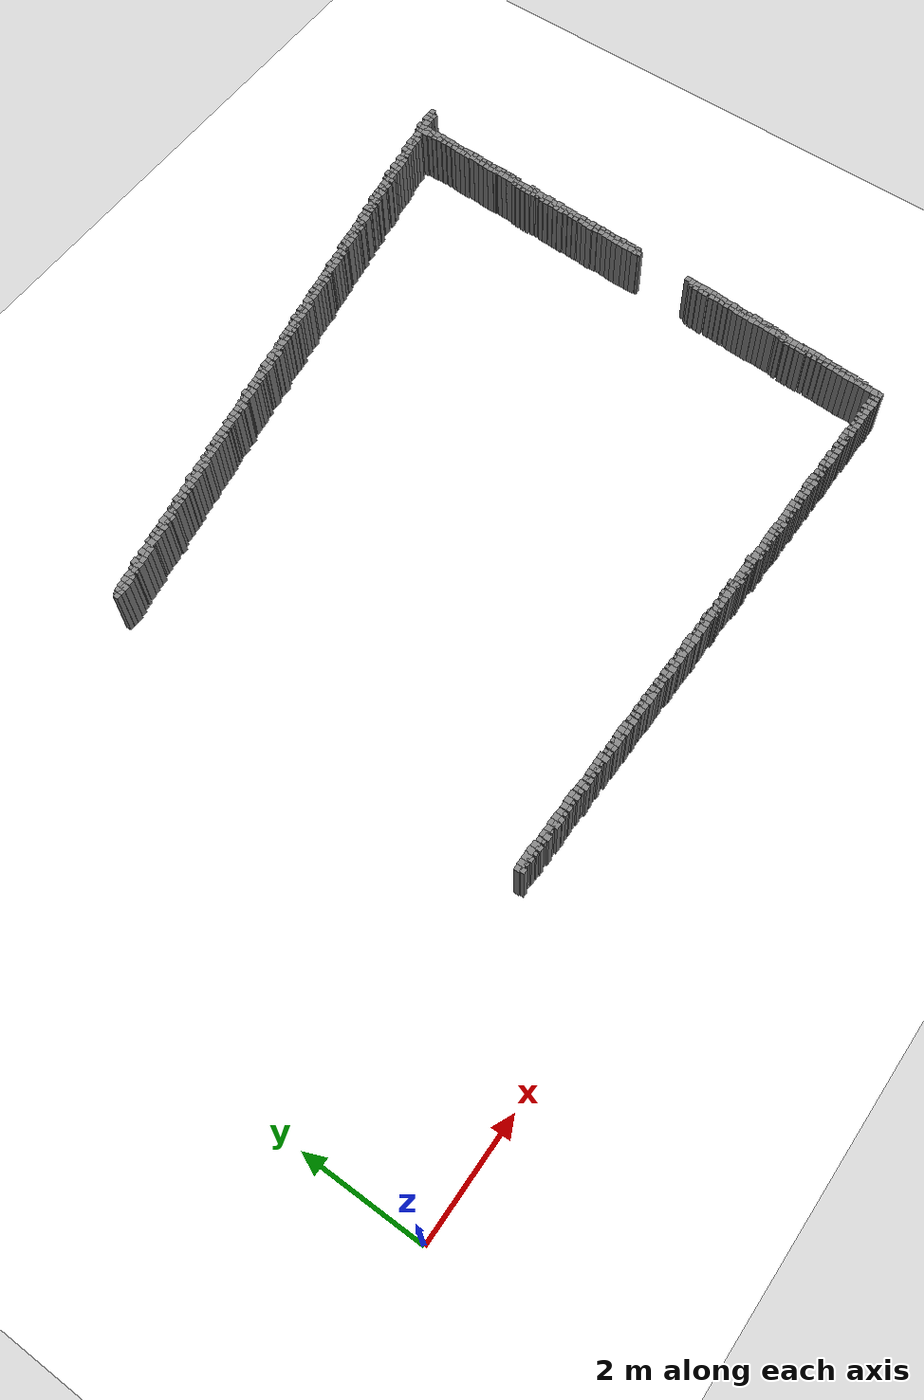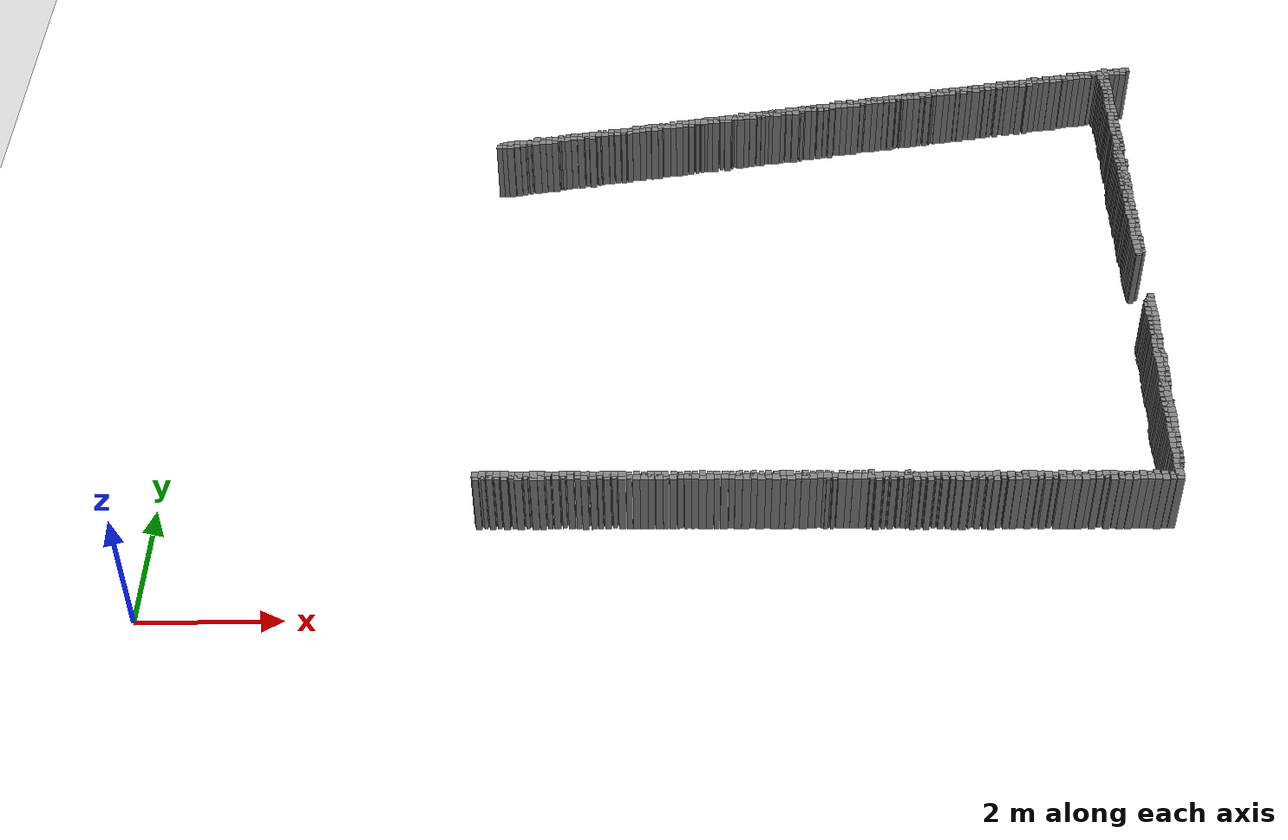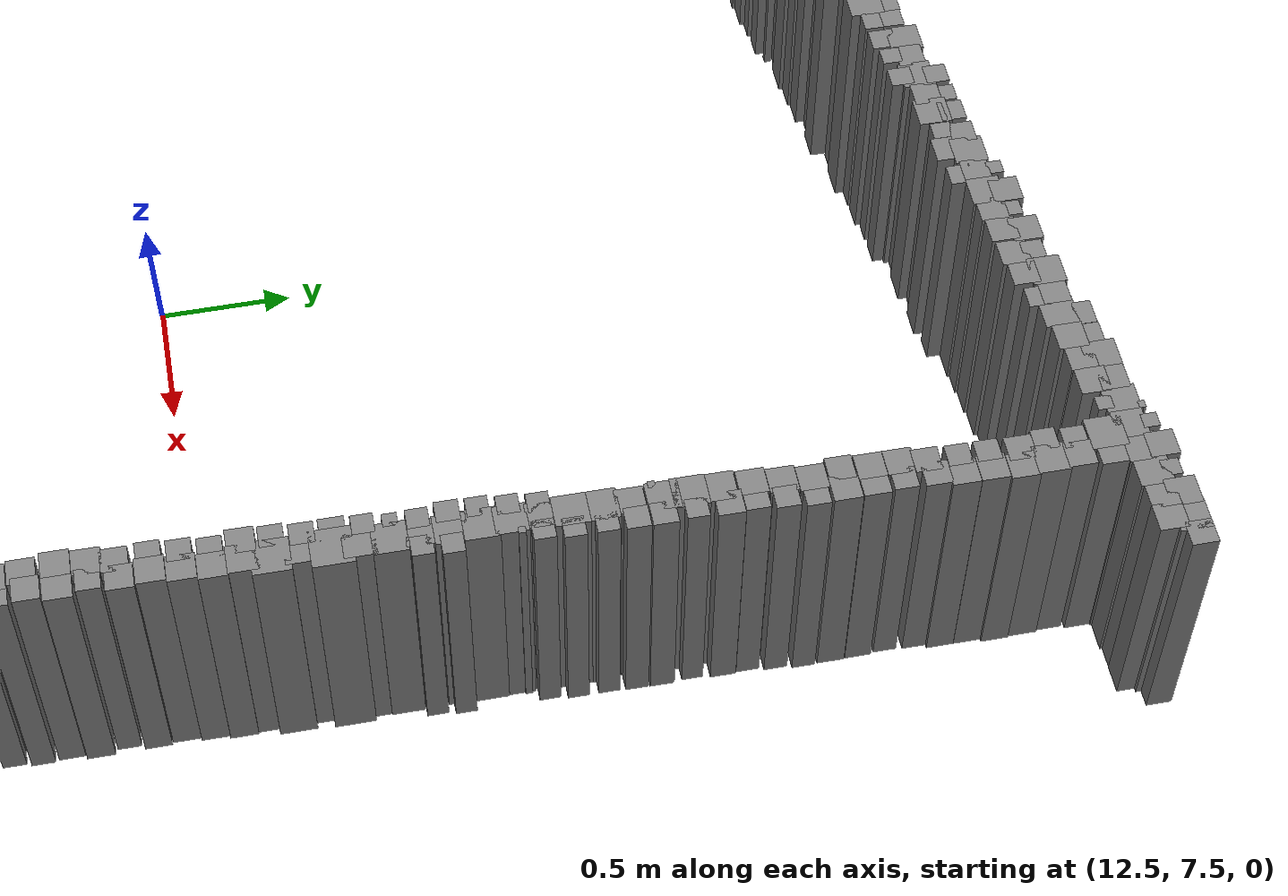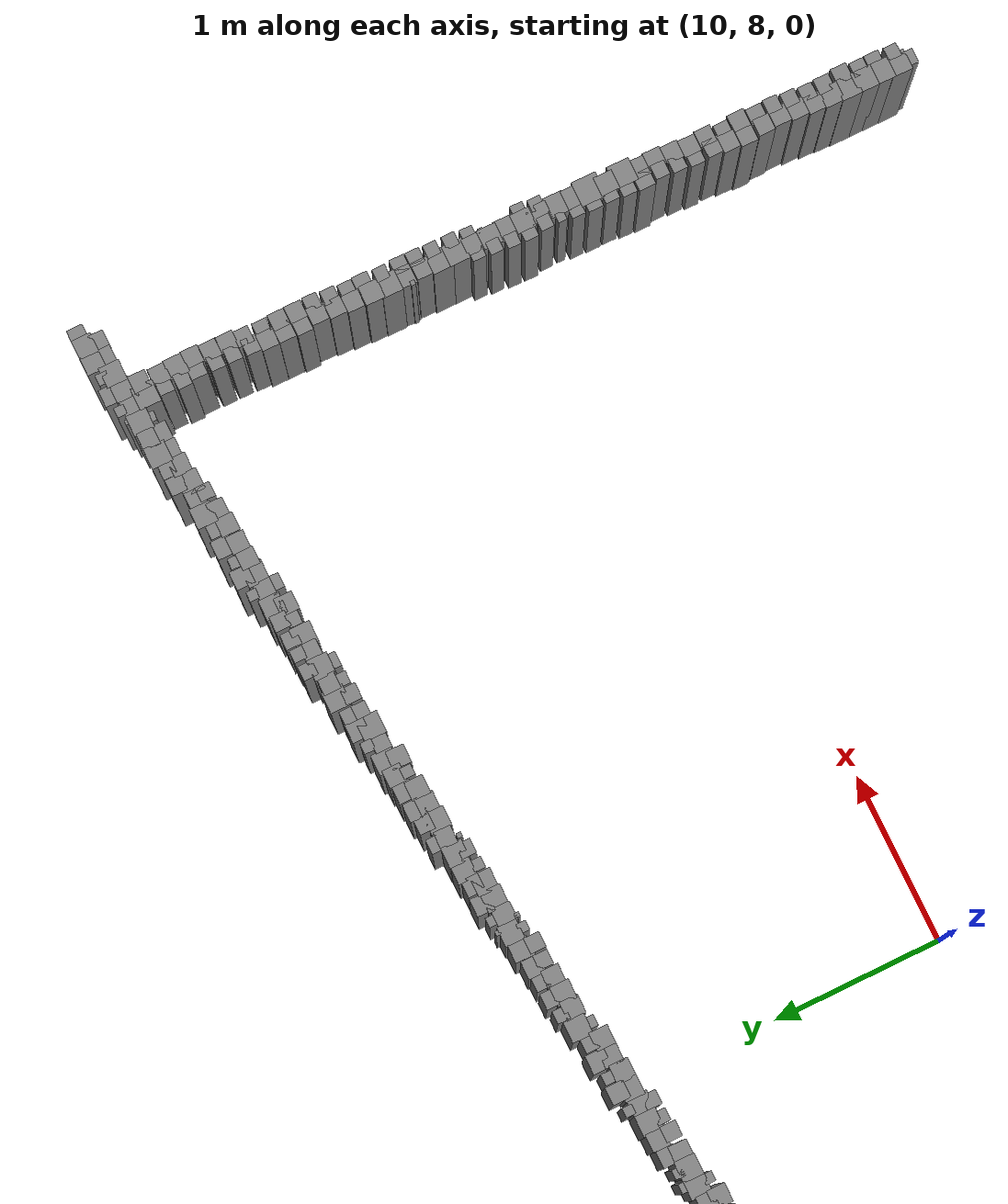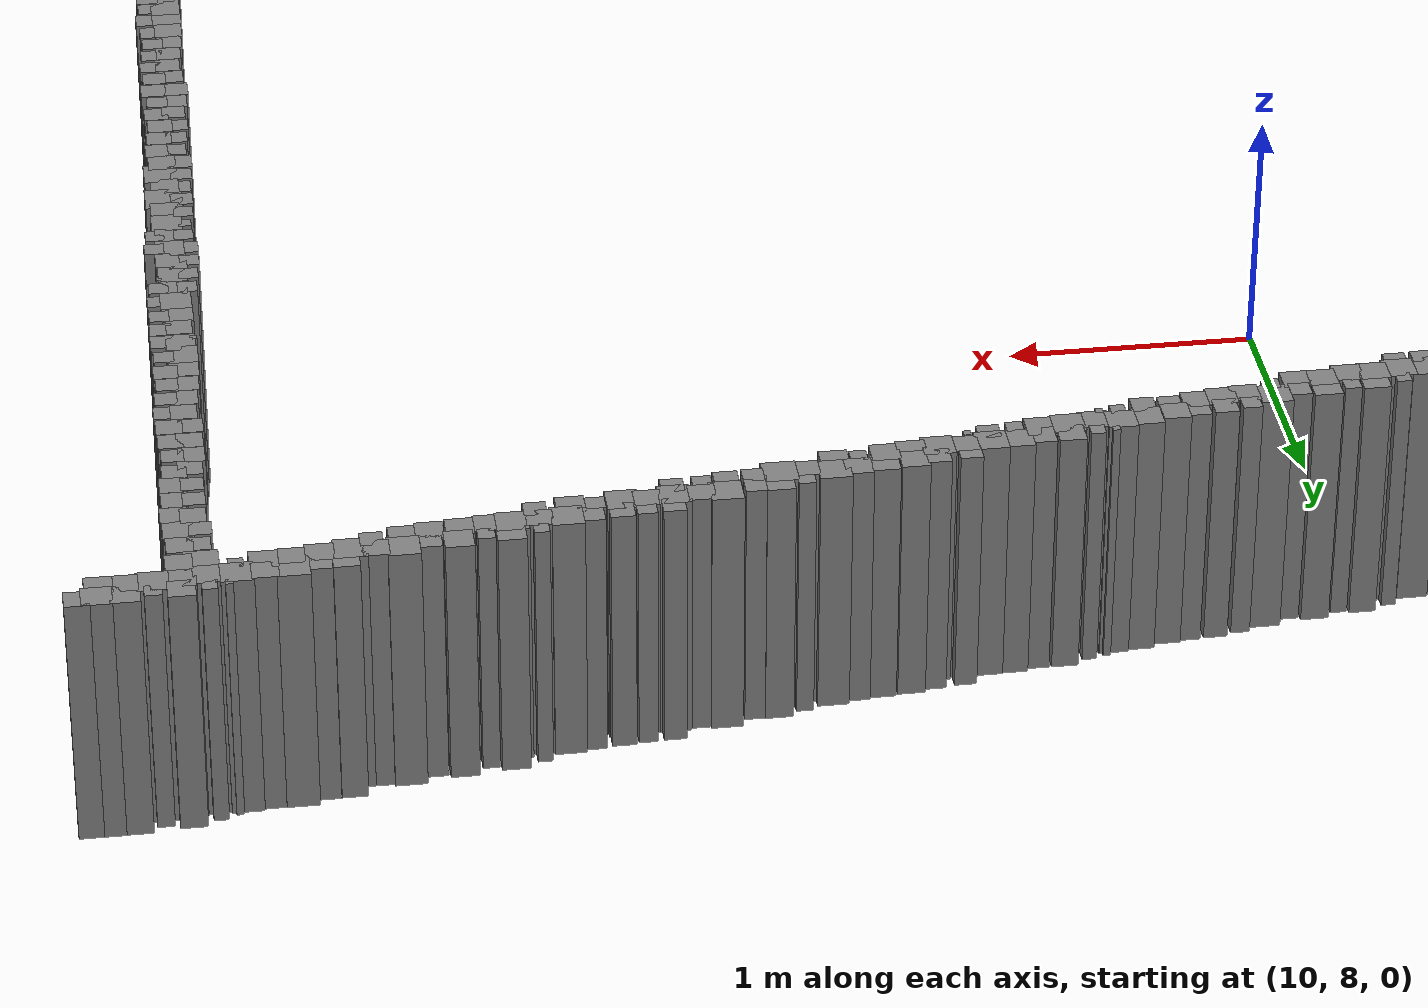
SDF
<?xml version="1.0" ?>
<sdf version="1.6">
  <world name="default">
    <model name="group_0">
      <pose>4.52 8.91 0.5 0 0 0</pose>
      <static>true</static>
      <link name="link">
        <collision name="collision">
          <geometry>
            <box>
              <size>0.08740686806820892 0.08740686806820892 1</size>
            </box>
          </geometry>
        </collision>
        <visual name="visual">
          <geometry>
            <box>
              <size>0.08740686806820892 0.08740686806820892 1</size>
            </box>
          </geometry>
          <material>
            <ambient>0.5 0.5 0.5 1</ambient>
          </material>
        </visual>
      </link>
    </model>
    <model name="group_1">
      <pose>4.54 8.97 0.5 0 0 0</pose>
      <static>true</static>
      <link name="link">
        <collision name="collision">
          <geometry>
            <box>
              <size>0.039435040914736375 0.039435040914736375 1</size>
            </box>
          </geometry>
        </collision>
        <visual name="visual">
          <geometry>
            <box>
              <size>0.039435040914736375 0.039435040914736375 1</size>
            </box>
          </geometry>
          <material>
            <ambient>0.5 0.5 0.5 1</ambient>
          </material>
        </visual>
      </link>
    </model>
    <model name="group_2">
      <pose>4.60 8.90 0.5 0 0 0</pose>
      <static>true</static>
      <link name="link">
        <collision name="collision">
          <geometry>
            <box>
              <size>0.07960863723841033 0.07960863723841033 1</size>
            </box>
          </geometry>
        </collision>
        <visual name="visual">
          <geometry>
            <box>
              <size>0.07960863723841033 0.07960863723841033 1</size>
            </box>
          </geometry>
          <material>
            <ambient>0.5 0.5 0.5 1</ambient>
          </material>
        </visual>
      </link>
    </model>
    <model name="group_3">
      <pose>4.61 8.97 0.5 0 0 0</pose>
      <static>true</static>
      <link name="link">
        <collision name="collision">
          <geometry>
            <box>
              <size>0.08105785199989857 0.08105785199989857 1</size>
            </box>
          </geometry>
        </collision>
        <visual name="visual">
          <geometry>
            <box>
              <size>0.08105785199989857 0.08105785199989857 1</size>
            </box>
          </geometry>
          <material>
            <ambient>0.5 0.5 0.5 1</ambient>
          </material>
        </visual>
      </link>
    </model>
    <model name="group_4">
      <pose>4.69 8.91 0.5 0 0 0</pose>
      <static>true</static>
      <link name="link">
        <collision name="collision">
          <geometry>
            <box>
              <size>0.1078212749080291 0.1078212749080291 1</size>
            </box>
          </geometry>
        </collision>
        <visual name="visual">
          <geometry>
            <box>
              <size>0.1078212749080291 0.1078212749080291 1</size>
            </box>
          </geometry>
          <material>
            <ambient>0.5 0.5 0.5 1</ambient>
          </material>
        </visual>
      </link>
    </model>
    <model name="group_5">
      <pose>4.70 8.98 0.5 0 0 0</pose>
      <static>true</static>
      <link name="link">
        <collision name="collision">
          <geometry>
            <box>
              <size>0.10297681291020339 0.10297681291020339 1</size>
            </box>
          </geometry>
        </collision>
        <visual name="visual">
          <geometry>
            <box>
              <size>0.10297681291020339 0.10297681291020339 1</size>
            </box>
          </geometry>
          <material>
            <ambient>0.5 0.5 0.5 1</ambient>
          </material>
        </visual>
      </link>
    </model>
    <model name="group_6">
      <pose>4.80 8.92 0.5 0 0 0</pose>
      <static>true</static>
      <link name="link">
        <collision name="collision">
          <geometry>
            <box>
              <size>0.0965730022409278 0.0965730022409278 1</size>
            </box>
          </geometry>
        </collision>
        <visual name="visual">
          <geometry>
            <box>
              <size>0.0965730022409278 0.0965730022409278 1</size>
            </box>
          </geometry>
          <material>
            <ambient>0.5 0.5 0.5 1</ambient>
          </material>
        </visual>
      </link>
    </model>
    <model name="group_7">
      <pose>4.80 9.00 0.5 0 0 0</pose>
      <static>true</static>
      <link name="link">
        <collision name="collision">
          <geometry>
            <box>
              <size>0.0991922640656726 0.0991922640656726 1</size>
            </box>
          </geometry>
        </collision>
        <visual name="visual">
          <geometry>
            <box>
              <size>0.0991922640656726 0.0991922640656726 1</size>
            </box>
          </geometry>
          <material>
            <ambient>0.5 0.5 0.5 1</ambient>
          </material>
        </visual>
      </link>
    </model>
    <model name="group_8">
      <pose>4.89 8.94 0.5 0 0 0</pose>
      <static>true</static>
      <link name="link">
        <collision name="collision">
          <geometry>
            <box>
              <size>0.08442075767464065 0.08442075767464065 1</size>
            </box>
          </geometry>
        </collision>
        <visual name="visual">
          <geometry>
            <box>
              <size>0.08442075767464065 0.08442075767464065 1</size>
            </box>
          </geometry>
          <material>
            <ambient>0.5 0.5 0.5 1</ambient>
          </material>
        </visual>
      </link>
    </model>
    <model name="group_9">
      <pose>4.90 9.00 0.5 0 0 0</pose>
      <static>true</static>
      <link name="link">
        <collision name="collision">
          <geometry>
            <box>
              <size>0.11941295585761501 0.11941295585761501 1</size>
            </box>
          </geometry>
        </collision>
        <visual name="visual">
          <geometry>
            <box>
              <size>0.11941295585761501 0.11941295585761501 1</size>
            </box>
          </geometry>
          <material>
            <ambient>0.5 0.5 0.5 1</ambient>
          </material>
        </visual>
      </link>
    </model>
    <model name="group_10">
      <pose>4.95 9.06 0.5 0 0 0</pose>
      <static>true</static>
      <link name="link">
        <collision name="collision">
          <geometry>
            <box>
              <size>0.0 0.0 1</size>
            </box>
          </geometry>
        </collision>
        <visual name="visual">
          <geometry>
            <box>
              <size>0.0 0.0 1</size>
            </box>
          </geometry>
          <material>
            <ambient>0.5 0.5 0.5 1</ambient>
          </material>
        </visual>
      </link>
    </model>
    <model name="group_11">
      <pose>4.99 8.94 0.5 0 0 0</pose>
      <static>true</static>
      <link name="link">
        <collision name="collision">
          <geometry>
            <box>
              <size>0.0562805051164271 0.0562805051164271 1</size>
            </box>
          </geometry>
        </collision>
        <visual name="visual">
          <geometry>
            <box>
              <size>0.0562805051164271 0.0562805051164271 1</size>
            </box>
          </geometry>
          <material>
            <ambient>0.5 0.5 0.5 1</ambient>
          </material>
        </visual>
      </link>
    </model>
    <model name="group_12">
      <pose>5.00 9.00 0.5 0 0 0</pose>
      <static>true</static>
      <link name="link">
        <collision name="collision">
          <geometry>
            <box>
              <size>0.09919226406566871 0.09919226406566871 1</size>
            </box>
          </geometry>
        </collision>
        <visual name="visual">
          <geometry>
            <box>
              <size>0.09919226406566871 0.09919226406566871 1</size>
            </box>
          </geometry>
          <material>
            <ambient>0.5 0.5 0.5 1</ambient>
          </material>
        </visual>
      </link>
    </model>
    <model name="group_13">
      <pose>5.00 9.06 0.5 0 0 0</pose>
      <static>true</static>
      <link name="link">
        <collision name="collision">
          <geometry>
            <box>
              <size>0.0562805051164271 0.0562805051164271 1</size>
            </box>
          </geometry>
        </collision>
        <visual name="visual">
          <geometry>
            <box>
              <size>0.0562805051164271 0.0562805051164271 1</size>
            </box>
          </geometry>
          <material>
            <ambient>0.5 0.5 0.5 1</ambient>
          </material>
        </visual>
      </link>
    </model>
    <model name="group_14">
      <pose>4.51 1.63 0.5 0 0 0</pose>
      <static>true</static>
      <link name="link">
        <collision name="collision">
          <geometry>
            <box>
              <size>0.08442075767464058 0.08442075767464058 1</size>
            </box>
          </geometry>
        </collision>
        <visual name="visual">
          <geometry>
            <box>
              <size>0.08442075767464058 0.08442075767464058 1</size>
            </box>
          </geometry>
          <material>
            <ambient>0.5 0.5 0.5 1</ambient>
          </material>
        </visual>
      </link>
    </model>
    <model name="group_15">
      <pose>4.50 1.70 0.5 0 0 0</pose>
      <static>true</static>
      <link name="link">
        <collision name="collision">
          <geometry>
            <box>
              <size>0.09919226406566767 0.09919226406566767 1</size>
            </box>
          </geometry>
        </collision>
        <visual name="visual">
          <geometry>
            <box>
              <size>0.09919226406566767 0.09919226406566767 1</size>
            </box>
          </geometry>
          <material>
            <ambient>0.5 0.5 0.5 1</ambient>
          </material>
        </visual>
      </link>
    </model>
    <model name="group_16">
      <pose>5.10 9.00 0.5 0 0 0</pose>
      <static>true</static>
      <link name="link">
        <collision name="collision">
          <geometry>
            <box>
              <size>0.11941295585761501 0.11941295585761501 1</size>
            </box>
          </geometry>
        </collision>
        <visual name="visual">
          <geometry>
            <box>
              <size>0.11941295585761501 0.11941295585761501 1</size>
            </box>
          </geometry>
          <material>
            <ambient>0.5 0.5 0.5 1</ambient>
          </material>
        </visual>
      </link>
    </model>
    <model name="group_17">
      <pose>5.11 9.08 0.5 0 0 0</pose>
      <static>true</static>
      <link name="link">
        <collision name="collision">
          <geometry>
            <box>
              <size>0.10632897044420285 0.10632897044420285 1</size>
            </box>
          </geometry>
        </collision>
        <visual name="visual">
          <geometry>
            <box>
              <size>0.10632897044420285 0.10632897044420285 1</size>
            </box>
          </geometry>
          <material>
            <ambient>0.5 0.5 0.5 1</ambient>
          </material>
        </visual>
      </link>
    </model>
    <model name="group_18">
      <pose>4.60 1.70 0.5 0 0 0</pose>
      <static>true</static>
      <link name="link">
        <collision name="collision">
          <geometry>
            <box>
              <size>0.11941295585761413 0.11941295585761413 1</size>
            </box>
          </geometry>
        </collision>
        <visual name="visual">
          <geometry>
            <box>
              <size>0.11941295585761413 0.11941295585761413 1</size>
            </box>
          </geometry>
          <material>
            <ambient>0.5 0.5 0.5 1</ambient>
          </material>
        </visual>
      </link>
    </model>
    <model name="group_19">
      <pose>4.61 1.64 0.5 0 0 0</pose>
      <static>true</static>
      <link name="link">
        <collision name="collision">
          <geometry>
            <box>
              <size>0.05628050511642709 0.05628050511642709 1</size>
            </box>
          </geometry>
        </collision>
        <visual name="visual">
          <geometry>
            <box>
              <size>0.05628050511642709 0.05628050511642709 1</size>
            </box>
          </geometry>
          <material>
            <ambient>0.5 0.5 0.5 1</ambient>
          </material>
        </visual>
      </link>
    </model>
    <model name="group_20">
      <pose>5.20 9.01 0.5 0 0 0</pose>
      <static>true</static>
      <link name="link">
        <collision name="collision">
          <geometry>
            <box>
              <size>0.10871288083971324 0.10871288083971324 1</size>
            </box>
          </geometry>
        </collision>
        <visual name="visual">
          <geometry>
            <box>
              <size>0.10871288083971324 0.10871288083971324 1</size>
            </box>
          </geometry>
          <material>
            <ambient>0.5 0.5 0.5 1</ambient>
          </material>
        </visual>
      </link>
    </model>
    <model name="group_21">
      <pose>5.20 9.08 0.5 0 0 0</pose>
      <static>true</static>
      <link name="link">
        <collision name="collision">
          <geometry>
            <box>
              <size>0.06413786030771819 0.06413786030771819 1</size>
            </box>
          </geometry>
        </collision>
        <visual name="visual">
          <geometry>
            <box>
              <size>0.06413786030771819 0.06413786030771819 1</size>
            </box>
          </geometry>
          <material>
            <ambient>0.5 0.5 0.5 1</ambient>
          </material>
        </visual>
      </link>
    </model>
    <model name="group_22">
      <pose>4.70 1.64 0.5 0 0 0</pose>
      <static>true</static>
      <link name="link">
        <collision name="collision">
          <geometry>
            <box>
              <size>0.08442075767464059 0.08442075767464059 1</size>
            </box>
          </geometry>
        </collision>
        <visual name="visual">
          <geometry>
            <box>
              <size>0.08442075767464059 0.08442075767464059 1</size>
            </box>
          </geometry>
          <material>
            <ambient>0.5 0.5 0.5 1</ambient>
          </material>
        </visual>
      </link>
    </model>
    <model name="group_23">
      <pose>4.70 1.70 0.5 0 0 0</pose>
      <static>true</static>
      <link name="link">
        <collision name="collision">
          <geometry>
            <box>
              <size>0.11884310777185463 0.11884310777185463 1</size>
            </box>
          </geometry>
        </collision>
        <visual name="visual">
          <geometry>
            <box>
              <size>0.11884310777185463 0.11884310777185463 1</size>
            </box>
          </geometry>
          <material>
            <ambient>0.5 0.5 0.5 1</ambient>
          </material>
        </visual>
      </link>
    </model>
    <model name="group_24">
      <pose>5.30 9.02 0.5 0 0 0</pose>
      <static>true</static>
      <link name="link">
        <collision name="collision">
          <geometry>
            <box>
              <size>0.0983825120287442 0.0983825120287442 1</size>
            </box>
          </geometry>
        </collision>
        <visual name="visual">
          <geometry>
            <box>
              <size>0.0983825120287442 0.0983825120287442 1</size>
            </box>
          </geometry>
          <material>
            <ambient>0.5 0.5 0.5 1</ambient>
          </material>
        </visual>
      </link>
    </model>
    <model name="group_25">
      <pose>5.30 9.10 0.5 0 0 0</pose>
      <static>true</static>
      <link name="link">
        <collision name="collision">
          <geometry>
            <box>
              <size>0.10297681291020155 0.10297681291020155 1</size>
            </box>
          </geometry>
        </collision>
        <visual name="visual">
          <geometry>
            <box>
              <size>0.10297681291020155 0.10297681291020155 1</size>
            </box>
          </geometry>
          <material>
            <ambient>0.5 0.5 0.5 1</ambient>
          </material>
        </visual>
      </link>
    </model>
    <model name="group_26">
      <pose>4.80 1.71 0.5 0 0 0</pose>
      <static>true</static>
      <link name="link">
        <collision name="collision">
          <geometry>
            <box>
              <size>0.11145209213377275 0.11145209213377275 1</size>
            </box>
          </geometry>
        </collision>
        <visual name="visual">
          <geometry>
            <box>
              <size>0.11145209213377275 0.11145209213377275 1</size>
            </box>
          </geometry>
          <material>
            <ambient>0.5 0.5 0.5 1</ambient>
          </material>
        </visual>
      </link>
    </model>
    <model name="group_27">
      <pose>4.80 1.63 0.5 0 0 0</pose>
      <static>true</static>
      <link name="link">
        <collision name="collision">
          <geometry>
            <box>
              <size>0.06413786030771763 0.06413786030771763 1</size>
            </box>
          </geometry>
        </collision>
        <visual name="visual">
          <geometry>
            <box>
              <size>0.06413786030771763 0.06413786030771763 1</size>
            </box>
          </geometry>
          <material>
            <ambient>0.5 0.5 0.5 1</ambient>
          </material>
        </visual>
      </link>
    </model>
    <model name="group_28">
      <pose>5.40 9.03 0.5 0 0 0</pose>
      <static>true</static>
      <link name="link">
        <collision name="collision">
          <geometry>
            <box>
              <size>0.10273569860668266 0.10273569860668266 1</size>
            </box>
          </geometry>
        </collision>
        <visual name="visual">
          <geometry>
            <box>
              <size>0.10273569860668266 0.10273569860668266 1</size>
            </box>
          </geometry>
          <material>
            <ambient>0.5 0.5 0.5 1</ambient>
          </material>
        </visual>
      </link>
    </model>
    <model name="group_29">
      <pose>5.40 9.10 0.5 0 0 0</pose>
      <static>true</static>
      <link name="link">
        <collision name="collision">
          <geometry>
            <box>
              <size>0.099244404533285 0.099244404533285 1</size>
            </box>
          </geometry>
        </collision>
        <visual name="visual">
          <geometry>
            <box>
              <size>0.099244404533285 0.099244404533285 1</size>
            </box>
          </geometry>
          <material>
            <ambient>0.5 0.5 0.5 1</ambient>
          </material>
        </visual>
      </link>
    </model>
    <model name="group_30">
      <pose>5.43 9.15 0.5 0 0 0</pose>
      <static>true</static>
      <link name="link">
        <collision name="collision">
          <geometry>
            <box>
              <size>0.0 0.0 1</size>
            </box>
          </geometry>
        </collision>
        <visual name="visual">
          <geometry>
            <box>
              <size>0.0 0.0 1</size>
            </box>
          </geometry>
          <material>
            <ambient>0.5 0.5 0.5 1</ambient>
          </material>
        </visual>
      </link>
    </model>
    <model name="group_31">
      <pose>4.90 1.63 0.5 0 0 0</pose>
      <static>true</static>
      <link name="link">
        <collision name="collision">
          <geometry>
            <box>
              <size>0.09070112511455176 0.09070112511455176 1</size>
            </box>
          </geometry>
        </collision>
        <visual name="visual">
          <geometry>
            <box>
              <size>0.09070112511455176 0.09070112511455176 1</size>
            </box>
          </geometry>
          <material>
            <ambient>0.5 0.5 0.5 1</ambient>
          </material>
        </visual>
      </link>
    </model>
    <model name="group_32">
      <pose>4.90 1.70 0.5 0 0 0</pose>
      <static>true</static>
      <link name="link">
        <collision name="collision">
          <geometry>
            <box>
              <size>0.11493900367022299 0.11493900367022299 1</size>
            </box>
          </geometry>
        </collision>
        <visual name="visual">
          <geometry>
            <box>
              <size>0.11493900367022299 0.11493900367022299 1</size>
            </box>
          </geometry>
          <material>
            <ambient>0.5 0.5 0.5 1</ambient>
          </material>
        </visual>
      </link>
    </model>
    <model name="group_33">
      <pose>5.50 9.09 0.5 0 0 0</pose>
      <static>true</static>
      <link name="link">
        <collision name="collision">
          <geometry>
            <box>
              <size>0.11941295585761268 0.11941295585761268 1</size>
            </box>
          </geometry>
        </collision>
        <visual name="visual">
          <geometry>
            <box>
              <size>0.11941295585761268 0.11941295585761268 1</size>
            </box>
          </geometry>
          <material>
            <ambient>0.5 0.5 0.5 1</ambient>
          </material>
        </visual>
      </link>
    </model>
    <model name="group_34">
      <pose>5.50 9.15 0.5 0 0 0</pose>
      <static>true</static>
      <link name="link">
        <collision name="collision">
          <geometry>
            <box>
              <size>0.08442075767464065 0.08442075767464065 1</size>
            </box>
          </geometry>
        </collision>
        <visual name="visual">
          <geometry>
            <box>
              <size>0.08442075767464065 0.08442075767464065 1</size>
            </box>
          </geometry>
          <material>
            <ambient>0.5 0.5 0.5 1</ambient>
          </material>
        </visual>
      </link>
    </model>
    <model name="group_35">
      <pose>5.49 9.03 0.5 0 0 0</pose>
      <static>true</static>
      <link name="link">
        <collision name="collision">
          <geometry>
            <box>
              <size>0.02814025255821355 0.02814025255821355 1</size>
            </box>
          </geometry>
        </collision>
        <visual name="visual">
          <geometry>
            <box>
              <size>0.02814025255821355 0.02814025255821355 1</size>
            </box>
          </geometry>
          <material>
            <ambient>0.5 0.5 0.5 1</ambient>
          </material>
        </visual>
      </link>
    </model>
    <model name="group_36">
      <pose>5.00 1.64 0.5 0 0 0</pose>
      <static>true</static>
      <link name="link">
        <collision name="collision">
          <geometry>
            <box>
              <size>0.06413786030771801 0.06413786030771801 1</size>
            </box>
          </geometry>
        </collision>
        <visual name="visual">
          <geometry>
            <box>
              <size>0.06413786030771801 0.06413786030771801 1</size>
            </box>
          </geometry>
          <material>
            <ambient>0.5 0.5 0.5 1</ambient>
          </material>
        </visual>
      </link>
    </model>
    <model name="group_37">
      <pose>5.00 1.70 0.5 0 0 0</pose>
      <static>true</static>
      <link name="link">
        <collision name="collision">
          <geometry>
            <box>
              <size>0.07960863723840993 0.07960863723840993 1</size>
            </box>
          </geometry>
        </collision>
        <visual name="visual">
          <geometry>
            <box>
              <size>0.07960863723840993 0.07960863723840993 1</size>
            </box>
          </geometry>
          <material>
            <ambient>0.5 0.5 0.5 1</ambient>
          </material>
        </visual>
      </link>
    </model>
    <model name="group_38">
      <pose>5.60 9.09 0.5 0 0 0</pose>
      <static>true</static>
      <link name="link">
        <collision name="collision">
          <geometry>
            <box>
              <size>0.11218382099302728 0.11218382099302728 1</size>
            </box>
          </geometry>
        </collision>
        <visual name="visual">
          <geometry>
            <box>
              <size>0.11218382099302728 0.11218382099302728 1</size>
            </box>
          </geometry>
          <material>
            <ambient>0.5 0.5 0.5 1</ambient>
          </material>
        </visual>
      </link>
    </model>
    <model name="group_39">
      <pose>5.61 9.17 0.5 0 0 0</pose>
      <static>true</static>
      <link name="link">
        <collision name="collision">
          <geometry>
            <box>
              <size>0.07256090009164153 0.07256090009164153 1</size>
            </box>
          </geometry>
        </collision>
        <visual name="visual">
          <geometry>
            <box>
              <size>0.07256090009164153 0.07256090009164153 1</size>
            </box>
          </geometry>
          <material>
            <ambient>0.5 0.5 0.5 1</ambient>
          </material>
        </visual>
      </link>
    </model>
    <model name="group_40">
      <pose>5.09 1.63 0.5 0 0 0</pose>
      <static>true</static>
      <link name="link">
        <collision name="collision">
          <geometry>
            <box>
              <size>0.10071559155087273 0.10071559155087273 1</size>
            </box>
          </geometry>
        </collision>
        <visual name="visual">
          <geometry>
            <box>
              <size>0.10071559155087273 0.10071559155087273 1</size>
            </box>
          </geometry>
          <material>
            <ambient>0.5 0.5 0.5 1</ambient>
          </material>
        </visual>
      </link>
    </model>
    <model name="group_41">
      <pose>5.10 1.69 0.5 0 0 0</pose>
      <static>true</static>
      <link name="link">
        <collision name="collision">
          <geometry>
            <box>
              <size>0.11145209213377198 0.11145209213377198 1</size>
            </box>
          </geometry>
        </collision>
        <visual name="visual">
          <geometry>
            <box>
              <size>0.11145209213377198 0.11145209213377198 1</size>
            </box>
          </geometry>
          <material>
            <ambient>0.5 0.5 0.5 1</ambient>
          </material>
        </visual>
      </link>
    </model>
    <model name="group_42">
      <pose>5.70 9.11 0.5 0 0 0</pose>
      <static>true</static>
      <link name="link">
        <collision name="collision">
          <geometry>
            <box>
              <size>0.10560575864695261 0.10560575864695261 1</size>
            </box>
          </geometry>
        </collision>
        <visual name="visual">
          <geometry>
            <box>
              <size>0.10560575864695261 0.10560575864695261 1</size>
            </box>
          </geometry>
          <material>
            <ambient>0.5 0.5 0.5 1</ambient>
          </material>
        </visual>
      </link>
    </model>
    <model name="group_43">
      <pose>5.70 9.17 0.5 0 0 0</pose>
      <static>true</static>
      <link name="link">
        <collision name="collision">
          <geometry>
            <box>
              <size>0.09070112511455292 0.09070112511455292 1</size>
            </box>
          </geometry>
        </collision>
        <visual name="visual">
          <geometry>
            <box>
              <size>0.09070112511455292 0.09070112511455292 1</size>
            </box>
          </geometry>
          <material>
            <ambient>0.5 0.5 0.5 1</ambient>
          </material>
        </visual>
      </link>
    </model>
    <model name="group_44">
      <pose>5.19 1.63 0.5 0 0 0</pose>
      <static>true</static>
      <link name="link">
        <collision name="collision">
          <geometry>
            <box>
              <size>0.05628050511642705 0.05628050511642705 1</size>
            </box>
          </geometry>
        </collision>
        <visual name="visual">
          <geometry>
            <box>
              <size>0.05628050511642705 0.05628050511642705 1</size>
            </box>
          </geometry>
          <material>
            <ambient>0.5 0.5 0.5 1</ambient>
          </material>
        </visual>
      </link>
    </model>
    <model name="group_45">
      <pose>5.20 1.69 0.5 0 0 0</pose>
      <static>true</static>
      <link name="link">
        <collision name="collision">
          <geometry>
            <box>
              <size>0.09919226406566733 0.09919226406566733 1</size>
            </box>
          </geometry>
        </collision>
        <visual name="visual">
          <geometry>
            <box>
              <size>0.09919226406566733 0.09919226406566733 1</size>
            </box>
          </geometry>
          <material>
            <ambient>0.5 0.5 0.5 1</ambient>
          </material>
        </visual>
      </link>
    </model>
    <model name="group_46">
      <pose>5.81 9.11 0.5 0 0 0</pose>
      <static>true</static>
      <link name="link">
        <collision name="collision">
          <geometry>
            <box>
              <size>0.10297681291020186 0.10297681291020186 1</size>
            </box>
          </geometry>
        </collision>
        <visual name="visual">
          <geometry>
            <box>
              <size>0.10297681291020186 0.10297681291020186 1</size>
            </box>
          </geometry>
          <material>
            <ambient>0.5 0.5 0.5 1</ambient>
          </material>
        </visual>
      </link>
    </model>
    <model name="group_47">
      <pose>5.80 9.19 0.5 0 0 0</pose>
      <static>true</static>
      <link name="link">
        <collision name="collision">
          <geometry>
            <box>
              <size>0.07960863723840801 0.07960863723840801 1</size>
            </box>
          </geometry>
        </collision>
        <visual name="visual">
          <geometry>
            <box>
              <size>0.07960863723840801 0.07960863723840801 1</size>
            </box>
          </geometry>
          <material>
            <ambient>0.5 0.5 0.5 1</ambient>
          </material>
        </visual>
      </link>
    </model>
    <model name="group_48">
      <pose>5.30 1.63 0.5 0 0 0</pose>
      <static>true</static>
      <link name="link">
        <collision name="collision">
          <geometry>
            <box>
              <size>0.10071559155087109 0.10071559155087109 1</size>
            </box>
          </geometry>
        </collision>
        <visual name="visual">
          <geometry>
            <box>
              <size>0.10071559155087109 0.10071559155087109 1</size>
            </box>
          </geometry>
          <material>
            <ambient>0.5 0.5 0.5 1</ambient>
          </material>
        </visual>
      </link>
    </model>
    <model name="group_49">
      <pose>5.30 1.69 0.5 0 0 0</pose>
      <static>true</static>
      <link name="link">
        <collision name="collision">
          <geometry>
            <box>
              <size>0.11941295585761355 0.11941295585761355 1</size>
            </box>
          </geometry>
        </collision>
        <visual name="visual">
          <geometry>
            <box>
              <size>0.11941295585761355 0.11941295585761355 1</size>
            </box>
          </geometry>
          <material>
            <ambient>0.5 0.5 0.5 1</ambient>
          </material>
        </visual>
      </link>
    </model>
    <model name="group_50">
      <pose>5.90 9.19 0.5 0 0 0</pose>
      <static>true</static>
      <link name="link">
        <collision name="collision">
          <geometry>
            <box>
              <size>0.12787992062458983 0.12787992062458983 1</size>
            </box>
          </geometry>
        </collision>
        <visual name="visual">
          <geometry>
            <box>
              <size>0.12787992062458983 0.12787992062458983 1</size>
            </box>
          </geometry>
          <material>
            <ambient>0.5 0.5 0.5 1</ambient>
          </material>
        </visual>
      </link>
    </model>
    <model name="group_51">
      <pose>5.91 9.13 0.5 0 0 0</pose>
      <static>true</static>
      <link name="link">
        <collision name="collision">
          <geometry>
            <box>
              <size>0.06413786030771819 0.06413786030771819 1</size>
            </box>
          </geometry>
        </collision>
        <visual name="visual">
          <geometry>
            <box>
              <size>0.06413786030771819 0.06413786030771819 1</size>
            </box>
          </geometry>
          <material>
            <ambient>0.5 0.5 0.5 1</ambient>
          </material>
        </visual>
      </link>
    </model>
    <model name="group_52">
      <pose>5.40 1.62 0.5 0 0 0</pose>
      <static>true</static>
      <link name="link">
        <collision name="collision">
          <geometry>
            <box>
              <size>0.0907011251145523 0.0907011251145523 1</size>
            </box>
          </geometry>
        </collision>
        <visual name="visual">
          <geometry>
            <box>
              <size>0.0907011251145523 0.0907011251145523 1</size>
            </box>
          </geometry>
          <material>
            <ambient>0.5 0.5 0.5 1</ambient>
          </material>
        </visual>
      </link>
    </model>
    <model name="group_53">
      <pose>5.40 1.70 0.5 0 0 0</pose>
      <static>true</static>
      <link name="link">
        <collision name="collision">
          <geometry>
            <box>
              <size>0.09919226406566879 0.09919226406566879 1</size>
            </box>
          </geometry>
        </collision>
        <visual name="visual">
          <geometry>
            <box>
              <size>0.09919226406566879 0.09919226406566879 1</size>
            </box>
          </geometry>
          <material>
            <ambient>0.5 0.5 0.5 1</ambient>
          </material>
        </visual>
      </link>
    </model>
    <model name="group_54">
      <pose>6.00 9.13 0.5 0 0 0</pose>
      <static>true</static>
      <link name="link">
        <collision name="collision">
          <geometry>
            <box>
              <size>0.10114093471775669 0.10114093471775669 1</size>
            </box>
          </geometry>
        </collision>
        <visual name="visual">
          <geometry>
            <box>
              <size>0.10114093471775669 0.10114093471775669 1</size>
            </box>
          </geometry>
          <material>
            <ambient>0.5 0.5 0.5 1</ambient>
          </material>
        </visual>
      </link>
    </model>
    <model name="group_55">
      <pose>6.00 9.20 0.5 0 0 0</pose>
      <static>true</static>
      <link name="link">
        <collision name="collision">
          <geometry>
            <box>
              <size>0.11884310777185265 0.11884310777185265 1</size>
            </box>
          </geometry>
        </collision>
        <visual name="visual">
          <geometry>
            <box>
              <size>0.11884310777185265 0.11884310777185265 1</size>
            </box>
          </geometry>
          <material>
            <ambient>0.5 0.5 0.5 1</ambient>
          </material>
        </visual>
      </link>
    </model>
    <model name="group_56">
      <pose>5.49 1.69 0.5 0 0 0</pose>
      <static>true</static>
      <link name="link">
        <collision name="collision">
          <geometry>
            <box>
              <size>0.1029768129102043 0.1029768129102043 1</size>
            </box>
          </geometry>
        </collision>
        <visual name="visual">
          <geometry>
            <box>
              <size>0.1029768129102043 0.1029768129102043 1</size>
            </box>
          </geometry>
          <material>
            <ambient>0.5 0.5 0.5 1</ambient>
          </material>
        </visual>
      </link>
    </model>
    <model name="group_57">
      <pose>6.10 9.21 0.5 0 0 0</pose>
      <static>true</static>
      <link name="link">
        <collision name="collision">
          <geometry>
            <box>
              <size>0.11145209213377275 0.11145209213377275 1</size>
            </box>
          </geometry>
        </collision>
        <visual name="visual">
          <geometry>
            <box>
              <size>0.11145209213377275 0.11145209213377275 1</size>
            </box>
          </geometry>
          <material>
            <ambient>0.5 0.5 0.5 1</ambient>
          </material>
        </visual>
      </link>
    </model>
    <model name="group_58">
      <pose>5.50 1.62 0.5 0 0 0</pose>
      <static>true</static>
      <link name="link">
        <collision name="collision">
          <geometry>
            <box>
              <size>0.06413786030771838 0.06413786030771838 1</size>
            </box>
          </geometry>
        </collision>
        <visual name="visual">
          <geometry>
            <box>
              <size>0.06413786030771838 0.06413786030771838 1</size>
            </box>
          </geometry>
          <material>
            <ambient>0.5 0.5 0.5 1</ambient>
          </material>
        </visual>
      </link>
    </model>
    <model name="group_59">
      <pose>6.10 9.15 0.5 0 0 0</pose>
      <static>true</static>
      <link name="link">
        <collision name="collision">
          <geometry>
            <box>
              <size>0.0562805051164271 0.0562805051164271 1</size>
            </box>
          </geometry>
        </collision>
        <visual name="visual">
          <geometry>
            <box>
              <size>0.0562805051164271 0.0562805051164271 1</size>
            </box>
          </geometry>
          <material>
            <ambient>0.5 0.5 0.5 1</ambient>
          </material>
        </visual>
      </link>
    </model>
    <model name="group_60">
      <pose>6.11 9.27 0.5 0 0 0</pose>
      <static>true</static>
      <link name="link">
        <collision name="collision">
          <geometry>
            <box>
              <size>0.056280505116427 0.056280505116427 1</size>
            </box>
          </geometry>
        </collision>
        <visual name="visual">
          <geometry>
            <box>
              <size>0.056280505116427 0.056280505116427 1</size>
            </box>
          </geometry>
          <material>
            <ambient>0.5 0.5 0.5 1</ambient>
          </material>
        </visual>
      </link>
    </model>
    <model name="group_61">
      <pose>5.60 1.63 0.5 0 0 0</pose>
      <static>true</static>
      <link name="link">
        <collision name="collision">
          <geometry>
            <box>
              <size>0.09070112511455203 0.09070112511455203 1</size>
            </box>
          </geometry>
        </collision>
        <visual name="visual">
          <geometry>
            <box>
              <size>0.09070112511455203 0.09070112511455203 1</size>
            </box>
          </geometry>
          <material>
            <ambient>0.5 0.5 0.5 1</ambient>
          </material>
        </visual>
      </link>
    </model>
    <model name="group_62">
      <pose>5.60 1.69 0.5 0 0 0</pose>
      <static>true</static>
      <link name="link">
        <collision name="collision">
          <geometry>
            <box>
              <size>0.09838251202874382 0.09838251202874382 1</size>
            </box>
          </geometry>
        </collision>
        <visual name="visual">
          <geometry>
            <box>
              <size>0.09838251202874382 0.09838251202874382 1</size>
            </box>
          </geometry>
          <material>
            <ambient>0.5 0.5 0.5 1</ambient>
          </material>
        </visual>
      </link>
    </model>
    <model name="group_63">
      <pose>6.16 9.15 0.5 0 0 0</pose>
      <static>true</static>
      <link name="link">
        <collision name="collision">
          <geometry>
            <box>
              <size>0.0 0.0 1</size>
            </box>
          </geometry>
        </collision>
        <visual name="visual">
          <geometry>
            <box>
              <size>0.0 0.0 1</size>
            </box>
          </geometry>
          <material>
            <ambient>0.5 0.5 0.5 1</ambient>
          </material>
        </visual>
      </link>
    </model>
    <model name="group_64">
      <pose>6.20 9.21 0.5 0 0 0</pose>
      <static>true</static>
      <link name="link">
        <collision name="collision">
          <geometry>
            <box>
              <size>0.1114520921337714 0.1114520921337714 1</size>
            </box>
          </geometry>
        </collision>
        <visual name="visual">
          <geometry>
            <box>
              <size>0.1114520921337714 0.1114520921337714 1</size>
            </box>
          </geometry>
          <material>
            <ambient>0.5 0.5 0.5 1</ambient>
          </material>
        </visual>
      </link>
    </model>
    <model name="group_65">
      <pose>6.20 9.27 0.5 0 0 0</pose>
      <static>true</static>
      <link name="link">
        <collision name="collision">
          <geometry>
            <box>
              <size>0.0562805051164271 0.0562805051164271 1</size>
            </box>
          </geometry>
        </collision>
        <visual name="visual">
          <geometry>
            <box>
              <size>0.0562805051164271 0.0562805051164271 1</size>
            </box>
          </geometry>
          <material>
            <ambient>0.5 0.5 0.5 1</ambient>
          </material>
        </visual>
      </link>
    </model>
    <model name="group_66">
      <pose>5.70 1.70 0.5 0 0 0</pose>
      <static>true</static>
      <link name="link">
        <collision name="collision">
          <geometry>
            <box>
              <size>0.10647461046978544 0.10647461046978544 1</size>
            </box>
          </geometry>
        </collision>
        <visual name="visual">
          <geometry>
            <box>
              <size>0.10647461046978544 0.10647461046978544 1</size>
            </box>
          </geometry>
          <material>
            <ambient>0.5 0.5 0.5 1</ambient>
          </material>
        </visual>
      </link>
    </model>
    <model name="group_67">
      <pose>6.30 9.28 0.5 0 0 0</pose>
      <static>true</static>
      <link name="link">
        <collision name="collision">
          <geometry>
            <box>
              <size>0.1029768129102052 0.1029768129102052 1</size>
            </box>
          </geometry>
        </collision>
        <visual name="visual">
          <geometry>
            <box>
              <size>0.1029768129102052 0.1029768129102052 1</size>
            </box>
          </geometry>
          <material>
            <ambient>0.5 0.5 0.5 1</ambient>
          </material>
        </visual>
      </link>
    </model>
    <model name="group_68">
      <pose>5.70 1.63 0.5 0 0 0</pose>
      <static>true</static>
      <link name="link">
        <collision name="collision">
          <geometry>
            <box>
              <size>0.06413786030771924 0.06413786030771924 1</size>
            </box>
          </geometry>
        </collision>
        <visual name="visual">
          <geometry>
            <box>
              <size>0.06413786030771924 0.06413786030771924 1</size>
            </box>
          </geometry>
          <material>
            <ambient>0.5 0.5 0.5 1</ambient>
          </material>
        </visual>
      </link>
    </model>
    <model name="group_69">
      <pose>6.30 9.20 0.5 0 0 0</pose>
      <static>true</static>
      <link name="link">
        <collision name="collision">
          <geometry>
            <box>
              <size>0.07960863723841265 0.07960863723841265 1</size>
            </box>
          </geometry>
        </collision>
        <visual name="visual">
          <geometry>
            <box>
              <size>0.07960863723841265 0.07960863723841265 1</size>
            </box>
          </geometry>
          <material>
            <ambient>0.5 0.5 0.5 1</ambient>
          </material>
        </visual>
      </link>
    </model>
    <model name="group_70">
      <pose>5.80 1.63 0.5 0 0 0</pose>
      <static>true</static>
      <link name="link">
        <collision name="collision">
          <geometry>
            <box>
              <size>0.0907011251145519 0.0907011251145519 1</size>
            </box>
          </geometry>
        </collision>
        <visual name="visual">
          <geometry>
            <box>
              <size>0.0907011251145519 0.0907011251145519 1</size>
            </box>
          </geometry>
          <material>
            <ambient>0.5 0.5 0.5 1</ambient>
          </material>
        </visual>
      </link>
    </model>
    <model name="group_71">
      <pose>5.80 1.70 0.5 0 0 0</pose>
      <static>true</static>
      <link name="link">
        <collision name="collision">
          <geometry>
            <box>
              <size>0.10297681291020339 0.10297681291020339 1</size>
            </box>
          </geometry>
        </collision>
        <visual name="visual">
          <geometry>
            <box>
              <size>0.10297681291020339 0.10297681291020339 1</size>
            </box>
          </geometry>
          <material>
            <ambient>0.5 0.5 0.5 1</ambient>
          </material>
        </visual>
      </link>
    </model>
    <model name="group_72">
      <pose>6.40 9.22 0.5 0 0 0</pose>
      <static>true</static>
      <link name="link">
        <collision name="collision">
          <geometry>
            <box>
              <size>0.0907011251145523 0.0907011251145523 1</size>
            </box>
          </geometry>
        </collision>
        <visual name="visual">
          <geometry>
            <box>
              <size>0.0907011251145523 0.0907011251145523 1</size>
            </box>
          </geometry>
          <material>
            <ambient>0.5 0.5 0.5 1</ambient>
          </material>
        </visual>
      </link>
    </model>
    <model name="group_73">
      <pose>6.40 9.28 0.5 0 0 0</pose>
      <static>true</static>
      <link name="link">
        <collision name="collision">
          <geometry>
            <box>
              <size>0.10882204233582819 0.10882204233582819 1</size>
            </box>
          </geometry>
        </collision>
        <visual name="visual">
          <geometry>
            <box>
              <size>0.10882204233582819 0.10882204233582819 1</size>
            </box>
          </geometry>
          <material>
            <ambient>0.5 0.5 0.5 1</ambient>
          </material>
        </visual>
      </link>
    </model>
    <model name="group_74">
      <pose>6.50 9.30 0.5 0 0 0</pose>
      <static>true</static>
      <link name="link">
        <collision name="collision">
          <geometry>
            <box>
              <size>0.11145209213377275 0.11145209213377275 1</size>
            </box>
          </geometry>
        </collision>
        <visual name="visual">
          <geometry>
            <box>
              <size>0.11145209213377275 0.11145209213377275 1</size>
            </box>
          </geometry>
          <material>
            <ambient>0.5 0.5 0.5 1</ambient>
          </material>
        </visual>
      </link>
    </model>
    <model name="group_75">
      <pose>5.90 1.63 0.5 0 0 0</pose>
      <static>true</static>
      <link name="link">
        <collision name="collision">
          <geometry>
            <box>
              <size>0.07321409456274738 0.07321409456274738 1</size>
            </box>
          </geometry>
        </collision>
        <visual name="visual">
          <geometry>
            <box>
              <size>0.07321409456274738 0.07321409456274738 1</size>
            </box>
          </geometry>
          <material>
            <ambient>0.5 0.5 0.5 1</ambient>
          </material>
        </visual>
      </link>
    </model>
    <model name="group_76">
      <pose>5.90 1.70 0.5 0 0 0</pose>
      <static>true</static>
      <link name="link">
        <collision name="collision">
          <geometry>
            <box>
              <size>0.07960863723840916 0.07960863723840916 1</size>
            </box>
          </geometry>
        </collision>
        <visual name="visual">
          <geometry>
            <box>
              <size>0.07960863723840916 0.07960863723840916 1</size>
            </box>
          </geometry>
          <material>
            <ambient>0.5 0.5 0.5 1</ambient>
          </material>
        </visual>
      </link>
    </model>
    <model name="group_77">
      <pose>6.50 9.22 0.5 0 0 0</pose>
      <static>true</static>
      <link name="link">
        <collision name="collision">
          <geometry>
            <box>
              <size>0.07256090009164153 0.07256090009164153 1</size>
            </box>
          </geometry>
        </collision>
        <visual name="visual">
          <geometry>
            <box>
              <size>0.07256090009164153 0.07256090009164153 1</size>
            </box>
          </geometry>
          <material>
            <ambient>0.5 0.5 0.5 1</ambient>
          </material>
        </visual>
      </link>
    </model>
    <model name="group_78">
      <pose>5.99 1.61 0.5 0 0 0</pose>
      <static>true</static>
      <link name="link">
        <collision name="collision">
          <geometry>
            <box>
              <size>0.09070112511455243 0.09070112511455243 1</size>
            </box>
          </geometry>
        </collision>
        <visual name="visual">
          <geometry>
            <box>
              <size>0.09070112511455243 0.09070112511455243 1</size>
            </box>
          </geometry>
          <material>
            <ambient>0.5 0.5 0.5 1</ambient>
          </material>
        </visual>
      </link>
    </model>
    <model name="group_79">
      <pose>6.00 1.68 0.5 0 0 0</pose>
      <static>true</static>
      <link name="link">
        <collision name="collision">
          <geometry>
            <box>
              <size>0.10915025861500259 0.10915025861500259 1</size>
            </box>
          </geometry>
        </collision>
        <visual name="visual">
          <geometry>
            <box>
              <size>0.10915025861500259 0.10915025861500259 1</size>
            </box>
          </geometry>
          <material>
            <ambient>0.5 0.5 0.5 1</ambient>
          </material>
        </visual>
      </link>
    </model>
    <model name="group_80">
      <pose>6.60 9.24 0.5 0 0 0</pose>
      <static>true</static>
      <link name="link">
        <collision name="collision">
          <geometry>
            <box>
              <size>0.08442075767464222 0.08442075767464222 1</size>
            </box>
          </geometry>
        </collision>
        <visual name="visual">
          <geometry>
            <box>
              <size>0.08442075767464222 0.08442075767464222 1</size>
            </box>
          </geometry>
          <material>
            <ambient>0.5 0.5 0.5 1</ambient>
          </material>
        </visual>
      </link>
    </model>
    <model name="group_81">
      <pose>6.60 9.30 0.5 0 0 0</pose>
      <static>true</static>
      <link name="link">
        <collision name="collision">
          <geometry>
            <box>
              <size>0.1114520921337714 0.1114520921337714 1</size>
            </box>
          </geometry>
        </collision>
        <visual name="visual">
          <geometry>
            <box>
              <size>0.1114520921337714 0.1114520921337714 1</size>
            </box>
          </geometry>
          <material>
            <ambient>0.5 0.5 0.5 1</ambient>
          </material>
        </visual>
      </link>
    </model>
    <model name="group_82">
      <pose>6.61 9.36 0.5 0 0 0</pose>
      <static>true</static>
      <link name="link">
        <collision name="collision">
          <geometry>
            <box>
              <size>0.02814025255821355 0.02814025255821355 1</size>
            </box>
          </geometry>
        </collision>
        <visual name="visual">
          <geometry>
            <box>
              <size>0.02814025255821355 0.02814025255821355 1</size>
            </box>
          </geometry>
          <material>
            <ambient>0.5 0.5 0.5 1</ambient>
          </material>
        </visual>
      </link>
    </model>
    <model name="group_83">
      <pose>6.70 9.30 0.5 0 0 0</pose>
      <static>true</static>
      <link name="link">
        <collision name="collision">
          <geometry>
            <box>
              <size>0.11884310777185612 0.11884310777185612 1</size>
            </box>
          </geometry>
        </collision>
        <visual name="visual">
          <geometry>
            <box>
              <size>0.11884310777185612 0.11884310777185612 1</size>
            </box>
          </geometry>
          <material>
            <ambient>0.5 0.5 0.5 1</ambient>
          </material>
        </visual>
      </link>
    </model>
    <model name="group_84">
      <pose>6.70 9.37 0.5 0 0 0</pose>
      <static>true</static>
      <link name="link">
        <collision name="collision">
          <geometry>
            <box>
              <size>0.10288911944020827 0.10288911944020827 1</size>
            </box>
          </geometry>
        </collision>
        <visual name="visual">
          <geometry>
            <box>
              <size>0.10288911944020827 0.10288911944020827 1</size>
            </box>
          </geometry>
          <material>
            <ambient>0.5 0.5 0.5 1</ambient>
          </material>
        </visual>
      </link>
    </model>
    <model name="group_85">
      <pose>6.11 1.62 0.5 0 0 0</pose>
      <static>true</static>
      <link name="link">
        <collision name="collision">
          <geometry>
            <box>
              <size>0.09070112511455217 0.09070112511455217 1</size>
            </box>
          </geometry>
        </collision>
        <visual name="visual">
          <geometry>
            <box>
              <size>0.09070112511455217 0.09070112511455217 1</size>
            </box>
          </geometry>
          <material>
            <ambient>0.5 0.5 0.5 1</ambient>
          </material>
        </visual>
      </link>
    </model>
    <model name="group_86">
      <pose>6.10 1.68 0.5 0 0 0</pose>
      <static>true</static>
      <link name="link">
        <collision name="collision">
          <geometry>
            <box>
              <size>0.07960863723840993 0.07960863723840993 1</size>
            </box>
          </geometry>
        </collision>
        <visual name="visual">
          <geometry>
            <box>
              <size>0.07960863723840993 0.07960863723840993 1</size>
            </box>
          </geometry>
          <material>
            <ambient>0.5 0.5 0.5 1</ambient>
          </material>
        </visual>
      </link>
    </model>
    <model name="group_87">
      <pose>6.67 9.24 0.5 0 0 0</pose>
      <static>true</static>
      <link name="link">
        <collision name="collision">
          <geometry>
            <box>
              <size>0.0 0.0 1</size>
            </box>
          </geometry>
        </collision>
        <visual name="visual">
          <geometry>
            <box>
              <size>0.0 0.0 1</size>
            </box>
          </geometry>
          <material>
            <ambient>0.5 0.5 0.5 1</ambient>
          </material>
        </visual>
      </link>
    </model>
    <model name="group_88">
      <pose>6.20 1.68 0.5 0 0 0</pose>
      <static>true</static>
      <link name="link">
        <collision name="collision">
          <geometry>
            <box>
              <size>0.10297681291020278 0.10297681291020278 1</size>
            </box>
          </geometry>
        </collision>
        <visual name="visual">
          <geometry>
            <box>
              <size>0.10297681291020278 0.10297681291020278 1</size>
            </box>
          </geometry>
          <material>
            <ambient>0.5 0.5 0.5 1</ambient>
          </material>
        </visual>
      </link>
    </model>
    <model name="group_89">
      <pose>6.80 9.31 0.5 0 0 0</pose>
      <static>true</static>
      <link name="link">
        <collision name="collision">
          <geometry>
            <box>
              <size>0.12039171518391106 0.12039171518391106 1</size>
            </box>
          </geometry>
        </collision>
        <visual name="visual">
          <geometry>
            <box>
              <size>0.12039171518391106 0.12039171518391106 1</size>
            </box>
          </geometry>
          <material>
            <ambient>0.5 0.5 0.5 1</ambient>
          </material>
        </visual>
      </link>
    </model>
    <model name="group_90">
      <pose>6.80 9.38 0.5 0 0 0</pose>
      <static>true</static>
      <link name="link">
        <collision name="collision">
          <geometry>
            <box>
              <size>0.06413786030771819 0.06413786030771819 1</size>
            </box>
          </geometry>
        </collision>
        <visual name="visual">
          <geometry>
            <box>
              <size>0.06413786030771819 0.06413786030771819 1</size>
            </box>
          </geometry>
          <material>
            <ambient>0.5 0.5 0.5 1</ambient>
          </material>
        </visual>
      </link>
    </model>
    <model name="group_91">
      <pose>6.20 1.62 0.5 0 0 0</pose>
      <static>true</static>
      <link name="link">
        <collision name="collision">
          <geometry>
            <box>
              <size>0.06413786030771819 0.06413786030771819 1</size>
            </box>
          </geometry>
        </collision>
        <visual name="visual">
          <geometry>
            <box>
              <size>0.06413786030771819 0.06413786030771819 1</size>
            </box>
          </geometry>
          <material>
            <ambient>0.5 0.5 0.5 1</ambient>
          </material>
        </visual>
      </link>
    </model>
    <model name="group_92">
      <pose>6.90 9.39 0.5 0 0 0</pose>
      <static>true</static>
      <link name="link">
        <collision name="collision">
          <geometry>
            <box>
              <size>0.10782127490802769 0.10782127490802769 1</size>
            </box>
          </geometry>
        </collision>
        <visual name="visual">
          <geometry>
            <box>
              <size>0.10782127490802769 0.10782127490802769 1</size>
            </box>
          </geometry>
          <material>
            <ambient>0.5 0.5 0.5 1</ambient>
          </material>
        </visual>
      </link>
    </model>
    <model name="group_93">
      <pose>6.30 1.62 0.5 0 0 0</pose>
      <static>true</static>
      <link name="link">
        <collision name="collision">
          <geometry>
            <box>
              <size>0.0907011251145523 0.0907011251145523 1</size>
            </box>
          </geometry>
        </collision>
        <visual name="visual">
          <geometry>
            <box>
              <size>0.0907011251145523 0.0907011251145523 1</size>
            </box>
          </geometry>
          <material>
            <ambient>0.5 0.5 0.5 1</ambient>
          </material>
        </visual>
      </link>
    </model>
    <model name="group_94">
      <pose>6.30 1.68 0.5 0 0 0</pose>
      <static>true</static>
      <link name="link">
        <collision name="collision">
          <geometry>
            <box>
              <size>0.10647461046978292 0.10647461046978292 1</size>
            </box>
          </geometry>
        </collision>
        <visual name="visual">
          <geometry>
            <box>
              <size>0.10647461046978292 0.10647461046978292 1</size>
            </box>
          </geometry>
          <material>
            <ambient>0.5 0.5 0.5 1</ambient>
          </material>
        </visual>
      </link>
    </model>
    <model name="group_95">
      <pose>6.90 9.32 0.5 0 0 0</pose>
      <static>true</static>
      <link name="link">
        <collision name="collision">
          <geometry>
            <box>
              <size>0.07960863723841166 0.07960863723841166 1</size>
            </box>
          </geometry>
        </collision>
        <visual name="visual">
          <geometry>
            <box>
              <size>0.07960863723841166 0.07960863723841166 1</size>
            </box>
          </geometry>
          <material>
            <ambient>0.5 0.5 0.5 1</ambient>
          </material>
        </visual>
      </link>
    </model>
    <model name="group_96">
      <pose>6.40 1.69 0.5 0 0 0</pose>
      <static>true</static>
      <link name="link">
        <collision name="collision">
          <geometry>
            <box>
              <size>0.0983825120287432 0.0983825120287432 1</size>
            </box>
          </geometry>
        </collision>
        <visual name="visual">
          <geometry>
            <box>
              <size>0.0983825120287432 0.0983825120287432 1</size>
            </box>
          </geometry>
          <material>
            <ambient>0.5 0.5 0.5 1</ambient>
          </material>
        </visual>
      </link>
    </model>
    <model name="group_97">
      <pose>7.00 9.33 0.5 0 0 0</pose>
      <static>true</static>
      <link name="link">
        <collision name="collision">
          <geometry>
            <box>
              <size>0.10782127490802607 0.10782127490802607 1</size>
            </box>
          </geometry>
        </collision>
        <visual name="visual">
          <geometry>
            <box>
              <size>0.10782127490802607 0.10782127490802607 1</size>
            </box>
          </geometry>
          <material>
            <ambient>0.5 0.5 0.5 1</ambient>
          </material>
        </visual>
      </link>
    </model>
    <model name="group_98">
      <pose>7.00 9.40 0.5 0 0 0</pose>
      <static>true</static>
      <link name="link">
        <collision name="collision">
          <geometry>
            <box>
              <size>0.0983825120287442 0.0983825120287442 1</size>
            </box>
          </geometry>
        </collision>
        <visual name="visual">
          <geometry>
            <box>
              <size>0.0983825120287442 0.0983825120287442 1</size>
            </box>
          </geometry>
          <material>
            <ambient>0.5 0.5 0.5 1</ambient>
          </material>
        </visual>
      </link>
    </model>
    <model name="group_99">
      <pose>6.40 1.63 0.5 0 0 0</pose>
      <static>true</static>
      <link name="link">
        <collision name="collision">
          <geometry>
            <box>
              <size>0.06413786030771981 0.06413786030771981 1</size>
            </box>
          </geometry>
        </collision>
        <visual name="visual">
          <geometry>
            <box>
              <size>0.06413786030771981 0.06413786030771981 1</size>
            </box>
          </geometry>
          <material>
            <ambient>0.5 0.5 0.5 1</ambient>
          </material>
        </visual>
      </link>
    </model>
    <model name="group_100">
      <pose>7.10 9.39 0.5 0 0 0</pose>
      <static>true</static>
      <link name="link">
        <collision name="collision">
          <geometry>
            <box>
              <size>0.11898060602917175 0.11898060602917175 1</size>
            </box>
          </geometry>
        </collision>
        <visual name="visual">
          <geometry>
            <box>
              <size>0.11898060602917175 0.11898060602917175 1</size>
            </box>
          </geometry>
          <material>
            <ambient>0.5 0.5 0.5 1</ambient>
          </material>
        </visual>
      </link>
    </model>
    <model name="group_101">
      <pose>6.50 1.62 0.5 0 0 0</pose>
      <static>true</static>
      <link name="link">
        <collision name="collision">
          <geometry>
            <box>
              <size>0.10297681291020339 0.10297681291020339 1</size>
            </box>
          </geometry>
        </collision>
        <visual name="visual">
          <geometry>
            <box>
              <size>0.10297681291020339 0.10297681291020339 1</size>
            </box>
          </geometry>
          <material>
            <ambient>0.5 0.5 0.5 1</ambient>
          </material>
        </visual>
      </link>
    </model>
    <model name="group_102">
      <pose>6.50 1.69 0.5 0 0 0</pose>
      <static>true</static>
      <link name="link">
        <collision name="collision">
          <geometry>
            <box>
              <size>0.10297681291020491 0.10297681291020491 1</size>
            </box>
          </geometry>
        </collision>
        <visual name="visual">
          <geometry>
            <box>
              <size>0.10297681291020491 0.10297681291020491 1</size>
            </box>
          </geometry>
          <material>
            <ambient>0.5 0.5 0.5 1</ambient>
          </material>
        </visual>
      </link>
    </model>
    <model name="group_103">
      <pose>7.09 9.33 0.5 0 0 0</pose>
      <static>true</static>
      <link name="link">
        <collision name="collision">
          <geometry>
            <box>
              <size>0.07012024655144619 0.07012024655144619 1</size>
            </box>
          </geometry>
        </collision>
        <visual name="visual">
          <geometry>
            <box>
              <size>0.07012024655144619 0.07012024655144619 1</size>
            </box>
          </geometry>
          <material>
            <ambient>0.5 0.5 0.5 1</ambient>
          </material>
        </visual>
      </link>
    </model>
    <model name="group_104">
      <pose>7.11 9.45 0.5 0 0 0</pose>
      <static>true</static>
      <link name="link">
        <collision name="collision">
          <geometry>
            <box>
              <size>0.0562805051164271 0.0562805051164271 1</size>
            </box>
          </geometry>
        </collision>
        <visual name="visual">
          <geometry>
            <box>
              <size>0.0562805051164271 0.0562805051164271 1</size>
            </box>
          </geometry>
          <material>
            <ambient>0.5 0.5 0.5 1</ambient>
          </material>
        </visual>
      </link>
    </model>
    <model name="group_105">
      <pose>7.16 9.33 0.5 0 0 0</pose>
      <static>true</static>
      <link name="link">
        <collision name="collision">
          <geometry>
            <box>
              <size>0.0 0.0 1</size>
            </box>
          </geometry>
        </collision>
        <visual name="visual">
          <geometry>
            <box>
              <size>0.0 0.0 1</size>
            </box>
          </geometry>
          <material>
            <ambient>0.5 0.5 0.5 1</ambient>
          </material>
        </visual>
      </link>
    </model>
    <model name="group_106">
      <pose>7.20 9.39 0.5 0 0 0</pose>
      <static>true</static>
      <link name="link">
        <collision name="collision">
          <geometry>
            <box>
              <size>0.11941295585761501 0.11941295585761501 1</size>
            </box>
          </geometry>
        </collision>
        <visual name="visual">
          <geometry>
            <box>
              <size>0.11941295585761501 0.11941295585761501 1</size>
            </box>
          </geometry>
          <material>
            <ambient>0.5 0.5 0.5 1</ambient>
          </material>
        </visual>
      </link>
    </model>
    <model name="group_107">
      <pose>7.19 9.45 0.5 0 0 0</pose>
      <static>true</static>
      <link name="link">
        <collision name="collision">
          <geometry>
            <box>
              <size>0.0562805051164271 0.0562805051164271 1</size>
            </box>
          </geometry>
        </collision>
        <visual name="visual">
          <geometry>
            <box>
              <size>0.0562805051164271 0.0562805051164271 1</size>
            </box>
          </geometry>
          <material>
            <ambient>0.5 0.5 0.5 1</ambient>
          </material>
        </visual>
      </link>
    </model>
    <model name="group_108">
      <pose>6.60 1.62 0.5 0 0 0</pose>
      <static>true</static>
      <link name="link">
        <collision name="collision">
          <geometry>
            <box>
              <size>0.07960863723840887 0.07960863723840887 1</size>
            </box>
          </geometry>
        </collision>
        <visual name="visual">
          <geometry>
            <box>
              <size>0.07960863723840887 0.07960863723840887 1</size>
            </box>
          </geometry>
          <material>
            <ambient>0.5 0.5 0.5 1</ambient>
          </material>
        </visual>
      </link>
    </model>
    <model name="group_109">
      <pose>6.60 1.68 0.5 0 0 0</pose>
      <static>true</static>
      <link name="link">
        <collision name="collision">
          <geometry>
            <box>
              <size>0.06413786030771801 0.06413786030771801 1</size>
            </box>
          </geometry>
        </collision>
        <visual name="visual">
          <geometry>
            <box>
              <size>0.06413786030771801 0.06413786030771801 1</size>
            </box>
          </geometry>
          <material>
            <ambient>0.5 0.5 0.5 1</ambient>
          </material>
        </visual>
      </link>
    </model>
    <model name="group_110">
      <pose>7.29 9.47 0.5 0 0 0</pose>
      <static>true</static>
      <link name="link">
        <collision name="collision">
          <geometry>
            <box>
              <size>0.09070112511455337 0.09070112511455337 1</size>
            </box>
          </geometry>
        </collision>
        <visual name="visual">
          <geometry>
            <box>
              <size>0.09070112511455337 0.09070112511455337 1</size>
            </box>
          </geometry>
          <material>
            <ambient>0.5 0.5 0.5 1</ambient>
          </material>
        </visual>
      </link>
    </model>
    <model name="group_111">
      <pose>6.70 1.62 0.5 0 0 0</pose>
      <static>true</static>
      <link name="link">
        <collision name="collision">
          <geometry>
            <box>
              <size>0.10297681291020491 0.10297681291020491 1</size>
            </box>
          </geometry>
        </collision>
        <visual name="visual">
          <geometry>
            <box>
              <size>0.10297681291020491 0.10297681291020491 1</size>
            </box>
          </geometry>
          <material>
            <ambient>0.5 0.5 0.5 1</ambient>
          </material>
        </visual>
      </link>
    </model>
    <model name="group_112">
      <pose>6.70 1.68 0.5 0 0 0</pose>
      <static>true</static>
      <link name="link">
        <collision name="collision">
          <geometry>
            <box>
              <size>0.09070112511455217 0.09070112511455217 1</size>
            </box>
          </geometry>
        </collision>
        <visual name="visual">
          <geometry>
            <box>
              <size>0.09070112511455217 0.09070112511455217 1</size>
            </box>
          </geometry>
          <material>
            <ambient>0.5 0.5 0.5 1</ambient>
          </material>
        </visual>
      </link>
    </model>
    <model name="group_113">
      <pose>7.30 9.39 0.5 0 0 0</pose>
      <static>true</static>
      <link name="link">
        <collision name="collision">
          <geometry>
            <box>
              <size>0.09919226406566706 0.09919226406566706 1</size>
            </box>
          </geometry>
        </collision>
        <visual name="visual">
          <geometry>
            <box>
              <size>0.09919226406566706 0.09919226406566706 1</size>
            </box>
          </geometry>
          <material>
            <ambient>0.5 0.5 0.5 1</ambient>
          </material>
        </visual>
      </link>
    </model>
    <model name="group_114">
      <pose>7.40 9.41 0.5 0 0 0</pose>
      <static>true</static>
      <link name="link">
        <collision name="collision">
          <geometry>
            <box>
              <size>0.10297681291020339 0.10297681291020339 1</size>
            </box>
          </geometry>
        </collision>
        <visual name="visual">
          <geometry>
            <box>
              <size>0.10297681291020339 0.10297681291020339 1</size>
            </box>
          </geometry>
          <material>
            <ambient>0.5 0.5 0.5 1</ambient>
          </material>
        </visual>
      </link>
    </model>
    <model name="group_115">
      <pose>7.41 9.48 0.5 0 0 0</pose>
      <static>true</static>
      <link name="link">
        <collision name="collision">
          <geometry>
            <box>
              <size>0.09714779415188261 0.09714779415188261 1</size>
            </box>
          </geometry>
        </collision>
        <visual name="visual">
          <geometry>
            <box>
              <size>0.09714779415188261 0.09714779415188261 1</size>
            </box>
          </geometry>
          <material>
            <ambient>0.5 0.5 0.5 1</ambient>
          </material>
        </visual>
      </link>
    </model>
    <model name="group_116">
      <pose>6.80 1.62 0.5 0 0 0</pose>
      <static>true</static>
      <link name="link">
        <collision name="collision">
          <geometry>
            <box>
              <size>0.10928943497468571 0.10928943497468571 1</size>
            </box>
          </geometry>
        </collision>
        <visual name="visual">
          <geometry>
            <box>
              <size>0.10928943497468571 0.10928943497468571 1</size>
            </box>
          </geometry>
          <material>
            <ambient>0.5 0.5 0.5 1</ambient>
          </material>
        </visual>
      </link>
    </model>
    <model name="group_117">
      <pose>6.80 1.68 0.5 0 0 0</pose>
      <static>true</static>
      <link name="link">
        <collision name="collision">
          <geometry>
            <box>
              <size>0.0766421197349749 0.0766421197349749 1</size>
            </box>
          </geometry>
        </collision>
        <visual name="visual">
          <geometry>
            <box>
              <size>0.0766421197349749 0.0766421197349749 1</size>
            </box>
          </geometry>
          <material>
            <ambient>0.5 0.5 0.5 1</ambient>
          </material>
        </visual>
      </link>
    </model>
    <model name="group_118">
      <pose>7.50 9.49 0.5 0 0 0</pose>
      <static>true</static>
      <link name="link">
        <collision name="collision">
          <geometry>
            <box>
              <size>0.1064746104697804 0.1064746104697804 1</size>
            </box>
          </geometry>
        </collision>
        <visual name="visual">
          <geometry>
            <box>
              <size>0.1064746104697804 0.1064746104697804 1</size>
            </box>
          </geometry>
          <material>
            <ambient>0.5 0.5 0.5 1</ambient>
          </material>
        </visual>
      </link>
    </model>
    <model name="group_119">
      <pose>6.90 1.62 0.5 0 0 0</pose>
      <static>true</static>
      <link name="link">
        <collision name="collision">
          <geometry>
            <box>
              <size>0.09657300224092928 0.09657300224092928 1</size>
            </box>
          </geometry>
        </collision>
        <visual name="visual">
          <geometry>
            <box>
              <size>0.09657300224092928 0.09657300224092928 1</size>
            </box>
          </geometry>
          <material>
            <ambient>0.5 0.5 0.5 1</ambient>
          </material>
        </visual>
      </link>
    </model>
    <model name="group_120">
      <pose>6.90 1.68 0.5 0 0 0</pose>
      <static>true</static>
      <link name="link">
        <collision name="collision">
          <geometry>
            <box>
              <size>0.10297681291020423 0.10297681291020423 1</size>
            </box>
          </geometry>
        </collision>
        <visual name="visual">
          <geometry>
            <box>
              <size>0.10297681291020423 0.10297681291020423 1</size>
            </box>
          </geometry>
          <material>
            <ambient>0.5 0.5 0.5 1</ambient>
          </material>
        </visual>
      </link>
    </model>
    <model name="group_121">
      <pose>7.50 9.41 0.5 0 0 0</pose>
      <static>true</static>
      <link name="link">
        <collision name="collision">
          <geometry>
            <box>
              <size>0.08105785199990259 0.08105785199990259 1</size>
            </box>
          </geometry>
        </collision>
        <visual name="visual">
          <geometry>
            <box>
              <size>0.08105785199990259 0.08105785199990259 1</size>
            </box>
          </geometry>
          <material>
            <ambient>0.5 0.5 0.5 1</ambient>
          </material>
        </visual>
      </link>
    </model>
    <model name="group_122">
      <pose>7.60 9.43 0.5 0 0 0</pose>
      <static>true</static>
      <link name="link">
        <collision name="collision">
          <geometry>
            <box>
              <size>0.09070112511455398 0.09070112511455398 1</size>
            </box>
          </geometry>
        </collision>
        <visual name="visual">
          <geometry>
            <box>
              <size>0.09070112511455398 0.09070112511455398 1</size>
            </box>
          </geometry>
          <material>
            <ambient>0.5 0.5 0.5 1</ambient>
          </material>
        </visual>
      </link>
    </model>
    <model name="group_123">
      <pose>7.60 9.50 0.5 0 0 0</pose>
      <static>true</static>
      <link name="link">
        <collision name="collision">
          <geometry>
            <box>
              <size>0.11145209213377237 0.11145209213377237 1</size>
            </box>
          </geometry>
        </collision>
        <visual name="visual">
          <geometry>
            <box>
              <size>0.11145209213377237 0.11145209213377237 1</size>
            </box>
          </geometry>
          <material>
            <ambient>0.5 0.5 0.5 1</ambient>
          </material>
        </visual>
      </link>
    </model>
    <model name="group_124">
      <pose>7.01 1.61 0.5 0 0 0</pose>
      <static>true</static>
      <link name="link">
        <collision name="collision">
          <geometry>
            <box>
              <size>0.09976776828770309 0.09976776828770309 1</size>
            </box>
          </geometry>
        </collision>
        <visual name="visual">
          <geometry>
            <box>
              <size>0.09976776828770309 0.09976776828770309 1</size>
            </box>
          </geometry>
          <material>
            <ambient>0.5 0.5 0.5 1</ambient>
          </material>
        </visual>
      </link>
    </model>
    <model name="group_125">
      <pose>7.00 1.68 0.5 0 0 0</pose>
      <static>true</static>
      <link name="link">
        <collision name="collision">
          <geometry>
            <box>
              <size>0.10647461046978166 0.10647461046978166 1</size>
            </box>
          </geometry>
        </collision>
        <visual name="visual">
          <geometry>
            <box>
              <size>0.10647461046978166 0.10647461046978166 1</size>
            </box>
          </geometry>
          <material>
            <ambient>0.5 0.5 0.5 1</ambient>
          </material>
        </visual>
      </link>
    </model>
    <model name="group_126">
      <pose>7.70 9.51 0.5 0 0 0</pose>
      <static>true</static>
      <link name="link">
        <collision name="collision">
          <geometry>
            <box>
              <size>0.1188431077718556 0.1188431077718556 1</size>
            </box>
          </geometry>
        </collision>
        <visual name="visual">
          <geometry>
            <box>
              <size>0.1188431077718556 0.1188431077718556 1</size>
            </box>
          </geometry>
          <material>
            <ambient>0.5 0.5 0.5 1</ambient>
          </material>
        </visual>
      </link>
    </model>
    <model name="group_127">
      <pose>7.09 1.68 0.5 0 0 0</pose>
      <static>true</static>
      <link name="link">
        <collision name="collision">
          <geometry>
            <box>
              <size>0.0935965019283684 0.0935965019283684 1</size>
            </box>
          </geometry>
        </collision>
        <visual name="visual">
          <geometry>
            <box>
              <size>0.0935965019283684 0.0935965019283684 1</size>
            </box>
          </geometry>
          <material>
            <ambient>0.5 0.5 0.5 1</ambient>
          </material>
        </visual>
      </link>
    </model>
    <model name="group_128">
      <pose>7.70 9.44 0.5 0 0 0</pose>
      <static>true</static>
      <link name="link">
        <collision name="collision">
          <geometry>
            <box>
              <size>0.056280505116427 0.056280505116427 1</size>
            </box>
          </geometry>
        </collision>
        <visual name="visual">
          <geometry>
            <box>
              <size>0.056280505116427 0.056280505116427 1</size>
            </box>
          </geometry>
          <material>
            <ambient>0.5 0.5 0.5 1</ambient>
          </material>
        </visual>
      </link>
    </model>
    <model name="group_129">
      <pose>7.10 1.61 0.5 0 0 0</pose>
      <static>true</static>
      <link name="link">
        <collision name="collision">
          <geometry>
            <box>
              <size>0.07960863723841022 0.07960863723841022 1</size>
            </box>
          </geometry>
        </collision>
        <visual name="visual">
          <geometry>
            <box>
              <size>0.07960863723841022 0.07960863723841022 1</size>
            </box>
          </geometry>
          <material>
            <ambient>0.5 0.5 0.5 1</ambient>
          </material>
        </visual>
      </link>
    </model>
    <model name="group_130">
      <pose>7.74 9.57 0.5 0 0 0</pose>
      <static>true</static>
      <link name="link">
        <collision name="collision">
          <geometry>
            <box>
              <size>0.0 0.0 1</size>
            </box>
          </geometry>
        </collision>
        <visual name="visual">
          <geometry>
            <box>
              <size>0.0 0.0 1</size>
            </box>
          </geometry>
          <material>
            <ambient>0.5 0.5 0.5 1</ambient>
          </material>
        </visual>
      </link>
    </model>
    <model name="group_131">
      <pose>7.78 9.45 0.5 0 0 0</pose>
      <static>true</static>
      <link name="link">
        <collision name="collision">
          <geometry>
            <box>
              <size>0.056280505116428875 0.056280505116428875 1</size>
            </box>
          </geometry>
        </collision>
        <visual name="visual">
          <geometry>
            <box>
              <size>0.056280505116428875 0.056280505116428875 1</size>
            </box>
          </geometry>
          <material>
            <ambient>0.5 0.5 0.5 1</ambient>
          </material>
        </visual>
      </link>
    </model>
    <model name="group_132">
      <pose>7.80 9.51 0.5 0 0 0</pose>
      <static>true</static>
      <link name="link">
        <collision name="collision">
          <geometry>
            <box>
              <size>0.11941295585761733 0.11941295585761733 1</size>
            </box>
          </geometry>
        </collision>
        <visual name="visual">
          <geometry>
            <box>
              <size>0.11941295585761733 0.11941295585761733 1</size>
            </box>
          </geometry>
          <material>
            <ambient>0.5 0.5 0.5 1</ambient>
          </material>
        </visual>
      </link>
    </model>
    <model name="group_133">
      <pose>7.81 9.57 0.5 0 0 0</pose>
      <static>true</static>
      <link name="link">
        <collision name="collision">
          <geometry>
            <box>
              <size>0.08442075767464055 0.08442075767464055 1</size>
            </box>
          </geometry>
        </collision>
        <visual name="visual">
          <geometry>
            <box>
              <size>0.08442075767464055 0.08442075767464055 1</size>
            </box>
          </geometry>
          <material>
            <ambient>0.5 0.5 0.5 1</ambient>
          </material>
        </visual>
      </link>
    </model>
    <model name="group_134">
      <pose>7.20 1.61 0.5 0 0 0</pose>
      <static>true</static>
      <link name="link">
        <collision name="collision">
          <geometry>
            <box>
              <size>0.10297681291020361 0.10297681291020361 1</size>
            </box>
          </geometry>
        </collision>
        <visual name="visual">
          <geometry>
            <box>
              <size>0.10297681291020361 0.10297681291020361 1</size>
            </box>
          </geometry>
          <material>
            <ambient>0.5 0.5 0.5 1</ambient>
          </material>
        </visual>
      </link>
    </model>
    <model name="group_135">
      <pose>7.21 1.67 0.5 0 0 0</pose>
      <static>true</static>
      <link name="link">
        <collision name="collision">
          <geometry>
            <box>
              <size>0.09070112511455203 0.09070112511455203 1</size>
            </box>
          </geometry>
        </collision>
        <visual name="visual">
          <geometry>
            <box>
              <size>0.09070112511455203 0.09070112511455203 1</size>
            </box>
          </geometry>
          <material>
            <ambient>0.5 0.5 0.5 1</ambient>
          </material>
        </visual>
      </link>
    </model>
    <model name="group_136">
      <pose>7.90 9.51 0.5 0 0 0</pose>
      <static>true</static>
      <link name="link">
        <collision name="collision">
          <geometry>
            <box>
              <size>0.09919226406567094 0.09919226406567094 1</size>
            </box>
          </geometry>
        </collision>
        <visual name="visual">
          <geometry>
            <box>
              <size>0.09919226406567094 0.09919226406567094 1</size>
            </box>
          </geometry>
          <material>
            <ambient>0.5 0.5 0.5 1</ambient>
          </material>
        </visual>
      </link>
    </model>
    <model name="group_137">
      <pose>7.91 9.58 0.5 0 0 0</pose>
      <static>true</static>
      <link name="link">
        <collision name="collision">
          <geometry>
            <box>
              <size>0.0725609000916443 0.0725609000916443 1</size>
            </box>
          </geometry>
        </collision>
        <visual name="visual">
          <geometry>
            <box>
              <size>0.0725609000916443 0.0725609000916443 1</size>
            </box>
          </geometry>
          <material>
            <ambient>0.5 0.5 0.5 1</ambient>
          </material>
        </visual>
      </link>
    </model>
    <model name="group_138">
      <pose>7.30 1.61 0.5 0 0 0</pose>
      <static>true</static>
      <link name="link">
        <collision name="collision">
          <geometry>
            <box>
              <size>0.07960863723840934 0.07960863723840934 1</size>
            </box>
          </geometry>
        </collision>
        <visual name="visual">
          <geometry>
            <box>
              <size>0.07960863723840934 0.07960863723840934 1</size>
            </box>
          </geometry>
          <material>
            <ambient>0.5 0.5 0.5 1</ambient>
          </material>
        </visual>
      </link>
    </model>
    <model name="group_139">
      <pose>7.30 1.68 0.5 0 0 0</pose>
      <static>true</static>
      <link name="link">
        <collision name="collision">
          <geometry>
            <box>
              <size>0.06413786030772087 0.06413786030772087 1</size>
            </box>
          </geometry>
        </collision>
        <visual name="visual">
          <geometry>
            <box>
              <size>0.06413786030772087 0.06413786030772087 1</size>
            </box>
          </geometry>
          <material>
            <ambient>0.5 0.5 0.5 1</ambient>
          </material>
        </visual>
      </link>
    </model>
    <model name="group_140">
      <pose>7.99 9.51 0.5 0 0 0</pose>
      <static>true</static>
      <link name="link">
        <collision name="collision">
          <geometry>
            <box>
              <size>0.10782127490802769 0.10782127490802769 1</size>
            </box>
          </geometry>
        </collision>
        <visual name="visual">
          <geometry>
            <box>
              <size>0.10782127490802769 0.10782127490802769 1</size>
            </box>
          </geometry>
          <material>
            <ambient>0.5 0.5 0.5 1</ambient>
          </material>
        </visual>
      </link>
    </model>
    <model name="group_141">
      <pose>8.00 9.58 0.5 0 0 0</pose>
      <static>true</static>
      <link name="link">
        <collision name="collision">
          <geometry>
            <box>
              <size>0.10297681291020186 0.10297681291020186 1</size>
            </box>
          </geometry>
        </collision>
        <visual name="visual">
          <geometry>
            <box>
              <size>0.10297681291020186 0.10297681291020186 1</size>
            </box>
          </geometry>
          <material>
            <ambient>0.5 0.5 0.5 1</ambient>
          </material>
        </visual>
      </link>
    </model>
    <model name="group_142">
      <pose>7.40 1.62 0.5 0 0 0</pose>
      <static>true</static>
      <link name="link">
        <collision name="collision">
          <geometry>
            <box>
              <size>0.10297681291020339 0.10297681291020339 1</size>
            </box>
          </geometry>
        </collision>
        <visual name="visual">
          <geometry>
            <box>
              <size>0.10297681291020339 0.10297681291020339 1</size>
            </box>
          </geometry>
          <material>
            <ambient>0.5 0.5 0.5 1</ambient>
          </material>
        </visual>
      </link>
    </model>
    <model name="group_143">
      <pose>7.40 1.68 0.5 0 0 0</pose>
      <static>true</static>
      <link name="link">
        <collision name="collision">
          <geometry>
            <box>
              <size>0.09070112511455176 0.09070112511455176 1</size>
            </box>
          </geometry>
        </collision>
        <visual name="visual">
          <geometry>
            <box>
              <size>0.09070112511455176 0.09070112511455176 1</size>
            </box>
          </geometry>
          <material>
            <ambient>0.5 0.5 0.5 1</ambient>
          </material>
        </visual>
      </link>
    </model>
    <model name="group_144">
      <pose>8.10 9.52 0.5 0 0 0</pose>
      <static>true</static>
      <link name="link">
        <collision name="collision">
          <geometry>
            <box>
              <size>0.06413786030771833 0.06413786030771833 1</size>
            </box>
          </geometry>
        </collision>
        <visual name="visual">
          <geometry>
            <box>
              <size>0.06413786030771833 0.06413786030771833 1</size>
            </box>
          </geometry>
          <material>
            <ambient>0.5 0.5 0.5 1</ambient>
          </material>
        </visual>
      </link>
    </model>
    <model name="group_145">
      <pose>8.10 9.59 0.5 0 0 0</pose>
      <static>true</static>
      <link name="link">
        <collision name="collision">
          <geometry>
            <box>
              <size>0.0991922640656737 0.0991922640656737 1</size>
            </box>
          </geometry>
        </collision>
        <visual name="visual">
          <geometry>
            <box>
              <size>0.0991922640656737 0.0991922640656737 1</size>
            </box>
          </geometry>
          <material>
            <ambient>0.5 0.5 0.5 1</ambient>
          </material>
        </visual>
      </link>
    </model>
    <model name="group_146">
      <pose>7.50 1.62 0.5 0 0 0</pose>
      <static>true</static>
      <link name="link">
        <collision name="collision">
          <geometry>
            <box>
              <size>0.10647461046978636 0.10647461046978636 1</size>
            </box>
          </geometry>
        </collision>
        <visual name="visual">
          <geometry>
            <box>
              <size>0.10647461046978636 0.10647461046978636 1</size>
            </box>
          </geometry>
          <material>
            <ambient>0.5 0.5 0.5 1</ambient>
          </material>
        </visual>
      </link>
    </model>
    <model name="group_147">
      <pose>7.50 1.68 0.5 0 0 0</pose>
      <static>true</static>
      <link name="link">
        <collision name="collision">
          <geometry>
            <box>
              <size>0.06413786030771838 0.06413786030771838 1</size>
            </box>
          </geometry>
        </collision>
        <visual name="visual">
          <geometry>
            <box>
              <size>0.06413786030771838 0.06413786030771838 1</size>
            </box>
          </geometry>
          <material>
            <ambient>0.5 0.5 0.5 1</ambient>
          </material>
        </visual>
      </link>
    </model>
    <model name="group_148">
      <pose>8.19 9.53 0.5 0 0 0</pose>
      <static>true</static>
      <link name="link">
        <collision name="collision">
          <geometry>
            <box>
              <size>0.10288911944021224 0.10288911944021224 1</size>
            </box>
          </geometry>
        </collision>
        <visual name="visual">
          <geometry>
            <box>
              <size>0.10288911944021224 0.10288911944021224 1</size>
            </box>
          </geometry>
          <material>
            <ambient>0.5 0.5 0.5 1</ambient>
          </material>
        </visual>
      </link>
    </model>
    <model name="group_149">
      <pose>8.20 9.60 0.5 0 0 0</pose>
      <static>true</static>
      <link name="link">
        <collision name="collision">
          <geometry>
            <box>
              <size>0.11941295585761501 0.11941295585761501 1</size>
            </box>
          </geometry>
        </collision>
        <visual name="visual">
          <geometry>
            <box>
              <size>0.11941295585761501 0.11941295585761501 1</size>
            </box>
          </geometry>
          <material>
            <ambient>0.5 0.5 0.5 1</ambient>
          </material>
        </visual>
      </link>
    </model>
    <model name="group_150">
      <pose>7.60 1.61 0.5 0 0 0</pose>
      <static>true</static>
      <link name="link">
        <collision name="collision">
          <geometry>
            <box>
              <size>0.11218382099302716 0.11218382099302716 1</size>
            </box>
          </geometry>
        </collision>
        <visual name="visual">
          <geometry>
            <box>
              <size>0.11218382099302716 0.11218382099302716 1</size>
            </box>
          </geometry>
          <material>
            <ambient>0.5 0.5 0.5 1</ambient>
          </material>
        </visual>
      </link>
    </model>
    <model name="group_151">
      <pose>7.60 1.68 0.5 0 0 0</pose>
      <static>true</static>
      <link name="link">
        <collision name="collision">
          <geometry>
            <box>
              <size>0.09070112511455203 0.09070112511455203 1</size>
            </box>
          </geometry>
        </collision>
        <visual name="visual">
          <geometry>
            <box>
              <size>0.09070112511455203 0.09070112511455203 1</size>
            </box>
          </geometry>
          <material>
            <ambient>0.5 0.5 0.5 1</ambient>
          </material>
        </visual>
      </link>
    </model>
    <model name="group_152">
      <pose>8.23 9.66 0.5 0 0 0</pose>
      <static>true</static>
      <link name="link">
        <collision name="collision">
          <geometry>
            <box>
              <size>0.02814025255821345 0.02814025255821345 1</size>
            </box>
          </geometry>
        </collision>
        <visual name="visual">
          <geometry>
            <box>
              <size>0.02814025255821345 0.02814025255821345 1</size>
            </box>
          </geometry>
          <material>
            <ambient>0.5 0.5 0.5 1</ambient>
          </material>
        </visual>
      </link>
    </model>
    <model name="group_153">
      <pose>8.28 9.53 0.5 0 0 0</pose>
      <static>true</static>
      <link name="link">
        <collision name="collision">
          <geometry>
            <box>
              <size>0.02814025255821345 0.02814025255821345 1</size>
            </box>
          </geometry>
        </collision>
        <visual name="visual">
          <geometry>
            <box>
              <size>0.02814025255821345 0.02814025255821345 1</size>
            </box>
          </geometry>
          <material>
            <ambient>0.5 0.5 0.5 1</ambient>
          </material>
        </visual>
      </link>
    </model>
    <model name="group_154">
      <pose>8.30 9.60 0.5 0 0 0</pose>
      <static>true</static>
      <link name="link">
        <collision name="collision">
          <geometry>
            <box>
              <size>0.09919226406566595 0.09919226406566595 1</size>
            </box>
          </geometry>
        </collision>
        <visual name="visual">
          <geometry>
            <box>
              <size>0.09919226406566595 0.09919226406566595 1</size>
            </box>
          </geometry>
          <material>
            <ambient>0.5 0.5 0.5 1</ambient>
          </material>
        </visual>
      </link>
    </model>
    <model name="group_155">
      <pose>8.31 9.66 0.5 0 0 0</pose>
      <static>true</static>
      <link name="link">
        <collision name="collision">
          <geometry>
            <box>
              <size>0.0562805051164271 0.0562805051164271 1</size>
            </box>
          </geometry>
        </collision>
        <visual name="visual">
          <geometry>
            <box>
              <size>0.0562805051164271 0.0562805051164271 1</size>
            </box>
          </geometry>
          <material>
            <ambient>0.5 0.5 0.5 1</ambient>
          </material>
        </visual>
      </link>
    </model>
    <model name="group_156">
      <pose>7.70 1.61 0.5 0 0 0</pose>
      <static>true</static>
      <link name="link">
        <collision name="collision">
          <geometry>
            <box>
              <size>0.10915025861500077 0.10915025861500077 1</size>
            </box>
          </geometry>
        </collision>
        <visual name="visual">
          <geometry>
            <box>
              <size>0.10915025861500077 0.10915025861500077 1</size>
            </box>
          </geometry>
          <material>
            <ambient>0.5 0.5 0.5 1</ambient>
          </material>
        </visual>
      </link>
    </model>
    <model name="group_157">
      <pose>7.70 1.68 0.5 0 0 0</pose>
      <static>true</static>
      <link name="link">
        <collision name="collision">
          <geometry>
            <box>
              <size>0.07147206382225652 0.07147206382225652 1</size>
            </box>
          </geometry>
        </collision>
        <visual name="visual">
          <geometry>
            <box>
              <size>0.07147206382225652 0.07147206382225652 1</size>
            </box>
          </geometry>
          <material>
            <ambient>0.5 0.5 0.5 1</ambient>
          </material>
        </visual>
      </link>
    </model>
    <model name="group_158">
      <pose>8.40 9.60 0.5 0 0 0</pose>
      <static>true</static>
      <link name="link">
        <collision name="collision">
          <geometry>
            <box>
              <size>0.11941295585761537 0.11941295585761537 1</size>
            </box>
          </geometry>
        </collision>
        <visual name="visual">
          <geometry>
            <box>
              <size>0.11941295585761537 0.11941295585761537 1</size>
            </box>
          </geometry>
          <material>
            <ambient>0.5 0.5 0.5 1</ambient>
          </material>
        </visual>
      </link>
    </model>
    <model name="group_159">
      <pose>8.41 9.68 0.5 0 0 0</pose>
      <static>true</static>
      <link name="link">
        <collision name="collision">
          <geometry>
            <box>
              <size>0.10114093471775756 0.10114093471775756 1</size>
            </box>
          </geometry>
        </collision>
        <visual name="visual">
          <geometry>
            <box>
              <size>0.10114093471775756 0.10114093471775756 1</size>
            </box>
          </geometry>
          <material>
            <ambient>0.5 0.5 0.5 1</ambient>
          </material>
        </visual>
      </link>
    </model>
    <model name="group_160">
      <pose>7.79 1.67 0.5 0 0 0</pose>
      <static>true</static>
      <link name="link">
        <collision name="collision">
          <geometry>
            <box>
              <size>0.09070112511455203 0.09070112511455203 1</size>
            </box>
          </geometry>
        </collision>
        <visual name="visual">
          <geometry>
            <box>
              <size>0.09070112511455203 0.09070112511455203 1</size>
            </box>
          </geometry>
          <material>
            <ambient>0.5 0.5 0.5 1</ambient>
          </material>
        </visual>
      </link>
    </model>
    <model name="group_161">
      <pose>7.80 1.60 0.5 0 0 0</pose>
      <static>true</static>
      <link name="link">
        <collision name="collision">
          <geometry>
            <box>
              <size>0.07960863723840858 0.07960863723840858 1</size>
            </box>
          </geometry>
        </collision>
        <visual name="visual">
          <geometry>
            <box>
              <size>0.07960863723840858 0.07960863723840858 1</size>
            </box>
          </geometry>
          <material>
            <ambient>0.5 0.5 0.5 1</ambient>
          </material>
        </visual>
      </link>
    </model>
    <model name="group_162">
      <pose>8.49 9.61 0.5 0 0 0</pose>
      <static>true</static>
      <link name="link">
        <collision name="collision">
          <geometry>
            <box>
              <size>0.10881582679461872 0.10881582679461872 1</size>
            </box>
          </geometry>
        </collision>
        <visual name="visual">
          <geometry>
            <box>
              <size>0.10881582679461872 0.10881582679461872 1</size>
            </box>
          </geometry>
          <material>
            <ambient>0.5 0.5 0.5 1</ambient>
          </material>
        </visual>
      </link>
    </model>
    <model name="group_163">
      <pose>8.50 9.68 0.5 0 0 0</pose>
      <static>true</static>
      <link name="link">
        <collision name="collision">
          <geometry>
            <box>
              <size>0.0641378603077213 0.0641378603077213 1</size>
            </box>
          </geometry>
        </collision>
        <visual name="visual">
          <geometry>
            <box>
              <size>0.0641378603077213 0.0641378603077213 1</size>
            </box>
          </geometry>
          <material>
            <ambient>0.5 0.5 0.5 1</ambient>
          </material>
        </visual>
      </link>
    </model>
    <model name="group_164">
      <pose>7.90 1.61 0.5 0 0 0</pose>
      <static>true</static>
      <link name="link">
        <collision name="collision">
          <geometry>
            <box>
              <size>0.10297681291020315 0.10297681291020315 1</size>
            </box>
          </geometry>
        </collision>
        <visual name="visual">
          <geometry>
            <box>
              <size>0.10297681291020315 0.10297681291020315 1</size>
            </box>
          </geometry>
          <material>
            <ambient>0.5 0.5 0.5 1</ambient>
          </material>
        </visual>
      </link>
    </model>
    <model name="group_165">
      <pose>7.91 1.67 0.5 0 0 0</pose>
      <static>true</static>
      <link name="link">
        <collision name="collision">
          <geometry>
            <box>
              <size>0.09070112511455217 0.09070112511455217 1</size>
            </box>
          </geometry>
        </collision>
        <visual name="visual">
          <geometry>
            <box>
              <size>0.09070112511455217 0.09070112511455217 1</size>
            </box>
          </geometry>
          <material>
            <ambient>0.5 0.5 0.5 1</ambient>
          </material>
        </visual>
      </link>
    </model>
    <model name="group_166">
      <pose>8.60 9.62 0.5 0 0 0</pose>
      <static>true</static>
      <link name="link">
        <collision name="collision">
          <geometry>
            <box>
              <size>0.10297681291020215 0.10297681291020215 1</size>
            </box>
          </geometry>
        </collision>
        <visual name="visual">
          <geometry>
            <box>
              <size>0.10297681291020215 0.10297681291020215 1</size>
            </box>
          </geometry>
          <material>
            <ambient>0.5 0.5 0.5 1</ambient>
          </material>
        </visual>
      </link>
    </model>
    <model name="group_167">
      <pose>8.60 9.69 0.5 0 0 0</pose>
      <static>true</static>
      <link name="link">
        <collision name="collision">
          <geometry>
            <box>
              <size>0.1029768129102052 0.1029768129102052 1</size>
            </box>
          </geometry>
        </collision>
        <visual name="visual">
          <geometry>
            <box>
              <size>0.1029768129102052 0.1029768129102052 1</size>
            </box>
          </geometry>
          <material>
            <ambient>0.5 0.5 0.5 1</ambient>
          </material>
        </visual>
      </link>
    </model>
    <model name="group_168">
      <pose>8.00 1.61 0.5 0 0 0</pose>
      <static>true</static>
      <link name="link">
        <collision name="collision">
          <geometry>
            <box>
              <size>0.07960863723840858 0.07960863723840858 1</size>
            </box>
          </geometry>
        </collision>
        <visual name="visual">
          <geometry>
            <box>
              <size>0.07960863723840858 0.07960863723840858 1</size>
            </box>
          </geometry>
          <material>
            <ambient>0.5 0.5 0.5 1</ambient>
          </material>
        </visual>
      </link>
    </model>
    <model name="group_169">
      <pose>8.00 1.67 0.5 0 0 0</pose>
      <static>true</static>
      <link name="link">
        <collision name="collision">
          <geometry>
            <box>
              <size>0.06413786030772037 0.06413786030772037 1</size>
            </box>
          </geometry>
        </collision>
        <visual name="visual">
          <geometry>
            <box>
              <size>0.06413786030772037 0.06413786030772037 1</size>
            </box>
          </geometry>
          <material>
            <ambient>0.5 0.5 0.5 1</ambient>
          </material>
        </visual>
      </link>
    </model>
    <model name="group_170">
      <pose>8.70 9.63 0.5 0 0 0</pose>
      <static>true</static>
      <link name="link">
        <collision name="collision">
          <geometry>
            <box>
              <size>0.06413786030771658 0.06413786030771658 1</size>
            </box>
          </geometry>
        </collision>
        <visual name="visual">
          <geometry>
            <box>
              <size>0.06413786030771658 0.06413786030771658 1</size>
            </box>
          </geometry>
          <material>
            <ambient>0.5 0.5 0.5 1</ambient>
          </material>
        </visual>
      </link>
    </model>
    <model name="group_171">
      <pose>8.70 9.70 0.5 0 0 0</pose>
      <static>true</static>
      <link name="link">
        <collision name="collision">
          <geometry>
            <box>
              <size>0.10881582679461194 0.10881582679461194 1</size>
            </box>
          </geometry>
        </collision>
        <visual name="visual">
          <geometry>
            <box>
              <size>0.10881582679461194 0.10881582679461194 1</size>
            </box>
          </geometry>
          <material>
            <ambient>0.5 0.5 0.5 1</ambient>
          </material>
        </visual>
      </link>
    </model>
    <model name="group_172">
      <pose>8.10 1.61 0.5 0 0 0</pose>
      <static>true</static>
      <link name="link">
        <collision name="collision">
          <geometry>
            <box>
              <size>0.11493900367022089 0.11493900367022089 1</size>
            </box>
          </geometry>
        </collision>
        <visual name="visual">
          <geometry>
            <box>
              <size>0.11493900367022089 0.11493900367022089 1</size>
            </box>
          </geometry>
          <material>
            <ambient>0.5 0.5 0.5 1</ambient>
          </material>
        </visual>
      </link>
    </model>
    <model name="group_173">
      <pose>8.10 1.67 0.5 0 0 0</pose>
      <static>true</static>
      <link name="link">
        <collision name="collision">
          <geometry>
            <box>
              <size>0.09070112511455372 0.09070112511455372 1</size>
            </box>
          </geometry>
        </collision>
        <visual name="visual">
          <geometry>
            <box>
              <size>0.09070112511455372 0.09070112511455372 1</size>
            </box>
          </geometry>
          <material>
            <ambient>0.5 0.5 0.5 1</ambient>
          </material>
        </visual>
      </link>
    </model>
    <model name="group_174">
      <pose>8.77 9.63 0.5 0 0 0</pose>
      <static>true</static>
      <link name="link">
        <collision name="collision">
          <geometry>
            <box>
              <size>0.06837419248851186 0.06837419248851186 1</size>
            </box>
          </geometry>
        </collision>
        <visual name="visual">
          <geometry>
            <box>
              <size>0.06837419248851186 0.06837419248851186 1</size>
            </box>
          </geometry>
          <material>
            <ambient>0.5 0.5 0.5 1</ambient>
          </material>
        </visual>
      </link>
    </model>
    <model name="group_175">
      <pose>8.80 9.70 0.5 0 0 0</pose>
      <static>true</static>
      <link name="link">
        <collision name="collision">
          <geometry>
            <box>
              <size>0.13063877430325058 0.13063877430325058 1</size>
            </box>
          </geometry>
        </collision>
        <visual name="visual">
          <geometry>
            <box>
              <size>0.13063877430325058 0.13063877430325058 1</size>
            </box>
          </geometry>
          <material>
            <ambient>0.5 0.5 0.5 1</ambient>
          </material>
        </visual>
      </link>
    </model>
    <model name="group_176">
      <pose>8.82 9.75 0.5 0 0 0</pose>
      <static>true</static>
      <link name="link">
        <collision name="collision">
          <geometry>
            <box>
              <size>0.056280505116427 0.056280505116427 1</size>
            </box>
          </geometry>
        </collision>
        <visual name="visual">
          <geometry>
            <box>
              <size>0.056280505116427 0.056280505116427 1</size>
            </box>
          </geometry>
          <material>
            <ambient>0.5 0.5 0.5 1</ambient>
          </material>
        </visual>
      </link>
    </model>
    <model name="group_177">
      <pose>8.20 1.60 0.5 0 0 0</pose>
      <static>true</static>
      <link name="link">
        <collision name="collision">
          <geometry>
            <box>
              <size>0.11884310777185733 0.11884310777185733 1</size>
            </box>
          </geometry>
        </collision>
        <visual name="visual">
          <geometry>
            <box>
              <size>0.11884310777185733 0.11884310777185733 1</size>
            </box>
          </geometry>
          <material>
            <ambient>0.5 0.5 0.5 1</ambient>
          </material>
        </visual>
      </link>
    </model>
    <model name="group_178">
      <pose>8.20 1.68 0.5 0 0 0</pose>
      <static>true</static>
      <link name="link">
        <collision name="collision">
          <geometry>
            <box>
              <size>0.06413786030771658 0.06413786030771658 1</size>
            </box>
          </geometry>
        </collision>
        <visual name="visual">
          <geometry>
            <box>
              <size>0.06413786030771658 0.06413786030771658 1</size>
            </box>
          </geometry>
          <material>
            <ambient>0.5 0.5 0.5 1</ambient>
          </material>
        </visual>
      </link>
    </model>
    <model name="group_179">
      <pose>8.90 9.69 0.5 0 0 0</pose>
      <static>true</static>
      <link name="link">
        <collision name="collision">
          <geometry>
            <box>
              <size>0.09919226406566595 0.09919226406566595 1</size>
            </box>
          </geometry>
        </collision>
        <visual name="visual">
          <geometry>
            <box>
              <size>0.09919226406566595 0.09919226406566595 1</size>
            </box>
          </geometry>
          <material>
            <ambient>0.5 0.5 0.5 1</ambient>
          </material>
        </visual>
      </link>
    </model>
    <model name="group_180">
      <pose>8.90 9.77 0.5 0 0 0</pose>
      <static>true</static>
      <link name="link">
        <collision name="collision">
          <geometry>
            <box>
              <size>0.06413786030771658 0.06413786030771658 1</size>
            </box>
          </geometry>
        </collision>
        <visual name="visual">
          <geometry>
            <box>
              <size>0.06413786030771658 0.06413786030771658 1</size>
            </box>
          </geometry>
          <material>
            <ambient>0.5 0.5 0.5 1</ambient>
          </material>
        </visual>
      </link>
    </model>
    <model name="group_181">
      <pose>8.30 1.61 0.5 0 0 0</pose>
      <static>true</static>
      <link name="link">
        <collision name="collision">
          <geometry>
            <box>
              <size>0.11145209213377467 0.11145209213377467 1</size>
            </box>
          </geometry>
        </collision>
        <visual name="visual">
          <geometry>
            <box>
              <size>0.11145209213377467 0.11145209213377467 1</size>
            </box>
          </geometry>
          <material>
            <ambient>0.5 0.5 0.5 1</ambient>
          </material>
        </visual>
      </link>
    </model>
    <model name="group_182">
      <pose>8.30 1.67 0.5 0 0 0</pose>
      <static>true</static>
      <link name="link">
        <collision name="collision">
          <geometry>
            <box>
              <size>0.0844207576746406 0.0844207576746406 1</size>
            </box>
          </geometry>
        </collision>
        <visual name="visual">
          <geometry>
            <box>
              <size>0.0844207576746406 0.0844207576746406 1</size>
            </box>
          </geometry>
          <material>
            <ambient>0.5 0.5 0.5 1</ambient>
          </material>
        </visual>
      </link>
    </model>
    <model name="group_183">
      <pose>8.99 9.70 0.5 0 0 0</pose>
      <static>true</static>
      <link name="link">
        <collision name="collision">
          <geometry>
            <box>
              <size>0.12787992062458214 0.12787992062458214 1</size>
            </box>
          </geometry>
        </collision>
        <visual name="visual">
          <geometry>
            <box>
              <size>0.12787992062458214 0.12787992062458214 1</size>
            </box>
          </geometry>
          <material>
            <ambient>0.5 0.5 0.5 1</ambient>
          </material>
        </visual>
      </link>
    </model>
    <model name="group_184">
      <pose>9.01 9.77 0.5 0 0 0</pose>
      <static>true</static>
      <link name="link">
        <collision name="collision">
          <geometry>
            <box>
              <size>0.10614484965120732 0.10614484965120732 1</size>
            </box>
          </geometry>
        </collision>
        <visual name="visual">
          <geometry>
            <box>
              <size>0.10614484965120732 0.10614484965120732 1</size>
            </box>
          </geometry>
          <material>
            <ambient>0.5 0.5 0.5 1</ambient>
          </material>
        </visual>
      </link>
    </model>
    <model name="group_185">
      <pose>8.40 1.60 0.5 0 0 0</pose>
      <static>true</static>
      <link name="link">
        <collision name="collision">
          <geometry>
            <box>
              <size>0.11145209213377169 0.11145209213377169 1</size>
            </box>
          </geometry>
        </collision>
        <visual name="visual">
          <geometry>
            <box>
              <size>0.11145209213377169 0.11145209213377169 1</size>
            </box>
          </geometry>
          <material>
            <ambient>0.5 0.5 0.5 1</ambient>
          </material>
        </visual>
      </link>
    </model>
    <model name="group_186">
      <pose>8.40 1.67 0.5 0 0 0</pose>
      <static>true</static>
      <link name="link">
        <collision name="collision">
          <geometry>
            <box>
              <size>0.05628050511642709 0.05628050511642709 1</size>
            </box>
          </geometry>
        </collision>
        <visual name="visual">
          <geometry>
            <box>
              <size>0.05628050511642709 0.05628050511642709 1</size>
            </box>
          </geometry>
          <material>
            <ambient>0.5 0.5 0.5 1</ambient>
          </material>
        </visual>
      </link>
    </model>
    <model name="group_187">
      <pose>9.09 9.71 0.5 0 0 0</pose>
      <static>true</static>
      <link name="link">
        <collision name="collision">
          <geometry>
            <box>
              <size>0.07960863723841204 0.07960863723841204 1</size>
            </box>
          </geometry>
        </collision>
        <visual name="visual">
          <geometry>
            <box>
              <size>0.07960863723841204 0.07960863723841204 1</size>
            </box>
          </geometry>
          <material>
            <ambient>0.5 0.5 0.5 1</ambient>
          </material>
        </visual>
      </link>
    </model>
    <model name="group_188">
      <pose>9.10 9.78 0.5 0 0 0</pose>
      <static>true</static>
      <link name="link">
        <collision name="collision">
          <geometry>
            <box>
              <size>0.07960863723840665 0.07960863723840665 1</size>
            </box>
          </geometry>
        </collision>
        <visual name="visual">
          <geometry>
            <box>
              <size>0.07960863723840665 0.07960863723840665 1</size>
            </box>
          </geometry>
          <material>
            <ambient>0.5 0.5 0.5 1</ambient>
          </material>
        </visual>
      </link>
    </model>
    <model name="group_189">
      <pose>8.50 1.61 0.5 0 0 0</pose>
      <static>true</static>
      <link name="link">
        <collision name="collision">
          <geometry>
            <box>
              <size>0.11884310777185685 0.11884310777185685 1</size>
            </box>
          </geometry>
        </collision>
        <visual name="visual">
          <geometry>
            <box>
              <size>0.11884310777185685 0.11884310777185685 1</size>
            </box>
          </geometry>
          <material>
            <ambient>0.5 0.5 0.5 1</ambient>
          </material>
        </visual>
      </link>
    </model>
    <model name="group_190">
      <pose>8.50 1.67 0.5 0 0 0</pose>
      <static>true</static>
      <link name="link">
        <collision name="collision">
          <geometry>
            <box>
              <size>0.0844207576746406 0.0844207576746406 1</size>
            </box>
          </geometry>
        </collision>
        <visual name="visual">
          <geometry>
            <box>
              <size>0.0844207576746406 0.0844207576746406 1</size>
            </box>
          </geometry>
          <material>
            <ambient>0.5 0.5 0.5 1</ambient>
          </material>
        </visual>
      </link>
    </model>
    <model name="group_191">
      <pose>9.19 9.72 0.5 0 0 0</pose>
      <static>true</static>
      <link name="link">
        <collision name="collision">
          <geometry>
            <box>
              <size>0.09070112511455398 0.09070112511455398 1</size>
            </box>
          </geometry>
        </collision>
        <visual name="visual">
          <geometry>
            <box>
              <size>0.09070112511455398 0.09070112511455398 1</size>
            </box>
          </geometry>
          <material>
            <ambient>0.5 0.5 0.5 1</ambient>
          </material>
        </visual>
      </link>
    </model>
    <model name="group_192">
      <pose>9.20 9.79 0.5 0 0 0</pose>
      <static>true</static>
      <link name="link">
        <collision name="collision">
          <geometry>
            <box>
              <size>0.12154725287973682 0.12154725287973682 1</size>
            </box>
          </geometry>
        </collision>
        <visual name="visual">
          <geometry>
            <box>
              <size>0.12154725287973682 0.12154725287973682 1</size>
            </box>
          </geometry>
          <material>
            <ambient>0.5 0.5 0.5 1</ambient>
          </material>
        </visual>
      </link>
    </model>
    <model name="group_193">
      <pose>8.60 1.60 0.5 0 0 0</pose>
      <static>true</static>
      <link name="link">
        <collision name="collision">
          <geometry>
            <box>
              <size>0.11493900367021977 0.11493900367021977 1</size>
            </box>
          </geometry>
        </collision>
        <visual name="visual">
          <geometry>
            <box>
              <size>0.11493900367021977 0.11493900367021977 1</size>
            </box>
          </geometry>
          <material>
            <ambient>0.5 0.5 0.5 1</ambient>
          </material>
        </visual>
      </link>
    </model>
    <model name="group_194">
      <pose>8.61 1.66 0.5 0 0 0</pose>
      <static>true</static>
      <link name="link">
        <collision name="collision">
          <geometry>
            <box>
              <size>0.08546774061064026 0.08546774061064026 1</size>
            </box>
          </geometry>
        </collision>
        <visual name="visual">
          <geometry>
            <box>
              <size>0.08546774061064026 0.08546774061064026 1</size>
            </box>
          </geometry>
          <material>
            <ambient>0.5 0.5 0.5 1</ambient>
          </material>
        </visual>
      </link>
    </model>
    <model name="group_195">
      <pose>9.30 9.73 0.5 0 0 0</pose>
      <static>true</static>
      <link name="link">
        <collision name="collision">
          <geometry>
            <box>
              <size>0.10632897044420045 0.10632897044420045 1</size>
            </box>
          </geometry>
        </collision>
        <visual name="visual">
          <geometry>
            <box>
              <size>0.10632897044420045 0.10632897044420045 1</size>
            </box>
          </geometry>
          <material>
            <ambient>0.5 0.5 0.5 1</ambient>
          </material>
        </visual>
      </link>
    </model>
    <model name="group_196">
      <pose>9.30 9.80 0.5 0 0 0</pose>
      <static>true</static>
      <link name="link">
        <collision name="collision">
          <geometry>
            <box>
              <size>0.09919226406566871 0.09919226406566871 1</size>
            </box>
          </geometry>
        </collision>
        <visual name="visual">
          <geometry>
            <box>
              <size>0.09919226406566871 0.09919226406566871 1</size>
            </box>
          </geometry>
          <material>
            <ambient>0.5 0.5 0.5 1</ambient>
          </material>
        </visual>
      </link>
    </model>
    <model name="group_197">
      <pose>8.70 1.67 0.5 0 0 0</pose>
      <static>true</static>
      <link name="link">
        <collision name="collision">
          <geometry>
            <box>
              <size>0.09657300224092912 0.09657300224092912 1</size>
            </box>
          </geometry>
        </collision>
        <visual name="visual">
          <geometry>
            <box>
              <size>0.09657300224092912 0.09657300224092912 1</size>
            </box>
          </geometry>
          <material>
            <ambient>0.5 0.5 0.5 1</ambient>
          </material>
        </visual>
      </link>
    </model>
    <model name="group_198">
      <pose>8.70 1.59 0.5 0 0 0</pose>
      <static>true</static>
      <link name="link">
        <collision name="collision">
          <geometry>
            <box>
              <size>0.09244449216996832 0.09244449216996832 1</size>
            </box>
          </geometry>
        </collision>
        <visual name="visual">
          <geometry>
            <box>
              <size>0.09244449216996832 0.09244449216996832 1</size>
            </box>
          </geometry>
          <material>
            <ambient>0.5 0.5 0.5 1</ambient>
          </material>
        </visual>
      </link>
    </model>
    <model name="group_199">
      <pose>9.40 9.81 0.5 0 0 0</pose>
      <static>true</static>
      <link name="link">
        <collision name="collision">
          <geometry>
            <box>
              <size>0.11941295585761268 0.11941295585761268 1</size>
            </box>
          </geometry>
        </collision>
        <visual name="visual">
          <geometry>
            <box>
              <size>0.11941295585761268 0.11941295585761268 1</size>
            </box>
          </geometry>
          <material>
            <ambient>0.5 0.5 0.5 1</ambient>
          </material>
        </visual>
      </link>
    </model>
    <model name="group_200">
      <pose>9.41 9.74 0.5 0 0 0</pose>
      <static>true</static>
      <link name="link">
        <collision name="collision">
          <geometry>
            <box>
              <size>0.0562805051164271 0.0562805051164271 1</size>
            </box>
          </geometry>
        </collision>
        <visual name="visual">
          <geometry>
            <box>
              <size>0.0562805051164271 0.0562805051164271 1</size>
            </box>
          </geometry>
          <material>
            <ambient>0.5 0.5 0.5 1</ambient>
          </material>
        </visual>
      </link>
    </model>
    <model name="group_201">
      <pose>9.42 9.87 0.5 0 0 0</pose>
      <static>true</static>
      <link name="link">
        <collision name="collision">
          <geometry>
            <box>
              <size>0.0562805051164271 0.0562805051164271 1</size>
            </box>
          </geometry>
        </collision>
        <visual name="visual">
          <geometry>
            <box>
              <size>0.0562805051164271 0.0562805051164271 1</size>
            </box>
          </geometry>
          <material>
            <ambient>0.5 0.5 0.5 1</ambient>
          </material>
        </visual>
      </link>
    </model>
    <model name="group_202">
      <pose>8.80 1.59 0.5 0 0 0</pose>
      <static>true</static>
      <link name="link">
        <collision name="collision">
          <geometry>
            <box>
              <size>0.11941295585761413 0.11941295585761413 1</size>
            </box>
          </geometry>
        </collision>
        <visual name="visual">
          <geometry>
            <box>
              <size>0.11941295585761413 0.11941295585761413 1</size>
            </box>
          </geometry>
          <material>
            <ambient>0.5 0.5 0.5 1</ambient>
          </material>
        </visual>
      </link>
    </model>
    <model name="group_203">
      <pose>8.79 1.66 0.5 0 0 0</pose>
      <static>true</static>
      <link name="link">
        <collision name="collision">
          <geometry>
            <box>
              <size>0.10273569860668195 0.10273569860668195 1</size>
            </box>
          </geometry>
        </collision>
        <visual name="visual">
          <geometry>
            <box>
              <size>0.10273569860668195 0.10273569860668195 1</size>
            </box>
          </geometry>
          <material>
            <ambient>0.5 0.5 0.5 1</ambient>
          </material>
        </visual>
      </link>
    </model>
    <model name="group_204">
      <pose>9.46 9.74 0.5 0 0 0</pose>
      <static>true</static>
      <link name="link">
        <collision name="collision">
          <geometry>
            <box>
              <size>0.0 0.0 1</size>
            </box>
          </geometry>
        </collision>
        <visual name="visual">
          <geometry>
            <box>
              <size>0.0 0.0 1</size>
            </box>
          </geometry>
          <material>
            <ambient>0.5 0.5 0.5 1</ambient>
          </material>
        </visual>
      </link>
    </model>
    <model name="group_205">
      <pose>9.50 9.81 0.5 0 0 0</pose>
      <static>true</static>
      <link name="link">
        <collision name="collision">
          <geometry>
            <box>
              <size>0.11884310777185465 0.11884310777185465 1</size>
            </box>
          </geometry>
        </collision>
        <visual name="visual">
          <geometry>
            <box>
              <size>0.11884310777185465 0.11884310777185465 1</size>
            </box>
          </geometry>
          <material>
            <ambient>0.5 0.5 0.5 1</ambient>
          </material>
        </visual>
      </link>
    </model>
    <model name="group_206">
      <pose>9.50 9.87 0.5 0 0 0</pose>
      <static>true</static>
      <link name="link">
        <collision name="collision">
          <geometry>
            <box>
              <size>0.0562805051164271 0.0562805051164271 1</size>
            </box>
          </geometry>
        </collision>
        <visual name="visual">
          <geometry>
            <box>
              <size>0.0562805051164271 0.0562805051164271 1</size>
            </box>
          </geometry>
          <material>
            <ambient>0.5 0.5 0.5 1</ambient>
          </material>
        </visual>
      </link>
    </model>
    <model name="group_207">
      <pose>8.90 1.60 0.5 0 0 0</pose>
      <static>true</static>
      <link name="link">
        <collision name="collision">
          <geometry>
            <box>
              <size>0.09919226406566836 0.09919226406566836 1</size>
            </box>
          </geometry>
        </collision>
        <visual name="visual">
          <geometry>
            <box>
              <size>0.09919226406566836 0.09919226406566836 1</size>
            </box>
          </geometry>
          <material>
            <ambient>0.5 0.5 0.5 1</ambient>
          </material>
        </visual>
      </link>
    </model>
    <model name="group_208">
      <pose>8.90 1.66 0.5 0 0 0</pose>
      <static>true</static>
      <link name="link">
        <collision name="collision">
          <geometry>
            <box>
              <size>0.05628050511642709 0.05628050511642709 1</size>
            </box>
          </geometry>
        </collision>
        <visual name="visual">
          <geometry>
            <box>
              <size>0.05628050511642709 0.05628050511642709 1</size>
            </box>
          </geometry>
          <material>
            <ambient>0.5 0.5 0.5 1</ambient>
          </material>
        </visual>
      </link>
    </model>
    <model name="group_209">
      <pose>9.59 9.81 0.5 0 0 0</pose>
      <static>true</static>
      <link name="link">
        <collision name="collision">
          <geometry>
            <box>
              <size>0.10720809573338415 0.10720809573338415 1</size>
            </box>
          </geometry>
        </collision>
        <visual name="visual">
          <geometry>
            <box>
              <size>0.10720809573338415 0.10720809573338415 1</size>
            </box>
          </geometry>
          <material>
            <ambient>0.5 0.5 0.5 1</ambient>
          </material>
        </visual>
      </link>
    </model>
    <model name="group_210">
      <pose>9.60 9.88 0.5 0 0 0</pose>
      <static>true</static>
      <link name="link">
        <collision name="collision">
          <geometry>
            <box>
              <size>0.09707727718031384 0.09707727718031384 1</size>
            </box>
          </geometry>
        </collision>
        <visual name="visual">
          <geometry>
            <box>
              <size>0.09707727718031384 0.09707727718031384 1</size>
            </box>
          </geometry>
          <material>
            <ambient>0.5 0.5 0.5 1</ambient>
          </material>
        </visual>
      </link>
    </model>
    <model name="group_211">
      <pose>9.00 1.60 0.5 0 0 0</pose>
      <static>true</static>
      <link name="link">
        <collision name="collision">
          <geometry>
            <box>
              <size>0.11941295585761384 0.11941295585761384 1</size>
            </box>
          </geometry>
        </collision>
        <visual name="visual">
          <geometry>
            <box>
              <size>0.11941295585761384 0.11941295585761384 1</size>
            </box>
          </geometry>
          <material>
            <ambient>0.5 0.5 0.5 1</ambient>
          </material>
        </visual>
      </link>
    </model>
    <model name="group_212">
      <pose>9.00 1.66 0.5 0 0 0</pose>
      <static>true</static>
      <link name="link">
        <collision name="collision">
          <geometry>
            <box>
              <size>0.08442075767464058 0.08442075767464058 1</size>
            </box>
          </geometry>
        </collision>
        <visual name="visual">
          <geometry>
            <box>
              <size>0.08442075767464058 0.08442075767464058 1</size>
            </box>
          </geometry>
          <material>
            <ambient>0.5 0.5 0.5 1</ambient>
          </material>
        </visual>
      </link>
    </model>
    <model name="group_213">
      <pose>9.71 9.81 0.5 0 0 0</pose>
      <static>true</static>
      <link name="link">
        <collision name="collision">
          <geometry>
            <box>
              <size>0.09070112511455061 0.09070112511455061 1</size>
            </box>
          </geometry>
        </collision>
        <visual name="visual">
          <geometry>
            <box>
              <size>0.09070112511455061 0.09070112511455061 1</size>
            </box>
          </geometry>
          <material>
            <ambient>0.5 0.5 0.5 1</ambient>
          </material>
        </visual>
      </link>
    </model>
    <model name="group_214">
      <pose>9.70 9.89 0.5 0 0 0</pose>
      <static>true</static>
      <link name="link">
        <collision name="collision">
          <geometry>
            <box>
              <size>0.10185609435833401 0.10185609435833401 1</size>
            </box>
          </geometry>
        </collision>
        <visual name="visual">
          <geometry>
            <box>
              <size>0.10185609435833401 0.10185609435833401 1</size>
            </box>
          </geometry>
          <material>
            <ambient>0.5 0.5 0.5 1</ambient>
          </material>
        </visual>
      </link>
    </model>
    <model name="group_215">
      <pose>9.10 1.60 0.5 0 0 0</pose>
      <static>true</static>
      <link name="link">
        <collision name="collision">
          <geometry>
            <box>
              <size>0.11218382099302139 0.11218382099302139 1</size>
            </box>
          </geometry>
        </collision>
        <visual name="visual">
          <geometry>
            <box>
              <size>0.11218382099302139 0.11218382099302139 1</size>
            </box>
          </geometry>
          <material>
            <ambient>0.5 0.5 0.5 1</ambient>
          </material>
        </visual>
      </link>
    </model>
    <model name="group_216">
      <pose>9.10 1.66 0.5 0 0 0</pose>
      <static>true</static>
      <link name="link">
        <collision name="collision">
          <geometry>
            <box>
              <size>0.05628050511642705 0.05628050511642705 1</size>
            </box>
          </geometry>
        </collision>
        <visual name="visual">
          <geometry>
            <box>
              <size>0.05628050511642705 0.05628050511642705 1</size>
            </box>
          </geometry>
          <material>
            <ambient>0.5 0.5 0.5 1</ambient>
          </material>
        </visual>
      </link>
    </model>
    <model name="group_217">
      <pose>9.80 9.89 0.5 0 0 0</pose>
      <static>true</static>
      <link name="link">
        <collision name="collision">
          <geometry>
            <box>
              <size>0.11941295585761537 0.11941295585761537 1</size>
            </box>
          </geometry>
        </collision>
        <visual name="visual">
          <geometry>
            <box>
              <size>0.11941295585761537 0.11941295585761537 1</size>
            </box>
          </geometry>
          <material>
            <ambient>0.5 0.5 0.5 1</ambient>
          </material>
        </visual>
      </link>
    </model>
    <model name="group_218">
      <pose>9.80 9.82 0.5 0 0 0</pose>
      <static>true</static>
      <link name="link">
        <collision name="collision">
          <geometry>
            <box>
              <size>0.07280795788523434 0.07280795788523434 1</size>
            </box>
          </geometry>
        </collision>
        <visual name="visual">
          <geometry>
            <box>
              <size>0.07280795788523434 0.07280795788523434 1</size>
            </box>
          </geometry>
          <material>
            <ambient>0.5 0.5 0.5 1</ambient>
          </material>
        </visual>
      </link>
    </model>
    <model name="group_219">
      <pose>9.20 1.61 0.5 0 0 0</pose>
      <static>true</static>
      <link name="link">
        <collision name="collision">
          <geometry>
            <box>
              <size>0.11218382099302716 0.11218382099302716 1</size>
            </box>
          </geometry>
        </collision>
        <visual name="visual">
          <geometry>
            <box>
              <size>0.11218382099302716 0.11218382099302716 1</size>
            </box>
          </geometry>
          <material>
            <ambient>0.5 0.5 0.5 1</ambient>
          </material>
        </visual>
      </link>
    </model>
    <model name="group_220">
      <pose>9.20 1.67 0.5 0 0 0</pose>
      <static>true</static>
      <link name="link">
        <collision name="collision">
          <geometry>
            <box>
              <size>0.08442075767464416 0.08442075767464416 1</size>
            </box>
          </geometry>
        </collision>
        <visual name="visual">
          <geometry>
            <box>
              <size>0.08442075767464416 0.08442075767464416 1</size>
            </box>
          </geometry>
          <material>
            <ambient>0.5 0.5 0.5 1</ambient>
          </material>
        </visual>
      </link>
    </model>
    <model name="group_221">
      <pose>9.90 9.83 0.5 0 0 0</pose>
      <static>true</static>
      <link name="link">
        <collision name="collision">
          <geometry>
            <box>
              <size>0.08442075767464065 0.08442075767464065 1</size>
            </box>
          </geometry>
        </collision>
        <visual name="visual">
          <geometry>
            <box>
              <size>0.08442075767464065 0.08442075767464065 1</size>
            </box>
          </geometry>
          <material>
            <ambient>0.5 0.5 0.5 1</ambient>
          </material>
        </visual>
      </link>
    </model>
    <model name="group_222">
      <pose>9.90 9.89 0.5 0 0 0</pose>
      <static>true</static>
      <link name="link">
        <collision name="collision">
          <geometry>
            <box>
              <size>0.1188431077718556 0.1188431077718556 1</size>
            </box>
          </geometry>
        </collision>
        <visual name="visual">
          <geometry>
            <box>
              <size>0.1188431077718556 0.1188431077718556 1</size>
            </box>
          </geometry>
          <material>
            <ambient>0.5 0.5 0.5 1</ambient>
          </material>
        </visual>
      </link>
    </model>
    <model name="group_223">
      <pose>9.90 9.96 0.5 0 0 0</pose>
      <static>true</static>
      <link name="link">
        <collision name="collision">
          <geometry>
            <box>
              <size>0.056280505116427 0.056280505116427 1</size>
            </box>
          </geometry>
        </collision>
        <visual name="visual">
          <geometry>
            <box>
              <size>0.056280505116427 0.056280505116427 1</size>
            </box>
          </geometry>
          <material>
            <ambient>0.5 0.5 0.5 1</ambient>
          </material>
        </visual>
      </link>
    </model>
    <model name="group_224">
      <pose>9.30 1.61 0.5 0 0 0</pose>
      <static>true</static>
      <link name="link">
        <collision name="collision">
          <geometry>
            <box>
              <size>0.11941295585761653 0.11941295585761653 1</size>
            </box>
          </geometry>
        </collision>
        <visual name="visual">
          <geometry>
            <box>
              <size>0.11941295585761653 0.11941295585761653 1</size>
            </box>
          </geometry>
          <material>
            <ambient>0.5 0.5 0.5 1</ambient>
          </material>
        </visual>
      </link>
    </model>
    <model name="group_225">
      <pose>9.30 1.67 0.5 0 0 0</pose>
      <static>true</static>
      <link name="link">
        <collision name="collision">
          <geometry>
            <box>
              <size>0.05628050511642709 0.05628050511642709 1</size>
            </box>
          </geometry>
        </collision>
        <visual name="visual">
          <geometry>
            <box>
              <size>0.05628050511642709 0.05628050511642709 1</size>
            </box>
          </geometry>
          <material>
            <ambient>0.5 0.5 0.5 1</ambient>
          </material>
        </visual>
      </link>
    </model>
    <model name="group_226">
      <pose>9.31 1.55 0.5 0 0 0</pose>
      <static>true</static>
      <link name="link">
        <collision name="collision">
          <geometry>
            <box>
              <size>0.05628050511642709 0.05628050511642709 1</size>
            </box>
          </geometry>
        </collision>
        <visual name="visual">
          <geometry>
            <box>
              <size>0.05628050511642709 0.05628050511642709 1</size>
            </box>
          </geometry>
          <material>
            <ambient>0.5 0.5 0.5 1</ambient>
          </material>
        </visual>
      </link>
    </model>
    <model name="group_227">
      <pose>10.00 9.90 0.5 0 0 0</pose>
      <static>true</static>
      <link name="link">
        <collision name="collision">
          <geometry>
            <box>
              <size>0.1114520921337714 0.1114520921337714 1</size>
            </box>
          </geometry>
        </collision>
        <visual name="visual">
          <geometry>
            <box>
              <size>0.1114520921337714 0.1114520921337714 1</size>
            </box>
          </geometry>
          <material>
            <ambient>0.5 0.5 0.5 1</ambient>
          </material>
        </visual>
      </link>
    </model>
    <model name="group_228">
      <pose>10.01 9.97 0.5 0 0 0</pose>
      <static>true</static>
      <link name="link">
        <collision name="collision">
          <geometry>
            <box>
              <size>0.1028891194402118 0.1028891194402118 1</size>
            </box>
          </geometry>
        </collision>
        <visual name="visual">
          <geometry>
            <box>
              <size>0.1028891194402118 0.1028891194402118 1</size>
            </box>
          </geometry>
          <material>
            <ambient>0.5 0.5 0.5 1</ambient>
          </material>
        </visual>
      </link>
    </model>
    <model name="group_229">
      <pose>9.37 1.67 0.5 0 0 0</pose>
      <static>true</static>
      <link name="link">
        <collision name="collision">
          <geometry>
            <box>
              <size>0.028140252558213525 0.028140252558213525 1</size>
            </box>
          </geometry>
        </collision>
        <visual name="visual">
          <geometry>
            <box>
              <size>0.028140252558213525 0.028140252558213525 1</size>
            </box>
          </geometry>
          <material>
            <ambient>0.5 0.5 0.5 1</ambient>
          </material>
        </visual>
      </link>
    </model>
    <model name="group_230">
      <pose>9.40 1.55 0.5 0 0 0</pose>
      <static>true</static>
      <link name="link">
        <collision name="collision">
          <geometry>
            <box>
              <size>0.05628050511642705 0.05628050511642705 1</size>
            </box>
          </geometry>
        </collision>
        <visual name="visual">
          <geometry>
            <box>
              <size>0.05628050511642705 0.05628050511642705 1</size>
            </box>
          </geometry>
          <material>
            <ambient>0.5 0.5 0.5 1</ambient>
          </material>
        </visual>
      </link>
    </model>
    <model name="group_231">
      <pose>9.40 1.61 0.5 0 0 0</pose>
      <static>true</static>
      <link name="link">
        <collision name="collision">
          <geometry>
            <box>
              <size>0.09919226406566545 0.09919226406566545 1</size>
            </box>
          </geometry>
        </collision>
        <visual name="visual">
          <geometry>
            <box>
              <size>0.09919226406566545 0.09919226406566545 1</size>
            </box>
          </geometry>
          <material>
            <ambient>0.5 0.5 0.5 1</ambient>
          </material>
        </visual>
      </link>
    </model>
    <model name="group_232">
      <pose>10.10 9.90 0.5 0 0 0</pose>
      <static>true</static>
      <link name="link">
        <collision name="collision">
          <geometry>
            <box>
              <size>0.1103226656488673 0.1103226656488673 1</size>
            </box>
          </geometry>
        </collision>
        <visual name="visual">
          <geometry>
            <box>
              <size>0.1103226656488673 0.1103226656488673 1</size>
            </box>
          </geometry>
          <material>
            <ambient>0.5 0.5 0.5 1</ambient>
          </material>
        </visual>
      </link>
    </model>
    <model name="group_233">
      <pose>10.10 9.98 0.5 0 0 0</pose>
      <static>true</static>
      <link name="link">
        <collision name="collision">
          <geometry>
            <box>
              <size>0.06413786030771658 0.06413786030771658 1</size>
            </box>
          </geometry>
        </collision>
        <visual name="visual">
          <geometry>
            <box>
              <size>0.06413786030771658 0.06413786030771658 1</size>
            </box>
          </geometry>
          <material>
            <ambient>0.5 0.5 0.5 1</ambient>
          </material>
        </visual>
      </link>
    </model>
    <model name="group_234">
      <pose>9.45 1.55 0.5 0 0 0</pose>
      <static>true</static>
      <link name="link">
        <collision name="collision">
          <geometry>
            <box>
              <size>0.0 0.0 1</size>
            </box>
          </geometry>
        </collision>
        <visual name="visual">
          <geometry>
            <box>
              <size>0.0 0.0 1</size>
            </box>
          </geometry>
          <material>
            <ambient>0.5 0.5 0.5 1</ambient>
          </material>
        </visual>
      </link>
    </model>
    <model name="group_235">
      <pose>9.50 1.59 0.5 0 0 0</pose>
      <static>true</static>
      <link name="link">
        <collision name="collision">
          <geometry>
            <box>
              <size>0.1114520921337714 0.1114520921337714 1</size>
            </box>
          </geometry>
        </collision>
        <visual name="visual">
          <geometry>
            <box>
              <size>0.1114520921337714 0.1114520921337714 1</size>
            </box>
          </geometry>
          <material>
            <ambient>0.5 0.5 0.5 1</ambient>
          </material>
        </visual>
      </link>
    </model>
    <model name="group_236">
      <pose>9.50 1.65 0.5 0 0 0</pose>
      <static>true</static>
      <link name="link">
        <collision name="collision">
          <geometry>
            <box>
              <size>0.08442075767464413 0.08442075767464413 1</size>
            </box>
          </geometry>
        </collision>
        <visual name="visual">
          <geometry>
            <box>
              <size>0.08442075767464413 0.08442075767464413 1</size>
            </box>
          </geometry>
          <material>
            <ambient>0.5 0.5 0.5 1</ambient>
          </material>
        </visual>
      </link>
    </model>
    <model name="group_237">
      <pose>10.20 9.92 0.5 0 0 0</pose>
      <static>true</static>
      <link name="link">
        <collision name="collision">
          <geometry>
            <box>
              <size>0.1064746104697804 0.1064746104697804 1</size>
            </box>
          </geometry>
        </collision>
        <visual name="visual">
          <geometry>
            <box>
              <size>0.1064746104697804 0.1064746104697804 1</size>
            </box>
          </geometry>
          <material>
            <ambient>0.5 0.5 0.5 1</ambient>
          </material>
        </visual>
      </link>
    </model>
    <model name="group_238">
      <pose>10.20 9.99 0.5 0 0 0</pose>
      <static>true</static>
      <link name="link">
        <collision name="collision">
          <geometry>
            <box>
              <size>0.10782127490802139 0.10782127490802139 1</size>
            </box>
          </geometry>
        </collision>
        <visual name="visual">
          <geometry>
            <box>
              <size>0.10782127490802139 0.10782127490802139 1</size>
            </box>
          </geometry>
          <material>
            <ambient>0.5 0.5 0.5 1</ambient>
          </material>
        </visual>
      </link>
    </model>
    <model name="group_239">
      <pose>9.60 1.59 0.5 0 0 0</pose>
      <static>true</static>
      <link name="link">
        <collision name="collision">
          <geometry>
            <box>
              <size>0.09919226406567094 0.09919226406567094 1</size>
            </box>
          </geometry>
        </collision>
        <visual name="visual">
          <geometry>
            <box>
              <size>0.09919226406567094 0.09919226406567094 1</size>
            </box>
          </geometry>
          <material>
            <ambient>0.5 0.5 0.5 1</ambient>
          </material>
        </visual>
      </link>
    </model>
    <model name="group_240">
      <pose>9.60 1.65 0.5 0 0 0</pose>
      <static>true</static>
      <link name="link">
        <collision name="collision">
          <geometry>
            <box>
              <size>0.05628050511642709 0.05628050511642709 1</size>
            </box>
          </geometry>
        </collision>
        <visual name="visual">
          <geometry>
            <box>
              <size>0.05628050511642709 0.05628050511642709 1</size>
            </box>
          </geometry>
          <material>
            <ambient>0.5 0.5 0.5 1</ambient>
          </material>
        </visual>
      </link>
    </model>
    <model name="group_241">
      <pose>10.30 9.92 0.5 0 0 0</pose>
      <static>true</static>
      <link name="link">
        <collision name="collision">
          <geometry>
            <box>
              <size>0.1078212749080354 0.1078212749080354 1</size>
            </box>
          </geometry>
        </collision>
        <visual name="visual">
          <geometry>
            <box>
              <size>0.1078212749080354 0.1078212749080354 1</size>
            </box>
          </geometry>
          <material>
            <ambient>0.5 0.5 0.5 1</ambient>
          </material>
        </visual>
      </link>
    </model>
    <model name="group_242">
      <pose>10.30 9.99 0.5 0 0 0</pose>
      <static>true</static>
      <link name="link">
        <collision name="collision">
          <geometry>
            <box>
              <size>0.07960863723841204 0.07960863723841204 1</size>
            </box>
          </geometry>
        </collision>
        <visual name="visual">
          <geometry>
            <box>
              <size>0.07960863723841204 0.07960863723841204 1</size>
            </box>
          </geometry>
          <material>
            <ambient>0.5 0.5 0.5 1</ambient>
          </material>
        </visual>
      </link>
    </model>
    <model name="group_243">
      <pose>9.70 1.59 0.5 0 0 0</pose>
      <static>true</static>
      <link name="link">
        <collision name="collision">
          <geometry>
            <box>
              <size>0.11941295585761173 0.11941295585761173 1</size>
            </box>
          </geometry>
        </collision>
        <visual name="visual">
          <geometry>
            <box>
              <size>0.11941295585761173 0.11941295585761173 1</size>
            </box>
          </geometry>
          <material>
            <ambient>0.5 0.5 0.5 1</ambient>
          </material>
        </visual>
      </link>
    </model>
    <model name="group_244">
      <pose>9.70 1.66 0.5 0 0 0</pose>
      <static>true</static>
      <link name="link">
        <collision name="collision">
          <geometry>
            <box>
              <size>0.08442075767464059 0.08442075767464059 1</size>
            </box>
          </geometry>
        </collision>
        <visual name="visual">
          <geometry>
            <box>
              <size>0.08442075767464059 0.08442075767464059 1</size>
            </box>
          </geometry>
          <material>
            <ambient>0.5 0.5 0.5 1</ambient>
          </material>
        </visual>
      </link>
    </model>
    <model name="group_245">
      <pose>10.40 10.01 0.5 0 0 0</pose>
      <static>true</static>
      <link name="link">
        <collision name="collision">
          <geometry>
            <box>
              <size>0.11941295585761733 0.11941295585761733 1</size>
            </box>
          </geometry>
        </collision>
        <visual name="visual">
          <geometry>
            <box>
              <size>0.11941295585761733 0.11941295585761733 1</size>
            </box>
          </geometry>
          <material>
            <ambient>0.5 0.5 0.5 1</ambient>
          </material>
        </visual>
      </link>
    </model>
    <model name="group_246">
      <pose>10.40 9.94 0.5 0 0 0</pose>
      <static>true</static>
      <link name="link">
        <collision name="collision">
          <geometry>
            <box>
              <size>0.06413786030771806 0.06413786030771806 1</size>
            </box>
          </geometry>
        </collision>
        <visual name="visual">
          <geometry>
            <box>
              <size>0.06413786030771806 0.06413786030771806 1</size>
            </box>
          </geometry>
          <material>
            <ambient>0.5 0.5 0.5 1</ambient>
          </material>
        </visual>
      </link>
    </model>
    <model name="group_247">
      <pose>9.80 1.59 0.5 0 0 0</pose>
      <static>true</static>
      <link name="link">
        <collision name="collision">
          <geometry>
            <box>
              <size>0.1188431077718539 0.1188431077718539 1</size>
            </box>
          </geometry>
        </collision>
        <visual name="visual">
          <geometry>
            <box>
              <size>0.1188431077718539 0.1188431077718539 1</size>
            </box>
          </geometry>
          <material>
            <ambient>0.5 0.5 0.5 1</ambient>
          </material>
        </visual>
      </link>
    </model>
    <model name="group_248">
      <pose>9.80 1.66 0.5 0 0 0</pose>
      <static>true</static>
      <link name="link">
        <collision name="collision">
          <geometry>
            <box>
              <size>0.05628050511642705 0.05628050511642705 1</size>
            </box>
          </geometry>
        </collision>
        <visual name="visual">
          <geometry>
            <box>
              <size>0.05628050511642705 0.05628050511642705 1</size>
            </box>
          </geometry>
          <material>
            <ambient>0.5 0.5 0.5 1</ambient>
          </material>
        </visual>
      </link>
    </model>
    <model name="group_249">
      <pose>10.46 9.95 0.5 0 0 0</pose>
      <static>true</static>
      <link name="link">
        <collision name="collision">
          <geometry>
            <box>
              <size>0.0 0.0 1</size>
            </box>
          </geometry>
        </collision>
        <visual name="visual">
          <geometry>
            <box>
              <size>0.0 0.0 1</size>
            </box>
          </geometry>
          <material>
            <ambient>0.5 0.5 0.5 1</ambient>
          </material>
        </visual>
      </link>
    </model>
    <model name="group_250">
      <pose>10.51 9.99 0.5 0 0 0</pose>
      <static>true</static>
      <link name="link">
        <collision name="collision">
          <geometry>
            <box>
              <size>0.10720809573338899 0.10720809573338899 1</size>
            </box>
          </geometry>
        </collision>
        <visual name="visual">
          <geometry>
            <box>
              <size>0.10720809573338899 0.10720809573338899 1</size>
            </box>
          </geometry>
          <material>
            <ambient>0.5 0.5 0.5 1</ambient>
          </material>
        </visual>
      </link>
    </model>
    <model name="group_251">
      <pose>10.50 10.06 0.5 0 0 0</pose>
      <static>true</static>
      <link name="link">
        <collision name="collision">
          <geometry>
            <box>
              <size>0.07280795788523292 0.07280795788523292 1</size>
            </box>
          </geometry>
        </collision>
        <visual name="visual">
          <geometry>
            <box>
              <size>0.07280795788523292 0.07280795788523292 1</size>
            </box>
          </geometry>
          <material>
            <ambient>0.5 0.5 0.5 1</ambient>
          </material>
        </visual>
      </link>
    </model>
    <model name="group_252">
      <pose>9.85 1.54 0.5 0 0 0</pose>
      <static>true</static>
      <link name="link">
        <collision name="collision">
          <geometry>
            <box>
              <size>0.0 0.0 1</size>
            </box>
          </geometry>
        </collision>
        <visual name="visual">
          <geometry>
            <box>
              <size>0.0 0.0 1</size>
            </box>
          </geometry>
          <material>
            <ambient>0.5 0.5 0.5 1</ambient>
          </material>
        </visual>
      </link>
    </model>
    <model name="group_253">
      <pose>9.90 1.60 0.5 0 0 0</pose>
      <static>true</static>
      <link name="link">
        <collision name="collision">
          <geometry>
            <box>
              <size>0.11145209213377111 0.11145209213377111 1</size>
            </box>
          </geometry>
        </collision>
        <visual name="visual">
          <geometry>
            <box>
              <size>0.11145209213377111 0.11145209213377111 1</size>
            </box>
          </geometry>
          <material>
            <ambient>0.5 0.5 0.5 1</ambient>
          </material>
        </visual>
      </link>
    </model>
    <model name="group_254">
      <pose>9.90 1.66 0.5 0 0 0</pose>
      <static>true</static>
      <link name="link">
        <collision name="collision">
          <geometry>
            <box>
              <size>0.08442075767464058 0.08442075767464058 1</size>
            </box>
          </geometry>
        </collision>
        <visual name="visual">
          <geometry>
            <box>
              <size>0.08442075767464058 0.08442075767464058 1</size>
            </box>
          </geometry>
          <material>
            <ambient>0.5 0.5 0.5 1</ambient>
          </material>
        </visual>
      </link>
    </model>
    <model name="group_255">
      <pose>9.90 1.54 0.5 0 0 0</pose>
      <static>true</static>
      <link name="link">
        <collision name="collision">
          <geometry>
            <box>
              <size>0.05628050511642705 0.05628050511642705 1</size>
            </box>
          </geometry>
        </collision>
        <visual name="visual">
          <geometry>
            <box>
              <size>0.05628050511642705 0.05628050511642705 1</size>
            </box>
          </geometry>
          <material>
            <ambient>0.5 0.5 0.5 1</ambient>
          </material>
        </visual>
      </link>
    </model>
    <model name="group_256">
      <pose>10.60 10.00 0.5 0 0 0</pose>
      <static>true</static>
      <link name="link">
        <collision name="collision">
          <geometry>
            <box>
              <size>0.11112489812802462 0.11112489812802462 1</size>
            </box>
          </geometry>
        </collision>
        <visual name="visual">
          <geometry>
            <box>
              <size>0.11112489812802462 0.11112489812802462 1</size>
            </box>
          </geometry>
          <material>
            <ambient>0.5 0.5 0.5 1</ambient>
          </material>
        </visual>
      </link>
    </model>
    <model name="group_257">
      <pose>10.60 10.07 0.5 0 0 0</pose>
      <static>true</static>
      <link name="link">
        <collision name="collision">
          <geometry>
            <box>
              <size>0.09070112511455061 0.09070112511455061 1</size>
            </box>
          </geometry>
        </collision>
        <visual name="visual">
          <geometry>
            <box>
              <size>0.09070112511455061 0.09070112511455061 1</size>
            </box>
          </geometry>
          <material>
            <ambient>0.5 0.5 0.5 1</ambient>
          </material>
        </visual>
      </link>
    </model>
    <model name="group_258">
      <pose>10.00 1.54 0.5 0 0 0</pose>
      <static>true</static>
      <link name="link">
        <collision name="collision">
          <geometry>
            <box>
              <size>0.0844207576746406 0.0844207576746406 1</size>
            </box>
          </geometry>
        </collision>
        <visual name="visual">
          <geometry>
            <box>
              <size>0.0844207576746406 0.0844207576746406 1</size>
            </box>
          </geometry>
          <material>
            <ambient>0.5 0.5 0.5 1</ambient>
          </material>
        </visual>
      </link>
    </model>
    <model name="group_259">
      <pose>10.00 1.60 0.5 0 0 0</pose>
      <static>true</static>
      <link name="link">
        <collision name="collision">
          <geometry>
            <box>
              <size>0.11145209213377227 0.11145209213377227 1</size>
            </box>
          </geometry>
        </collision>
        <visual name="visual">
          <geometry>
            <box>
              <size>0.11145209213377227 0.11145209213377227 1</size>
            </box>
          </geometry>
          <material>
            <ambient>0.5 0.5 0.5 1</ambient>
          </material>
        </visual>
      </link>
    </model>
    <model name="group_260">
      <pose>10.70 10.01 0.5 0 0 0</pose>
      <static>true</static>
      <link name="link">
        <collision name="collision">
          <geometry>
            <box>
              <size>0.10297681291020644 0.10297681291020644 1</size>
            </box>
          </geometry>
        </collision>
        <visual name="visual">
          <geometry>
            <box>
              <size>0.10297681291020644 0.10297681291020644 1</size>
            </box>
          </geometry>
          <material>
            <ambient>0.5 0.5 0.5 1</ambient>
          </material>
        </visual>
      </link>
    </model>
    <model name="group_261">
      <pose>10.70 10.08 0.5 0 0 0</pose>
      <static>true</static>
      <link name="link">
        <collision name="collision">
          <geometry>
            <box>
              <size>0.08105785199990004 0.08105785199990004 1</size>
            </box>
          </geometry>
        </collision>
        <visual name="visual">
          <geometry>
            <box>
              <size>0.08105785199990004 0.08105785199990004 1</size>
            </box>
          </geometry>
          <material>
            <ambient>0.5 0.5 0.5 1</ambient>
          </material>
        </visual>
      </link>
    </model>
    <model name="group_262">
      <pose>10.10 1.61 0.5 0 0 0</pose>
      <static>true</static>
      <link name="link">
        <collision name="collision">
          <geometry>
            <box>
              <size>0.11884310777185635 0.11884310777185635 1</size>
            </box>
          </geometry>
        </collision>
        <visual name="visual">
          <geometry>
            <box>
              <size>0.11884310777185635 0.11884310777185635 1</size>
            </box>
          </geometry>
          <material>
            <ambient>0.5 0.5 0.5 1</ambient>
          </material>
        </visual>
      </link>
    </model>
    <model name="group_263">
      <pose>10.10 1.54 0.5 0 0 0</pose>
      <static>true</static>
      <link name="link">
        <collision name="collision">
          <geometry>
            <box>
              <size>0.05628050511642709 0.05628050511642709 1</size>
            </box>
          </geometry>
        </collision>
        <visual name="visual">
          <geometry>
            <box>
              <size>0.05628050511642709 0.05628050511642709 1</size>
            </box>
          </geometry>
          <material>
            <ambient>0.5 0.5 0.5 1</ambient>
          </material>
        </visual>
      </link>
    </model>
    <model name="group_264">
      <pose>10.79 10.08 0.5 0 0 0</pose>
      <static>true</static>
      <link name="link">
        <collision name="collision">
          <geometry>
            <box>
              <size>0.10297681291020155 0.10297681291020155 1</size>
            </box>
          </geometry>
        </collision>
        <visual name="visual">
          <geometry>
            <box>
              <size>0.10297681291020155 0.10297681291020155 1</size>
            </box>
          </geometry>
          <material>
            <ambient>0.5 0.5 0.5 1</ambient>
          </material>
        </visual>
      </link>
    </model>
    <model name="group_265">
      <pose>10.80 10.02 0.5 0 0 0</pose>
      <static>true</static>
      <link name="link">
        <collision name="collision">
          <geometry>
            <box>
              <size>0.08502194062771413 0.08502194062771413 1</size>
            </box>
          </geometry>
        </collision>
        <visual name="visual">
          <geometry>
            <box>
              <size>0.08502194062771413 0.08502194062771413 1</size>
            </box>
          </geometry>
          <material>
            <ambient>0.5 0.5 0.5 1</ambient>
          </material>
        </visual>
      </link>
    </model>
    <model name="group_266">
      <pose>10.20 1.55 0.5 0 0 0</pose>
      <static>true</static>
      <link name="link">
        <collision name="collision">
          <geometry>
            <box>
              <size>0.0844207576746406 0.0844207576746406 1</size>
            </box>
          </geometry>
        </collision>
        <visual name="visual">
          <geometry>
            <box>
              <size>0.0844207576746406 0.0844207576746406 1</size>
            </box>
          </geometry>
          <material>
            <ambient>0.5 0.5 0.5 1</ambient>
          </material>
        </visual>
      </link>
    </model>
    <model name="group_267">
      <pose>10.20 1.61 0.5 0 0 0</pose>
      <static>true</static>
      <link name="link">
        <collision name="collision">
          <geometry>
            <box>
              <size>0.11941295585761681 0.11941295585761681 1</size>
            </box>
          </geometry>
        </collision>
        <visual name="visual">
          <geometry>
            <box>
              <size>0.11941295585761681 0.11941295585761681 1</size>
            </box>
          </geometry>
          <material>
            <ambient>0.5 0.5 0.5 1</ambient>
          </material>
        </visual>
      </link>
    </model>
    <model name="group_268">
      <pose>10.90 10.02 0.5 0 0 0</pose>
      <static>true</static>
      <link name="link">
        <collision name="collision">
          <geometry>
            <box>
              <size>0.09070112511455061 0.09070112511455061 1</size>
            </box>
          </geometry>
        </collision>
        <visual name="visual">
          <geometry>
            <box>
              <size>0.09070112511455061 0.09070112511455061 1</size>
            </box>
          </geometry>
          <material>
            <ambient>0.5 0.5 0.5 1</ambient>
          </material>
        </visual>
      </link>
    </model>
    <model name="group_269">
      <pose>10.90 10.10 0.5 0 0 0</pose>
      <static>true</static>
      <link name="link">
        <collision name="collision">
          <geometry>
            <box>
              <size>0.11218382099303449 0.11218382099303449 1</size>
            </box>
          </geometry>
        </collision>
        <visual name="visual">
          <geometry>
            <box>
              <size>0.11218382099303449 0.11218382099303449 1</size>
            </box>
          </geometry>
          <material>
            <ambient>0.5 0.5 0.5 1</ambient>
          </material>
        </visual>
      </link>
    </model>
    <model name="group_270">
      <pose>10.30 1.55 0.5 0 0 0</pose>
      <static>true</static>
      <link name="link">
        <collision name="collision">
          <geometry>
            <box>
              <size>0.05628050511642705 0.05628050511642705 1</size>
            </box>
          </geometry>
        </collision>
        <visual name="visual">
          <geometry>
            <box>
              <size>0.05628050511642705 0.05628050511642705 1</size>
            </box>
          </geometry>
          <material>
            <ambient>0.5 0.5 0.5 1</ambient>
          </material>
        </visual>
      </link>
    </model>
    <model name="group_271">
      <pose>10.30 1.61 0.5 0 0 0</pose>
      <static>true</static>
      <link name="link">
        <collision name="collision">
          <geometry>
            <box>
              <size>0.09244449216996832 0.09244449216996832 1</size>
            </box>
          </geometry>
        </collision>
        <visual name="visual">
          <geometry>
            <box>
              <size>0.09244449216996832 0.09244449216996832 1</size>
            </box>
          </geometry>
          <material>
            <ambient>0.5 0.5 0.5 1</ambient>
          </material>
        </visual>
      </link>
    </model>
    <model name="group_272">
      <pose>11.00 10.11 0.5 0 0 0</pose>
      <static>true</static>
      <link name="link">
        <collision name="collision">
          <geometry>
            <box>
              <size>0.11218382099302456 0.11218382099302456 1</size>
            </box>
          </geometry>
        </collision>
        <visual name="visual">
          <geometry>
            <box>
              <size>0.11218382099302456 0.11218382099302456 1</size>
            </box>
          </geometry>
          <material>
            <ambient>0.5 0.5 0.5 1</ambient>
          </material>
        </visual>
      </link>
    </model>
    <model name="group_273">
      <pose>11.00 10.04 0.5 0 0 0</pose>
      <static>true</static>
      <link name="link">
        <collision name="collision">
          <geometry>
            <box>
              <size>0.056280505116430554 0.056280505116430554 1</size>
            </box>
          </geometry>
        </collision>
        <visual name="visual">
          <geometry>
            <box>
              <size>0.056280505116430554 0.056280505116430554 1</size>
            </box>
          </geometry>
          <material>
            <ambient>0.5 0.5 0.5 1</ambient>
          </material>
        </visual>
      </link>
    </model>
    <model name="group_274">
      <pose>10.33 1.65 0.5 0 0 0</pose>
      <static>true</static>
      <link name="link">
        <collision name="collision">
          <geometry>
            <box>
              <size>0.0 0.0 1</size>
            </box>
          </geometry>
        </collision>
        <visual name="visual">
          <geometry>
            <box>
              <size>0.0 0.0 1</size>
            </box>
          </geometry>
          <material>
            <ambient>0.5 0.5 0.5 1</ambient>
          </material>
        </visual>
      </link>
    </model>
    <model name="group_275">
      <pose>11.03 10.17 0.5 0 0 0</pose>
      <static>true</static>
      <link name="link">
        <collision name="collision">
          <geometry>
            <box>
              <size>0.02814025255821355 0.02814025255821355 1</size>
            </box>
          </geometry>
        </collision>
        <visual name="visual">
          <geometry>
            <box>
              <size>0.02814025255821355 0.02814025255821355 1</size>
            </box>
          </geometry>
          <material>
            <ambient>0.5 0.5 0.5 1</ambient>
          </material>
        </visual>
      </link>
    </model>
    <model name="group_276">
      <pose>10.40 1.59 0.5 0 0 0</pose>
      <static>true</static>
      <link name="link">
        <collision name="collision">
          <geometry>
            <box>
              <size>0.11941295585761681 0.11941295585761681 1</size>
            </box>
          </geometry>
        </collision>
        <visual name="visual">
          <geometry>
            <box>
              <size>0.11941295585761681 0.11941295585761681 1</size>
            </box>
          </geometry>
          <material>
            <ambient>0.5 0.5 0.5 1</ambient>
          </material>
        </visual>
      </link>
    </model>
    <model name="group_277">
      <pose>10.40 1.65 0.5 0 0 0</pose>
      <static>true</static>
      <link name="link">
        <collision name="collision">
          <geometry>
            <box>
              <size>0.0844207576746406 0.0844207576746406 1</size>
            </box>
          </geometry>
        </collision>
        <visual name="visual">
          <geometry>
            <box>
              <size>0.0844207576746406 0.0844207576746406 1</size>
            </box>
          </geometry>
          <material>
            <ambient>0.5 0.5 0.5 1</ambient>
          </material>
        </visual>
      </link>
    </model>
    <model name="group_278">
      <pose>11.07 10.04 0.5 0 0 0</pose>
      <static>true</static>
      <link name="link">
        <collision name="collision">
          <geometry>
            <box>
              <size>0.02814025255821355 0.02814025255821355 1</size>
            </box>
          </geometry>
        </collision>
        <visual name="visual">
          <geometry>
            <box>
              <size>0.02814025255821355 0.02814025255821355 1</size>
            </box>
          </geometry>
          <material>
            <ambient>0.5 0.5 0.5 1</ambient>
          </material>
        </visual>
      </link>
    </model>
    <model name="group_279">
      <pose>11.10 10.10 0.5 0 0 0</pose>
      <static>true</static>
      <link name="link">
        <collision name="collision">
          <geometry>
            <box>
              <size>0.11145209213377104 0.11145209213377104 1</size>
            </box>
          </geometry>
        </collision>
        <visual name="visual">
          <geometry>
            <box>
              <size>0.11145209213377104 0.11145209213377104 1</size>
            </box>
          </geometry>
          <material>
            <ambient>0.5 0.5 0.5 1</ambient>
          </material>
        </visual>
      </link>
    </model>
    <model name="group_280">
      <pose>11.10 10.17 0.5 0 0 0</pose>
      <static>true</static>
      <link name="link">
        <collision name="collision">
          <geometry>
            <box>
              <size>0.05628050511643065 0.05628050511643065 1</size>
            </box>
          </geometry>
        </collision>
        <visual name="visual">
          <geometry>
            <box>
              <size>0.05628050511643065 0.05628050511643065 1</size>
            </box>
          </geometry>
          <material>
            <ambient>0.5 0.5 0.5 1</ambient>
          </material>
        </visual>
      </link>
    </model>
    <model name="group_281">
      <pose>10.42 1.53 0.5 0 0 0</pose>
      <static>true</static>
      <link name="link">
        <collision name="collision">
          <geometry>
            <box>
              <size>0.028140252558213525 0.028140252558213525 1</size>
            </box>
          </geometry>
        </collision>
        <visual name="visual">
          <geometry>
            <box>
              <size>0.028140252558213525 0.028140252558213525 1</size>
            </box>
          </geometry>
          <material>
            <ambient>0.5 0.5 0.5 1</ambient>
          </material>
        </visual>
      </link>
    </model>
    <model name="group_282">
      <pose>10.51 1.53 0.5 0 0 0</pose>
      <static>true</static>
      <link name="link">
        <collision name="collision">
          <geometry>
            <box>
              <size>0.0844207576746406 0.0844207576746406 1</size>
            </box>
          </geometry>
        </collision>
        <visual name="visual">
          <geometry>
            <box>
              <size>0.0844207576746406 0.0844207576746406 1</size>
            </box>
          </geometry>
          <material>
            <ambient>0.5 0.5 0.5 1</ambient>
          </material>
        </visual>
      </link>
    </model>
    <model name="group_283">
      <pose>10.50 1.59 0.5 0 0 0</pose>
      <static>true</static>
      <link name="link">
        <collision name="collision">
          <geometry>
            <box>
              <size>0.1188431077718544 0.1188431077718544 1</size>
            </box>
          </geometry>
        </collision>
        <visual name="visual">
          <geometry>
            <box>
              <size>0.1188431077718544 0.1188431077718544 1</size>
            </box>
          </geometry>
          <material>
            <ambient>0.5 0.5 0.5 1</ambient>
          </material>
        </visual>
      </link>
    </model>
    <model name="group_284">
      <pose>10.49 1.65 0.5 0 0 0</pose>
      <static>true</static>
      <link name="link">
        <collision name="collision">
          <geometry>
            <box>
              <size>0.02814025255821355 0.02814025255821355 1</size>
            </box>
          </geometry>
        </collision>
        <visual name="visual">
          <geometry>
            <box>
              <size>0.02814025255821355 0.02814025255821355 1</size>
            </box>
          </geometry>
          <material>
            <ambient>0.5 0.5 0.5 1</ambient>
          </material>
        </visual>
      </link>
    </model>
    <model name="group_285">
      <pose>11.20 10.11 0.5 0 0 0</pose>
      <static>true</static>
      <link name="link">
        <collision name="collision">
          <geometry>
            <box>
              <size>0.11884310777185958 0.11884310777185958 1</size>
            </box>
          </geometry>
        </collision>
        <visual name="visual">
          <geometry>
            <box>
              <size>0.11884310777185958 0.11884310777185958 1</size>
            </box>
          </geometry>
          <material>
            <ambient>0.5 0.5 0.5 1</ambient>
          </material>
        </visual>
      </link>
    </model>
    <model name="group_286">
      <pose>11.20 10.18 0.5 0 0 0</pose>
      <static>true</static>
      <link name="link">
        <collision name="collision">
          <geometry>
            <box>
              <size>0.1011409347177498 0.1011409347177498 1</size>
            </box>
          </geometry>
        </collision>
        <visual name="visual">
          <geometry>
            <box>
              <size>0.1011409347177498 0.1011409347177498 1</size>
            </box>
          </geometry>
          <material>
            <ambient>0.5 0.5 0.5 1</ambient>
          </material>
        </visual>
      </link>
    </model>
    <model name="group_287">
      <pose>10.60 1.60 0.5 0 0 0</pose>
      <static>true</static>
      <link name="link">
        <collision name="collision">
          <geometry>
            <box>
              <size>0.11145209213377257 0.11145209213377257 1</size>
            </box>
          </geometry>
        </collision>
        <visual name="visual">
          <geometry>
            <box>
              <size>0.11145209213377257 0.11145209213377257 1</size>
            </box>
          </geometry>
          <material>
            <ambient>0.5 0.5 0.5 1</ambient>
          </material>
        </visual>
      </link>
    </model>
    <model name="group_288">
      <pose>10.60 1.53 0.5 0 0 0</pose>
      <static>true</static>
      <link name="link">
        <collision name="collision">
          <geometry>
            <box>
              <size>0.05628050511642709 0.05628050511642709 1</size>
            </box>
          </geometry>
        </collision>
        <visual name="visual">
          <geometry>
            <box>
              <size>0.05628050511642709 0.05628050511642709 1</size>
            </box>
          </geometry>
          <material>
            <ambient>0.5 0.5 0.5 1</ambient>
          </material>
        </visual>
      </link>
    </model>
    <model name="group_289">
      <pose>11.30 10.12 0.5 0 0 0</pose>
      <static>true</static>
      <link name="link">
        <collision name="collision">
          <geometry>
            <box>
              <size>0.11882612832554124 0.11882612832554124 1</size>
            </box>
          </geometry>
        </collision>
        <visual name="visual">
          <geometry>
            <box>
              <size>0.11882612832554124 0.11882612832554124 1</size>
            </box>
          </geometry>
          <material>
            <ambient>0.5 0.5 0.5 1</ambient>
          </material>
        </visual>
      </link>
    </model>
    <model name="group_290">
      <pose>11.31 10.18 0.5 0 0 0</pose>
      <static>true</static>
      <link name="link">
        <collision name="collision">
          <geometry>
            <box>
              <size>0.09983600535791982 0.09983600535791982 1</size>
            </box>
          </geometry>
        </collision>
        <visual name="visual">
          <geometry>
            <box>
              <size>0.09983600535791982 0.09983600535791982 1</size>
            </box>
          </geometry>
          <material>
            <ambient>0.5 0.5 0.5 1</ambient>
          </material>
        </visual>
      </link>
    </model>
    <model name="group_291">
      <pose>10.70 1.53 0.5 0 0 0</pose>
      <static>true</static>
      <link name="link">
        <collision name="collision">
          <geometry>
            <box>
              <size>0.08442075767464413 0.08442075767464413 1</size>
            </box>
          </geometry>
        </collision>
        <visual name="visual">
          <geometry>
            <box>
              <size>0.08442075767464413 0.08442075767464413 1</size>
            </box>
          </geometry>
          <material>
            <ambient>0.5 0.5 0.5 1</ambient>
          </material>
        </visual>
      </link>
    </model>
    <model name="group_292">
      <pose>10.70 1.59 0.5 0 0 0</pose>
      <static>true</static>
      <link name="link">
        <collision name="collision">
          <geometry>
            <box>
              <size>0.11218382099302741 0.11218382099302741 1</size>
            </box>
          </geometry>
        </collision>
        <visual name="visual">
          <geometry>
            <box>
              <size>0.11218382099302741 0.11218382099302741 1</size>
            </box>
          </geometry>
          <material>
            <ambient>0.5 0.5 0.5 1</ambient>
          </material>
        </visual>
      </link>
    </model>
    <model name="group_293">
      <pose>11.40 10.19 0.5 0 0 0</pose>
      <static>true</static>
      <link name="link">
        <collision name="collision">
          <geometry>
            <box>
              <size>0.11218382099302088 0.11218382099302088 1</size>
            </box>
          </geometry>
        </collision>
        <visual name="visual">
          <geometry>
            <box>
              <size>0.11218382099302088 0.11218382099302088 1</size>
            </box>
          </geometry>
          <material>
            <ambient>0.5 0.5 0.5 1</ambient>
          </material>
        </visual>
      </link>
    </model>
    <model name="group_294">
      <pose>11.40 10.11 0.5 0 0 0</pose>
      <static>true</static>
      <link name="link">
        <collision name="collision">
          <geometry>
            <box>
              <size>0.06413786030772303 0.06413786030772303 1</size>
            </box>
          </geometry>
        </collision>
        <visual name="visual">
          <geometry>
            <box>
              <size>0.06413786030772303 0.06413786030772303 1</size>
            </box>
          </geometry>
          <material>
            <ambient>0.5 0.5 0.5 1</ambient>
          </material>
        </visual>
      </link>
    </model>
    <model name="group_295">
      <pose>10.80 1.60 0.5 0 0 0</pose>
      <static>true</static>
      <link name="link">
        <collision name="collision">
          <geometry>
            <box>
              <size>0.11218382099302664 0.11218382099302664 1</size>
            </box>
          </geometry>
        </collision>
        <visual name="visual">
          <geometry>
            <box>
              <size>0.11218382099302664 0.11218382099302664 1</size>
            </box>
          </geometry>
          <material>
            <ambient>0.5 0.5 0.5 1</ambient>
          </material>
        </visual>
      </link>
    </model>
    <model name="group_296">
      <pose>10.80 1.54 0.5 0 0 0</pose>
      <static>true</static>
      <link name="link">
        <collision name="collision">
          <geometry>
            <box>
              <size>0.0562805051164306 0.0562805051164306 1</size>
            </box>
          </geometry>
        </collision>
        <visual name="visual">
          <geometry>
            <box>
              <size>0.0562805051164306 0.0562805051164306 1</size>
            </box>
          </geometry>
          <material>
            <ambient>0.5 0.5 0.5 1</ambient>
          </material>
        </visual>
      </link>
    </model>
    <model name="group_297">
      <pose>11.50 10.13 0.5 0 0 0</pose>
      <static>true</static>
      <link name="link">
        <collision name="collision">
          <geometry>
            <box>
              <size>0.0844207576746442 0.0844207576746442 1</size>
            </box>
          </geometry>
        </collision>
        <visual name="visual">
          <geometry>
            <box>
              <size>0.0844207576746442 0.0844207576746442 1</size>
            </box>
          </geometry>
          <material>
            <ambient>0.5 0.5 0.5 1</ambient>
          </material>
        </visual>
      </link>
    </model>
    <model name="group_298">
      <pose>11.50 10.19 0.5 0 0 0</pose>
      <static>true</static>
      <link name="link">
        <collision name="collision">
          <geometry>
            <box>
              <size>0.11941295585761501 0.11941295585761501 1</size>
            </box>
          </geometry>
        </collision>
        <visual name="visual">
          <geometry>
            <box>
              <size>0.11941295585761501 0.11941295585761501 1</size>
            </box>
          </geometry>
          <material>
            <ambient>0.5 0.5 0.5 1</ambient>
          </material>
        </visual>
      </link>
    </model>
    <model name="group_299">
      <pose>11.52 10.26 0.5 0 0 0</pose>
      <static>true</static>
      <link name="link">
        <collision name="collision">
          <geometry>
            <box>
              <size>0.0 0.0 1</size>
            </box>
          </geometry>
        </collision>
        <visual name="visual">
          <geometry>
            <box>
              <size>0.0 0.0 1</size>
            </box>
          </geometry>
          <material>
            <ambient>0.5 0.5 0.5 1</ambient>
          </material>
        </visual>
      </link>
    </model>
    <model name="group_300">
      <pose>10.90 1.54 0.5 0 0 0</pose>
      <static>true</static>
      <link name="link">
        <collision name="collision">
          <geometry>
            <box>
              <size>0.0844207576746406 0.0844207576746406 1</size>
            </box>
          </geometry>
        </collision>
        <visual name="visual">
          <geometry>
            <box>
              <size>0.0844207576746406 0.0844207576746406 1</size>
            </box>
          </geometry>
          <material>
            <ambient>0.5 0.5 0.5 1</ambient>
          </material>
        </visual>
      </link>
    </model>
    <model name="group_301">
      <pose>10.90 1.60 0.5 0 0 0</pose>
      <static>true</static>
      <link name="link">
        <collision name="collision">
          <geometry>
            <box>
              <size>0.11941295585761355 0.11941295585761355 1</size>
            </box>
          </geometry>
        </collision>
        <visual name="visual">
          <geometry>
            <box>
              <size>0.11941295585761355 0.11941295585761355 1</size>
            </box>
          </geometry>
          <material>
            <ambient>0.5 0.5 0.5 1</ambient>
          </material>
        </visual>
      </link>
    </model>
    <model name="group_302">
      <pose>11.59 10.26 0.5 0 0 0</pose>
      <static>true</static>
      <link name="link">
        <collision name="collision">
          <geometry>
            <box>
              <size>0.08442075767464065 0.08442075767464065 1</size>
            </box>
          </geometry>
        </collision>
        <visual name="visual">
          <geometry>
            <box>
              <size>0.08442075767464065 0.08442075767464065 1</size>
            </box>
          </geometry>
          <material>
            <ambient>0.5 0.5 0.5 1</ambient>
          </material>
        </visual>
      </link>
    </model>
    <model name="group_303">
      <pose>11.58 10.13 0.5 0 0 0</pose>
      <static>true</static>
      <link name="link">
        <collision name="collision">
          <geometry>
            <box>
              <size>0.02814025255821355 0.02814025255821355 1</size>
            </box>
          </geometry>
        </collision>
        <visual name="visual">
          <geometry>
            <box>
              <size>0.02814025255821355 0.02814025255821355 1</size>
            </box>
          </geometry>
          <material>
            <ambient>0.5 0.5 0.5 1</ambient>
          </material>
        </visual>
      </link>
    </model>
    <model name="group_304">
      <pose>11.60 10.20 0.5 0 0 0</pose>
      <static>true</static>
      <link name="link">
        <collision name="collision">
          <geometry>
            <box>
              <size>0.09919226406566595 0.09919226406566595 1</size>
            </box>
          </geometry>
        </collision>
        <visual name="visual">
          <geometry>
            <box>
              <size>0.09919226406566595 0.09919226406566595 1</size>
            </box>
          </geometry>
          <material>
            <ambient>0.5 0.5 0.5 1</ambient>
          </material>
        </visual>
      </link>
    </model>
    <model name="group_305">
      <pose>11.00 1.53 0.5 0 0 0</pose>
      <static>true</static>
      <link name="link">
        <collision name="collision">
          <geometry>
            <box>
              <size>0.06413786030771713 0.06413786030771713 1</size>
            </box>
          </geometry>
        </collision>
        <visual name="visual">
          <geometry>
            <box>
              <size>0.06413786030771713 0.06413786030771713 1</size>
            </box>
          </geometry>
          <material>
            <ambient>0.5 0.5 0.5 1</ambient>
          </material>
        </visual>
      </link>
    </model>
    <model name="group_306">
      <pose>11.00 1.61 0.5 0 0 0</pose>
      <static>true</static>
      <link name="link">
        <collision name="collision">
          <geometry>
            <box>
              <size>0.09919226406567094 0.09919226406567094 1</size>
            </box>
          </geometry>
        </collision>
        <visual name="visual">
          <geometry>
            <box>
              <size>0.09919226406567094 0.09919226406567094 1</size>
            </box>
          </geometry>
          <material>
            <ambient>0.5 0.5 0.5 1</ambient>
          </material>
        </visual>
      </link>
    </model>
    <model name="group_307">
      <pose>11.70 10.20 0.5 0 0 0</pose>
      <static>true</static>
      <link name="link">
        <collision name="collision">
          <geometry>
            <box>
              <size>0.11941295585761501 0.11941295585761501 1</size>
            </box>
          </geometry>
        </collision>
        <visual name="visual">
          <geometry>
            <box>
              <size>0.11941295585761501 0.11941295585761501 1</size>
            </box>
          </geometry>
          <material>
            <ambient>0.5 0.5 0.5 1</ambient>
          </material>
        </visual>
      </link>
    </model>
    <model name="group_308">
      <pose>11.71 10.27 0.5 0 0 0</pose>
      <static>true</static>
      <link name="link">
        <collision name="collision">
          <geometry>
            <box>
              <size>0.08785281721401302 0.08785281721401302 1</size>
            </box>
          </geometry>
        </collision>
        <visual name="visual">
          <geometry>
            <box>
              <size>0.08785281721401302 0.08785281721401302 1</size>
            </box>
          </geometry>
          <material>
            <ambient>0.5 0.5 0.5 1</ambient>
          </material>
        </visual>
      </link>
    </model>
    <model name="group_309">
      <pose>11.09 1.53 0.5 0 0 0</pose>
      <static>true</static>
      <link name="link">
        <collision name="collision">
          <geometry>
            <box>
              <size>0.09070112511455711 0.09070112511455711 1</size>
            </box>
          </geometry>
        </collision>
        <visual name="visual">
          <geometry>
            <box>
              <size>0.09070112511455711 0.09070112511455711 1</size>
            </box>
          </geometry>
          <material>
            <ambient>0.5 0.5 0.5 1</ambient>
          </material>
        </visual>
      </link>
    </model>
    <model name="group_310">
      <pose>11.10 1.60 0.5 0 0 0</pose>
      <static>true</static>
      <link name="link">
        <collision name="collision">
          <geometry>
            <box>
              <size>0.11493900367021977 0.11493900367021977 1</size>
            </box>
          </geometry>
        </collision>
        <visual name="visual">
          <geometry>
            <box>
              <size>0.11493900367021977 0.11493900367021977 1</size>
            </box>
          </geometry>
          <material>
            <ambient>0.5 0.5 0.5 1</ambient>
          </material>
        </visual>
      </link>
    </model>
    <model name="group_311">
      <pose>11.80 10.28 0.5 0 0 0</pose>
      <static>true</static>
      <link name="link">
        <collision name="collision">
          <geometry>
            <box>
              <size>0.10491580295588307 0.10491580295588307 1</size>
            </box>
          </geometry>
        </collision>
        <visual name="visual">
          <geometry>
            <box>
              <size>0.10491580295588307 0.10491580295588307 1</size>
            </box>
          </geometry>
          <material>
            <ambient>0.5 0.5 0.5 1</ambient>
          </material>
        </visual>
      </link>
    </model>
    <model name="group_312">
      <pose>11.80 10.21 0.5 0 0 0</pose>
      <static>true</static>
      <link name="link">
        <collision name="collision">
          <geometry>
            <box>
              <size>0.10881582679462061 0.10881582679462061 1</size>
            </box>
          </geometry>
        </collision>
        <visual name="visual">
          <geometry>
            <box>
              <size>0.10881582679462061 0.10881582679462061 1</size>
            </box>
          </geometry>
          <material>
            <ambient>0.5 0.5 0.5 1</ambient>
          </material>
        </visual>
      </link>
    </model>
    <model name="group_313">
      <pose>11.20 1.53 0.5 0 0 0</pose>
      <static>true</static>
      <link name="link">
        <collision name="collision">
          <geometry>
            <box>
              <size>0.09657300224092963 0.09657300224092963 1</size>
            </box>
          </geometry>
        </collision>
        <visual name="visual">
          <geometry>
            <box>
              <size>0.09657300224092963 0.09657300224092963 1</size>
            </box>
          </geometry>
          <material>
            <ambient>0.5 0.5 0.5 1</ambient>
          </material>
        </visual>
      </link>
    </model>
    <model name="group_314">
      <pose>11.20 1.60 0.5 0 0 0</pose>
      <static>true</static>
      <link name="link">
        <collision name="collision">
          <geometry>
            <box>
              <size>0.07960863723840723 0.07960863723840723 1</size>
            </box>
          </geometry>
        </collision>
        <visual name="visual">
          <geometry>
            <box>
              <size>0.07960863723840723 0.07960863723840723 1</size>
            </box>
          </geometry>
          <material>
            <ambient>0.5 0.5 0.5 1</ambient>
          </material>
        </visual>
      </link>
    </model>
    <model name="group_315">
      <pose>11.90 10.22 0.5 0 0 0</pose>
      <static>true</static>
      <link name="link">
        <collision name="collision">
          <geometry>
            <box>
              <size>0.10727440747194315 0.10727440747194315 1</size>
            </box>
          </geometry>
        </collision>
        <visual name="visual">
          <geometry>
            <box>
              <size>0.10727440747194315 0.10727440747194315 1</size>
            </box>
          </geometry>
          <material>
            <ambient>0.5 0.5 0.5 1</ambient>
          </material>
        </visual>
      </link>
    </model>
    <model name="group_316">
      <pose>11.91 10.29 0.5 0 0 0</pose>
      <static>true</static>
      <link name="link">
        <collision name="collision">
          <geometry>
            <box>
              <size>0.10297681291020826 0.10297681291020826 1</size>
            </box>
          </geometry>
        </collision>
        <visual name="visual">
          <geometry>
            <box>
              <size>0.10297681291020826 0.10297681291020826 1</size>
            </box>
          </geometry>
          <material>
            <ambient>0.5 0.5 0.5 1</ambient>
          </material>
        </visual>
      </link>
    </model>
    <model name="group_317">
      <pose>11.30 1.59 0.5 0 0 0</pose>
      <static>true</static>
      <link name="link">
        <collision name="collision">
          <geometry>
            <box>
              <size>0.11941295585761384 0.11941295585761384 1</size>
            </box>
          </geometry>
        </collision>
        <visual name="visual">
          <geometry>
            <box>
              <size>0.11941295585761384 0.11941295585761384 1</size>
            </box>
          </geometry>
          <material>
            <ambient>0.5 0.5 0.5 1</ambient>
          </material>
        </visual>
      </link>
    </model>
    <model name="group_318">
      <pose>11.30 1.53 0.5 0 0 0</pose>
      <static>true</static>
      <link name="link">
        <collision name="collision">
          <geometry>
            <box>
              <size>0.05628050511642709 0.05628050511642709 1</size>
            </box>
          </geometry>
        </collision>
        <visual name="visual">
          <geometry>
            <box>
              <size>0.05628050511642709 0.05628050511642709 1</size>
            </box>
          </geometry>
          <material>
            <ambient>0.5 0.5 0.5 1</ambient>
          </material>
        </visual>
      </link>
    </model>
    <model name="group_319">
      <pose>12.00 10.23 0.5 0 0 0</pose>
      <static>true</static>
      <link name="link">
        <collision name="collision">
          <geometry>
            <box>
              <size>0.06413786030771806 0.06413786030771806 1</size>
            </box>
          </geometry>
        </collision>
        <visual name="visual">
          <geometry>
            <box>
              <size>0.06413786030771806 0.06413786030771806 1</size>
            </box>
          </geometry>
          <material>
            <ambient>0.5 0.5 0.5 1</ambient>
          </material>
        </visual>
      </link>
    </model>
    <model name="group_320">
      <pose>12.01 10.30 0.5 0 0 0</pose>
      <static>true</static>
      <link name="link">
        <collision name="collision">
          <geometry>
            <box>
              <size>0.10185609435833401 0.10185609435833401 1</size>
            </box>
          </geometry>
        </collision>
        <visual name="visual">
          <geometry>
            <box>
              <size>0.10185609435833401 0.10185609435833401 1</size>
            </box>
          </geometry>
          <material>
            <ambient>0.5 0.5 0.5 1</ambient>
          </material>
        </visual>
      </link>
    </model>
    <model name="group_321">
      <pose>11.40 1.53 0.5 0 0 0</pose>
      <static>true</static>
      <link name="link">
        <collision name="collision">
          <geometry>
            <box>
              <size>0.08442075767464416 0.08442075767464416 1</size>
            </box>
          </geometry>
        </collision>
        <visual name="visual">
          <geometry>
            <box>
              <size>0.08442075767464416 0.08442075767464416 1</size>
            </box>
          </geometry>
          <material>
            <ambient>0.5 0.5 0.5 1</ambient>
          </material>
        </visual>
      </link>
    </model>
    <model name="group_322">
      <pose>11.40 1.59 0.5 0 0 0</pose>
      <static>true</static>
      <link name="link">
        <collision name="collision">
          <geometry>
            <box>
              <size>0.11218382099302926 0.11218382099302926 1</size>
            </box>
          </geometry>
        </collision>
        <visual name="visual">
          <geometry>
            <box>
              <size>0.11218382099302926 0.11218382099302926 1</size>
            </box>
          </geometry>
          <material>
            <ambient>0.5 0.5 0.5 1</ambient>
          </material>
        </visual>
      </link>
    </model>
    <model name="group_323">
      <pose>12.09 10.24 0.5 0 0 0</pose>
      <static>true</static>
      <link name="link">
        <collision name="collision">
          <geometry>
            <box>
              <size>0.10632897044420112 0.10632897044420112 1</size>
            </box>
          </geometry>
        </collision>
        <visual name="visual">
          <geometry>
            <box>
              <size>0.10632897044420112 0.10632897044420112 1</size>
            </box>
          </geometry>
          <material>
            <ambient>0.5 0.5 0.5 1</ambient>
          </material>
        </visual>
      </link>
    </model>
    <model name="group_324">
      <pose>12.10 10.31 0.5 0 0 0</pose>
      <static>true</static>
      <link name="link">
        <collision name="collision">
          <geometry>
            <box>
              <size>0.11941295585761501 0.11941295585761501 1</size>
            </box>
          </geometry>
        </collision>
        <visual name="visual">
          <geometry>
            <box>
              <size>0.11941295585761501 0.11941295585761501 1</size>
            </box>
          </geometry>
          <material>
            <ambient>0.5 0.5 0.5 1</ambient>
          </material>
        </visual>
      </link>
    </model>
    <model name="group_325">
      <pose>11.50 1.60 0.5 0 0 0</pose>
      <static>true</static>
      <link name="link">
        <collision name="collision">
          <geometry>
            <box>
              <size>0.11218382099302819 0.11218382099302819 1</size>
            </box>
          </geometry>
        </collision>
        <visual name="visual">
          <geometry>
            <box>
              <size>0.11218382099302819 0.11218382099302819 1</size>
            </box>
          </geometry>
          <material>
            <ambient>0.5 0.5 0.5 1</ambient>
          </material>
        </visual>
      </link>
    </model>
    <model name="group_326">
      <pose>11.51 1.53 0.5 0 0 0</pose>
      <static>true</static>
      <link name="link">
        <collision name="collision">
          <geometry>
            <box>
              <size>0.07012024655144633 0.07012024655144633 1</size>
            </box>
          </geometry>
        </collision>
        <visual name="visual">
          <geometry>
            <box>
              <size>0.07012024655144633 0.07012024655144633 1</size>
            </box>
          </geometry>
          <material>
            <ambient>0.5 0.5 0.5 1</ambient>
          </material>
        </visual>
      </link>
    </model>
    <model name="group_327">
      <pose>12.17 10.25 0.5 0 0 0</pose>
      <static>true</static>
      <link name="link">
        <collision name="collision">
          <geometry>
            <box>
              <size>0.0 0.0 1</size>
            </box>
          </geometry>
        </collision>
        <visual name="visual">
          <geometry>
            <box>
              <size>0.0 0.0 1</size>
            </box>
          </geometry>
          <material>
            <ambient>0.5 0.5 0.5 1</ambient>
          </material>
        </visual>
      </link>
    </model>
    <model name="group_328">
      <pose>12.20 10.29 0.5 0 0 0</pose>
      <static>true</static>
      <link name="link">
        <collision name="collision">
          <geometry>
            <box>
              <size>0.09244449216997254 0.09244449216997254 1</size>
            </box>
          </geometry>
        </collision>
        <visual name="visual">
          <geometry>
            <box>
              <size>0.09244449216997254 0.09244449216997254 1</size>
            </box>
          </geometry>
          <material>
            <ambient>0.5 0.5 0.5 1</ambient>
          </material>
        </visual>
      </link>
    </model>
    <model name="group_329">
      <pose>12.21 10.36 0.5 0 0 0</pose>
      <static>true</static>
      <link name="link">
        <collision name="collision">
          <geometry>
            <box>
              <size>0.06413786030771658 0.06413786030771658 1</size>
            </box>
          </geometry>
        </collision>
        <visual name="visual">
          <geometry>
            <box>
              <size>0.06413786030771658 0.06413786030771658 1</size>
            </box>
          </geometry>
          <material>
            <ambient>0.5 0.5 0.5 1</ambient>
          </material>
        </visual>
      </link>
    </model>
    <model name="group_330">
      <pose>11.60 1.52 0.5 0 0 0</pose>
      <static>true</static>
      <link name="link">
        <collision name="collision">
          <geometry>
            <box>
              <size>0.09070112511455346 0.09070112511455346 1</size>
            </box>
          </geometry>
        </collision>
        <visual name="visual">
          <geometry>
            <box>
              <size>0.09070112511455346 0.09070112511455346 1</size>
            </box>
          </geometry>
          <material>
            <ambient>0.5 0.5 0.5 1</ambient>
          </material>
        </visual>
      </link>
    </model>
    <model name="group_331">
      <pose>11.60 1.60 0.5 0 0 0</pose>
      <static>true</static>
      <link name="link">
        <collision name="collision">
          <geometry>
            <box>
              <size>0.11145209213376872 0.11145209213376872 1</size>
            </box>
          </geometry>
        </collision>
        <visual name="visual">
          <geometry>
            <box>
              <size>0.11145209213376872 0.11145209213376872 1</size>
            </box>
          </geometry>
          <material>
            <ambient>0.5 0.5 0.5 1</ambient>
          </material>
        </visual>
      </link>
    </model>
    <model name="group_332">
      <pose>12.30 10.30 0.5 0 0 0</pose>
      <static>true</static>
      <link name="link">
        <collision name="collision">
          <geometry>
            <box>
              <size>0.12787992062458453 0.12787992062458453 1</size>
            </box>
          </geometry>
        </collision>
        <visual name="visual">
          <geometry>
            <box>
              <size>0.12787992062458453 0.12787992062458453 1</size>
            </box>
          </geometry>
          <material>
            <ambient>0.5 0.5 0.5 1</ambient>
          </material>
        </visual>
      </link>
    </model>
    <model name="group_333">
      <pose>12.31 10.37 0.5 0 0 0</pose>
      <static>true</static>
      <link name="link">
        <collision name="collision">
          <geometry>
            <box>
              <size>0.10614484965121197 0.10614484965121197 1</size>
            </box>
          </geometry>
        </collision>
        <visual name="visual">
          <geometry>
            <box>
              <size>0.10614484965121197 0.10614484965121197 1</size>
            </box>
          </geometry>
          <material>
            <ambient>0.5 0.5 0.5 1</ambient>
          </material>
        </visual>
      </link>
    </model>
    <model name="group_334">
      <pose>11.70 1.53 0.5 0 0 0</pose>
      <static>true</static>
      <link name="link">
        <collision name="collision">
          <geometry>
            <box>
              <size>0.06413786030771981 0.06413786030771981 1</size>
            </box>
          </geometry>
        </collision>
        <visual name="visual">
          <geometry>
            <box>
              <size>0.06413786030771981 0.06413786030771981 1</size>
            </box>
          </geometry>
          <material>
            <ambient>0.5 0.5 0.5 1</ambient>
          </material>
        </visual>
      </link>
    </model>
    <model name="group_335">
      <pose>11.70 1.59 0.5 0 0 0</pose>
      <static>true</static>
      <link name="link">
        <collision name="collision">
          <geometry>
            <box>
              <size>0.07960863723840993 0.07960863723840993 1</size>
            </box>
          </geometry>
        </collision>
        <visual name="visual">
          <geometry>
            <box>
              <size>0.07960863723840993 0.07960863723840993 1</size>
            </box>
          </geometry>
          <material>
            <ambient>0.5 0.5 0.5 1</ambient>
          </material>
        </visual>
      </link>
    </model>
    <model name="group_336">
      <pose>12.40 10.31 0.5 0 0 0</pose>
      <static>true</static>
      <link name="link">
        <collision name="collision">
          <geometry>
            <box>
              <size>0.07960863723841435 0.07960863723841435 1</size>
            </box>
          </geometry>
        </collision>
        <visual name="visual">
          <geometry>
            <box>
              <size>0.07960863723841435 0.07960863723841435 1</size>
            </box>
          </geometry>
          <material>
            <ambient>0.5 0.5 0.5 1</ambient>
          </material>
        </visual>
      </link>
    </model>
    <model name="group_337">
      <pose>12.40 10.38 0.5 0 0 0</pose>
      <static>true</static>
      <link name="link">
        <collision name="collision">
          <geometry>
            <box>
              <size>0.07960863723840898 0.07960863723840898 1</size>
            </box>
          </geometry>
        </collision>
        <visual name="visual">
          <geometry>
            <box>
              <size>0.07960863723840898 0.07960863723840898 1</size>
            </box>
          </geometry>
          <material>
            <ambient>0.5 0.5 0.5 1</ambient>
          </material>
        </visual>
      </link>
    </model>
    <model name="group_338">
      <pose>11.80 1.53 0.5 0 0 0</pose>
      <static>true</static>
      <link name="link">
        <collision name="collision">
          <geometry>
            <box>
              <size>0.09070112511455033 0.09070112511455033 1</size>
            </box>
          </geometry>
        </collision>
        <visual name="visual">
          <geometry>
            <box>
              <size>0.09070112511455033 0.09070112511455033 1</size>
            </box>
          </geometry>
          <material>
            <ambient>0.5 0.5 0.5 1</ambient>
          </material>
        </visual>
      </link>
    </model>
    <model name="group_339">
      <pose>11.80 1.59 0.5 0 0 0</pose>
      <static>true</static>
      <link name="link">
        <collision name="collision">
          <geometry>
            <box>
              <size>0.10297681291020666 0.10297681291020666 1</size>
            </box>
          </geometry>
        </collision>
        <visual name="visual">
          <geometry>
            <box>
              <size>0.10297681291020666 0.10297681291020666 1</size>
            </box>
          </geometry>
          <material>
            <ambient>0.5 0.5 0.5 1</ambient>
          </material>
        </visual>
      </link>
    </model>
    <model name="group_340">
      <pose>12.50 10.32 0.5 0 0 0</pose>
      <static>true</static>
      <link name="link">
        <collision name="collision">
          <geometry>
            <box>
              <size>0.0907011251145563 0.0907011251145563 1</size>
            </box>
          </geometry>
        </collision>
        <visual name="visual">
          <geometry>
            <box>
              <size>0.0907011251145563 0.0907011251145563 1</size>
            </box>
          </geometry>
          <material>
            <ambient>0.5 0.5 0.5 1</ambient>
          </material>
        </visual>
      </link>
    </model>
    <model name="group_341">
      <pose>12.51 10.40 0.5 0 0 0</pose>
      <static>true</static>
      <link name="link">
        <collision name="collision">
          <geometry>
            <box>
              <size>0.12039171518390318 0.12039171518390318 1</size>
            </box>
          </geometry>
        </collision>
        <visual name="visual">
          <geometry>
            <box>
              <size>0.12039171518390318 0.12039171518390318 1</size>
            </box>
          </geometry>
          <material>
            <ambient>0.5 0.5 0.5 1</ambient>
          </material>
        </visual>
      </link>
    </model>
    <model name="group_342">
      <pose>11.90 1.53 0.5 0 0 0</pose>
      <static>true</static>
      <link name="link">
        <collision name="collision">
          <geometry>
            <box>
              <size>0.0965730022409327 0.0965730022409327 1</size>
            </box>
          </geometry>
        </collision>
        <visual name="visual">
          <geometry>
            <box>
              <size>0.0965730022409327 0.0965730022409327 1</size>
            </box>
          </geometry>
          <material>
            <ambient>0.5 0.5 0.5 1</ambient>
          </material>
        </visual>
      </link>
    </model>
    <model name="group_343">
      <pose>11.90 1.59 0.5 0 0 0</pose>
      <static>true</static>
      <link name="link">
        <collision name="collision">
          <geometry>
            <box>
              <size>0.07960863723840934 0.07960863723840934 1</size>
            </box>
          </geometry>
        </collision>
        <visual name="visual">
          <geometry>
            <box>
              <size>0.07960863723840934 0.07960863723840934 1</size>
            </box>
          </geometry>
          <material>
            <ambient>0.5 0.5 0.5 1</ambient>
          </material>
        </visual>
      </link>
    </model>
    <model name="group_344">
      <pose>12.59 10.33 0.5 0 0 0</pose>
      <static>true</static>
      <link name="link">
        <collision name="collision">
          <geometry>
            <box>
              <size>0.07280795788523782 0.07280795788523782 1</size>
            </box>
          </geometry>
        </collision>
        <visual name="visual">
          <geometry>
            <box>
              <size>0.07280795788523782 0.07280795788523782 1</size>
            </box>
          </geometry>
          <material>
            <ambient>0.5 0.5 0.5 1</ambient>
          </material>
        </visual>
      </link>
    </model>
    <model name="group_345">
      <pose>12.60 10.40 0.5 0 0 0</pose>
      <static>true</static>
      <link name="link">
        <collision name="collision">
          <geometry>
            <box>
              <size>0.09919226406567094 0.09919226406567094 1</size>
            </box>
          </geometry>
        </collision>
        <visual name="visual">
          <geometry>
            <box>
              <size>0.09919226406567094 0.09919226406567094 1</size>
            </box>
          </geometry>
          <material>
            <ambient>0.5 0.5 0.5 1</ambient>
          </material>
        </visual>
      </link>
    </model>
    <model name="group_346">
      <pose>12.00 1.54 0.5 0 0 0</pose>
      <static>true</static>
      <link name="link">
        <collision name="collision">
          <geometry>
            <box>
              <size>0.09657300224092946 0.09657300224092946 1</size>
            </box>
          </geometry>
        </collision>
        <visual name="visual">
          <geometry>
            <box>
              <size>0.09657300224092946 0.09657300224092946 1</size>
            </box>
          </geometry>
          <material>
            <ambient>0.5 0.5 0.5 1</ambient>
          </material>
        </visual>
      </link>
    </model>
    <model name="group_347">
      <pose>12.00 1.60 0.5 0 0 0</pose>
      <static>true</static>
      <link name="link">
        <collision name="collision">
          <geometry>
            <box>
              <size>0.10297681291020315 0.10297681291020315 1</size>
            </box>
          </geometry>
        </collision>
        <visual name="visual">
          <geometry>
            <box>
              <size>0.10297681291020315 0.10297681291020315 1</size>
            </box>
          </geometry>
          <material>
            <ambient>0.5 0.5 0.5 1</ambient>
          </material>
        </visual>
      </link>
    </model>
    <model name="group_348">
      <pose>12.70 10.34 0.5 0 0 0</pose>
      <static>true</static>
      <link name="link">
        <collision name="collision">
          <geometry>
            <box>
              <size>0.0844207576746442 0.0844207576746442 1</size>
            </box>
          </geometry>
        </collision>
        <visual name="visual">
          <geometry>
            <box>
              <size>0.0844207576746442 0.0844207576746442 1</size>
            </box>
          </geometry>
          <material>
            <ambient>0.5 0.5 0.5 1</ambient>
          </material>
        </visual>
      </link>
    </model>
    <model name="group_349">
      <pose>12.70 10.40 0.5 0 0 0</pose>
      <static>true</static>
      <link name="link">
        <collision name="collision">
          <geometry>
            <box>
              <size>0.11941295585761733 0.11941295585761733 1</size>
            </box>
          </geometry>
        </collision>
        <visual name="visual">
          <geometry>
            <box>
              <size>0.11941295585761733 0.11941295585761733 1</size>
            </box>
          </geometry>
          <material>
            <ambient>0.5 0.5 0.5 1</ambient>
          </material>
        </visual>
      </link>
    </model>
    <model name="group_350">
      <pose>12.71 10.47 0.5 0 0 0</pose>
      <static>true</static>
      <link name="link">
        <collision name="collision">
          <geometry>
            <box>
              <size>0.0844207576746442 0.0844207576746442 1</size>
            </box>
          </geometry>
        </collision>
        <visual name="visual">
          <geometry>
            <box>
              <size>0.0844207576746442 0.0844207576746442 1</size>
            </box>
          </geometry>
          <material>
            <ambient>0.5 0.5 0.5 1</ambient>
          </material>
        </visual>
      </link>
    </model>
    <model name="group_351">
      <pose>12.10 1.52 0.5 0 0 0</pose>
      <static>true</static>
      <link name="link">
        <collision name="collision">
          <geometry>
            <box>
              <size>0.09398811657741322 0.09398811657741322 1</size>
            </box>
          </geometry>
        </collision>
        <visual name="visual">
          <geometry>
            <box>
              <size>0.09398811657741322 0.09398811657741322 1</size>
            </box>
          </geometry>
          <material>
            <ambient>0.5 0.5 0.5 1</ambient>
          </material>
        </visual>
      </link>
    </model>
    <model name="group_352">
      <pose>12.10 1.59 0.5 0 0 0</pose>
      <static>true</static>
      <link name="link">
        <collision name="collision">
          <geometry>
            <box>
              <size>0.12064594486191331 0.12064594486191331 1</size>
            </box>
          </geometry>
        </collision>
        <visual name="visual">
          <geometry>
            <box>
              <size>0.12064594486191331 0.12064594486191331 1</size>
            </box>
          </geometry>
          <material>
            <ambient>0.5 0.5 0.5 1</ambient>
          </material>
        </visual>
      </link>
    </model>
    <model name="group_353">
      <pose>12.80 10.41 0.5 0 0 0</pose>
      <static>true</static>
      <link name="link">
        <collision name="collision">
          <geometry>
            <box>
              <size>0.09919226406566818 0.09919226406566818 1</size>
            </box>
          </geometry>
        </collision>
        <visual name="visual">
          <geometry>
            <box>
              <size>0.09919226406566818 0.09919226406566818 1</size>
            </box>
          </geometry>
          <material>
            <ambient>0.5 0.5 0.5 1</ambient>
          </material>
        </visual>
      </link>
    </model>
    <model name="group_354">
      <pose>12.81 10.48 0.5 0 0 0</pose>
      <static>true</static>
      <link name="link">
        <collision name="collision">
          <geometry>
            <box>
              <size>0.07280795788523782 0.07280795788523782 1</size>
            </box>
          </geometry>
        </collision>
        <visual name="visual">
          <geometry>
            <box>
              <size>0.07280795788523782 0.07280795788523782 1</size>
            </box>
          </geometry>
          <material>
            <ambient>0.5 0.5 0.5 1</ambient>
          </material>
        </visual>
      </link>
    </model>
    <model name="group_355">
      <pose>12.19 1.59 0.5 0 0 0</pose>
      <static>true</static>
      <link name="link">
        <collision name="collision">
          <geometry>
            <box>
              <size>0.10946767640596061 0.10946767640596061 1</size>
            </box>
          </geometry>
        </collision>
        <visual name="visual">
          <geometry>
            <box>
              <size>0.10946767640596061 0.10946767640596061 1</size>
            </box>
          </geometry>
          <material>
            <ambient>0.5 0.5 0.5 1</ambient>
          </material>
        </visual>
      </link>
    </model>
    <model name="group_356">
      <pose>12.89 10.41 0.5 0 0 0</pose>
      <static>true</static>
      <link name="link">
        <collision name="collision">
          <geometry>
            <box>
              <size>0.12039171518390533 0.12039171518390533 1</size>
            </box>
          </geometry>
        </collision>
        <visual name="visual">
          <geometry>
            <box>
              <size>0.12039171518390533 0.12039171518390533 1</size>
            </box>
          </geometry>
          <material>
            <ambient>0.5 0.5 0.5 1</ambient>
          </material>
        </visual>
      </link>
    </model>
    <model name="group_357">
      <pose>12.90 10.48 0.5 0 0 0</pose>
      <static>true</static>
      <link name="link">
        <collision name="collision">
          <geometry>
            <box>
              <size>0.0907011251145563 0.0907011251145563 1</size>
            </box>
          </geometry>
        </collision>
        <visual name="visual">
          <geometry>
            <box>
              <size>0.0907011251145563 0.0907011251145563 1</size>
            </box>
          </geometry>
          <material>
            <ambient>0.5 0.5 0.5 1</ambient>
          </material>
        </visual>
      </link>
    </model>
    <model name="group_358">
      <pose>12.20 1.52 0.5 0 0 0</pose>
      <static>true</static>
      <link name="link">
        <collision name="collision">
          <geometry>
            <box>
              <size>0.06413786030771677 0.06413786030771677 1</size>
            </box>
          </geometry>
        </collision>
        <visual name="visual">
          <geometry>
            <box>
              <size>0.06413786030771677 0.06413786030771677 1</size>
            </box>
          </geometry>
          <material>
            <ambient>0.5 0.5 0.5 1</ambient>
          </material>
        </visual>
      </link>
    </model>
    <model name="group_359">
      <pose>12.30 1.52 0.5 0 0 0</pose>
      <static>true</static>
      <link name="link">
        <collision name="collision">
          <geometry>
            <box>
              <size>0.09070112511455033 0.09070112511455033 1</size>
            </box>
          </geometry>
        </collision>
        <visual name="visual">
          <geometry>
            <box>
              <size>0.09070112511455033 0.09070112511455033 1</size>
            </box>
          </geometry>
          <material>
            <ambient>0.5 0.5 0.5 1</ambient>
          </material>
        </visual>
      </link>
    </model>
    <model name="group_360">
      <pose>12.31 1.58 0.5 0 0 0</pose>
      <static>true</static>
      <link name="link">
        <collision name="collision">
          <geometry>
            <box>
              <size>0.10297681291020407 0.10297681291020407 1</size>
            </box>
          </geometry>
        </collision>
        <visual name="visual">
          <geometry>
            <box>
              <size>0.10297681291020407 0.10297681291020407 1</size>
            </box>
          </geometry>
          <material>
            <ambient>0.5 0.5 0.5 1</ambient>
          </material>
        </visual>
      </link>
    </model>
    <model name="group_361">
      <pose>12.99 10.42 0.5 0 0 0</pose>
      <static>true</static>
      <link name="link">
        <collision name="collision">
          <geometry>
            <box>
              <size>0.07321409456274253 0.07321409456274253 1</size>
            </box>
          </geometry>
        </collision>
        <visual name="visual">
          <geometry>
            <box>
              <size>0.07321409456274253 0.07321409456274253 1</size>
            </box>
          </geometry>
          <material>
            <ambient>0.5 0.5 0.5 1</ambient>
          </material>
        </visual>
      </link>
    </model>
    <model name="group_362">
      <pose>13.01 10.49 0.5 0 0 0</pose>
      <static>true</static>
      <link name="link">
        <collision name="collision">
          <geometry>
            <box>
              <size>0.09065163049001222 0.09065163049001222 1</size>
            </box>
          </geometry>
        </collision>
        <visual name="visual">
          <geometry>
            <box>
              <size>0.09065163049001222 0.09065163049001222 1</size>
            </box>
          </geometry>
          <material>
            <ambient>0.5 0.5 0.5 1</ambient>
          </material>
        </visual>
      </link>
    </model>
    <model name="group_363">
      <pose>13.08 10.42 0.5 0 0 0</pose>
      <static>true</static>
      <link name="link">
        <collision name="collision">
          <geometry>
            <box>
              <size>0.10632897044419762 0.10632897044419762 1</size>
            </box>
          </geometry>
        </collision>
        <visual name="visual">
          <geometry>
            <box>
              <size>0.10632897044419762 0.10632897044419762 1</size>
            </box>
          </geometry>
          <material>
            <ambient>0.5 0.5 0.5 1</ambient>
          </material>
        </visual>
      </link>
    </model>
    <model name="group_364">
      <pose>13.10 10.49 0.5 0 0 0</pose>
      <static>true</static>
      <link name="link">
        <collision name="collision">
          <geometry>
            <box>
              <size>0.11941295585761305 0.11941295585761305 1</size>
            </box>
          </geometry>
        </collision>
        <visual name="visual">
          <geometry>
            <box>
              <size>0.11941295585761305 0.11941295585761305 1</size>
            </box>
          </geometry>
          <material>
            <ambient>0.5 0.5 0.5 1</ambient>
          </material>
        </visual>
      </link>
    </model>
    <model name="group_365">
      <pose>12.40 1.52 0.5 0 0 0</pose>
      <static>true</static>
      <link name="link">
        <collision name="collision">
          <geometry>
            <box>
              <size>0.06413786030771962 0.06413786030771962 1</size>
            </box>
          </geometry>
        </collision>
        <visual name="visual">
          <geometry>
            <box>
              <size>0.06413786030771962 0.06413786030771962 1</size>
            </box>
          </geometry>
          <material>
            <ambient>0.5 0.5 0.5 1</ambient>
          </material>
        </visual>
      </link>
    </model>
    <model name="group_366">
      <pose>12.40 1.58 0.5 0 0 0</pose>
      <static>true</static>
      <link name="link">
        <collision name="collision">
          <geometry>
            <box>
              <size>0.07960863723840934 0.07960863723840934 1</size>
            </box>
          </geometry>
        </collision>
        <visual name="visual">
          <geometry>
            <box>
              <size>0.07960863723840934 0.07960863723840934 1</size>
            </box>
          </geometry>
          <material>
            <ambient>0.5 0.5 0.5 1</ambient>
          </material>
        </visual>
      </link>
    </model>
    <model name="group_367">
      <pose>12.50 1.52 0.5 0 0 0</pose>
      <static>true</static>
      <link name="link">
        <collision name="collision">
          <geometry>
            <box>
              <size>0.09070112511455047 0.09070112511455047 1</size>
            </box>
          </geometry>
        </collision>
        <visual name="visual">
          <geometry>
            <box>
              <size>0.09070112511455047 0.09070112511455047 1</size>
            </box>
          </geometry>
          <material>
            <ambient>0.5 0.5 0.5 1</ambient>
          </material>
        </visual>
      </link>
    </model>
    <model name="group_368">
      <pose>12.50 1.59 0.5 0 0 0</pose>
      <static>true</static>
      <link name="link">
        <collision name="collision">
          <geometry>
            <box>
              <size>0.10297681291020125 0.10297681291020125 1</size>
            </box>
          </geometry>
        </collision>
        <visual name="visual">
          <geometry>
            <box>
              <size>0.10297681291020125 0.10297681291020125 1</size>
            </box>
          </geometry>
          <material>
            <ambient>0.5 0.5 0.5 1</ambient>
          </material>
        </visual>
      </link>
    </model>
    <model name="group_369">
      <pose>13.21 10.43 0.5 0 0 0</pose>
      <static>true</static>
      <link name="link">
        <collision name="collision">
          <geometry>
            <box>
              <size>0.0844207576746441 0.0844207576746441 1</size>
            </box>
          </geometry>
        </collision>
        <visual name="visual">
          <geometry>
            <box>
              <size>0.0844207576746441 0.0844207576746441 1</size>
            </box>
          </geometry>
          <material>
            <ambient>0.5 0.5 0.5 1</ambient>
          </material>
        </visual>
      </link>
    </model>
    <model name="group_370">
      <pose>13.20 10.49 0.5 0 0 0</pose>
      <static>true</static>
      <link name="link">
        <collision name="collision">
          <geometry>
            <box>
              <size>0.09919226406566373 0.09919226406566373 1</size>
            </box>
          </geometry>
        </collision>
        <visual name="visual">
          <geometry>
            <box>
              <size>0.09919226406566373 0.09919226406566373 1</size>
            </box>
          </geometry>
          <material>
            <ambient>0.5 0.5 0.5 1</ambient>
          </material>
        </visual>
      </link>
    </model>
    <model name="group_371">
      <pose>13.20 10.56 0.5 0 0 0</pose>
      <static>true</static>
      <link name="link">
        <collision name="collision">
          <geometry>
            <box>
              <size>0.0562805051164271 0.0562805051164271 1</size>
            </box>
          </geometry>
        </collision>
        <visual name="visual">
          <geometry>
            <box>
              <size>0.0562805051164271 0.0562805051164271 1</size>
            </box>
          </geometry>
          <material>
            <ambient>0.5 0.5 0.5 1</ambient>
          </material>
        </visual>
      </link>
    </model>
    <model name="group_372">
      <pose>13.30 10.50 0.5 0 0 0</pose>
      <static>true</static>
      <link name="link">
        <collision name="collision">
          <geometry>
            <box>
              <size>0.11941295585762002 0.11941295585762002 1</size>
            </box>
          </geometry>
        </collision>
        <visual name="visual">
          <geometry>
            <box>
              <size>0.11941295585762002 0.11941295585762002 1</size>
            </box>
          </geometry>
          <material>
            <ambient>0.5 0.5 0.5 1</ambient>
          </material>
        </visual>
      </link>
    </model>
    <model name="group_373">
      <pose>13.31 10.57 0.5 0 0 0</pose>
      <static>true</static>
      <link name="link">
        <collision name="collision">
          <geometry>
            <box>
              <size>0.10632897044420112 0.10632897044420112 1</size>
            </box>
          </geometry>
        </collision>
        <visual name="visual">
          <geometry>
            <box>
              <size>0.10632897044420112 0.10632897044420112 1</size>
            </box>
          </geometry>
          <material>
            <ambient>0.5 0.5 0.5 1</ambient>
          </material>
        </visual>
      </link>
    </model>
    <model name="group_374">
      <pose>12.60 1.52 0.5 0 0 0</pose>
      <static>true</static>
      <link name="link">
        <collision name="collision">
          <geometry>
            <box>
              <size>0.11035431435957836 0.11035431435957836 1</size>
            </box>
          </geometry>
        </collision>
        <visual name="visual">
          <geometry>
            <box>
              <size>0.11035431435957836 0.11035431435957836 1</size>
            </box>
          </geometry>
          <material>
            <ambient>0.5 0.5 0.5 1</ambient>
          </material>
        </visual>
      </link>
    </model>
    <model name="group_375">
      <pose>12.60 1.59 0.5 0 0 0</pose>
      <static>true</static>
      <link name="link">
        <collision name="collision">
          <geometry>
            <box>
              <size>0.0796086372384084 0.0796086372384084 1</size>
            </box>
          </geometry>
        </collision>
        <visual name="visual">
          <geometry>
            <box>
              <size>0.0796086372384084 0.0796086372384084 1</size>
            </box>
          </geometry>
          <material>
            <ambient>0.5 0.5 0.5 1</ambient>
          </material>
        </visual>
      </link>
    </model>
    <model name="group_376">
      <pose>12.70 1.52 0.5 0 0 0</pose>
      <static>true</static>
      <link name="link">
        <collision name="collision">
          <geometry>
            <box>
              <size>0.09838251202874101 0.09838251202874101 1</size>
            </box>
          </geometry>
        </collision>
        <visual name="visual">
          <geometry>
            <box>
              <size>0.09838251202874101 0.09838251202874101 1</size>
            </box>
          </geometry>
          <material>
            <ambient>0.5 0.5 0.5 1</ambient>
          </material>
        </visual>
      </link>
    </model>
    <model name="group_377">
      <pose>12.70 1.59 0.5 0 0 0</pose>
      <static>true</static>
      <link name="link">
        <collision name="collision">
          <geometry>
            <box>
              <size>0.10297681291020101 0.10297681291020101 1</size>
            </box>
          </geometry>
        </collision>
        <visual name="visual">
          <geometry>
            <box>
              <size>0.10297681291020101 0.10297681291020101 1</size>
            </box>
          </geometry>
          <material>
            <ambient>0.5 0.5 0.5 1</ambient>
          </material>
        </visual>
      </link>
    </model>
    <model name="group_378">
      <pose>13.39 10.50 0.5 0 0 0</pose>
      <static>true</static>
      <link name="link">
        <collision name="collision">
          <geometry>
            <box>
              <size>0.10185609435834389 0.10185609435834389 1</size>
            </box>
          </geometry>
        </collision>
        <visual name="visual">
          <geometry>
            <box>
              <size>0.10185609435834389 0.10185609435834389 1</size>
            </box>
          </geometry>
          <material>
            <ambient>0.5 0.5 0.5 1</ambient>
          </material>
        </visual>
      </link>
    </model>
    <model name="group_379">
      <pose>13.40 10.57 0.5 0 0 0</pose>
      <static>true</static>
      <link name="link">
        <collision name="collision">
          <geometry>
            <box>
              <size>0.06413786030771658 0.06413786030771658 1</size>
            </box>
          </geometry>
        </collision>
        <visual name="visual">
          <geometry>
            <box>
              <size>0.06413786030771658 0.06413786030771658 1</size>
            </box>
          </geometry>
          <material>
            <ambient>0.5 0.5 0.5 1</ambient>
          </material>
        </visual>
      </link>
    </model>
    <model name="group_380">
      <pose>13.49 10.51 0.5 0 0 0</pose>
      <static>true</static>
      <link name="link">
        <collision name="collision">
          <geometry>
            <box>
              <size>0.10297681291020461 0.10297681291020461 1</size>
            </box>
          </geometry>
        </collision>
        <visual name="visual">
          <geometry>
            <box>
              <size>0.10297681291020461 0.10297681291020461 1</size>
            </box>
          </geometry>
          <material>
            <ambient>0.5 0.5 0.5 1</ambient>
          </material>
        </visual>
      </link>
    </model>
    <model name="group_381">
      <pose>13.50 10.59 0.5 0 0 0</pose>
      <static>true</static>
      <link name="link">
        <collision name="collision">
          <geometry>
            <box>
              <size>0.10727440747194476 0.10727440747194476 1</size>
            </box>
          </geometry>
        </collision>
        <visual name="visual">
          <geometry>
            <box>
              <size>0.10727440747194476 0.10727440747194476 1</size>
            </box>
          </geometry>
          <material>
            <ambient>0.5 0.5 0.5 1</ambient>
          </material>
        </visual>
      </link>
    </model>
    <model name="group_382">
      <pose>12.81 1.52 0.5 0 0 0</pose>
      <static>true</static>
      <link name="link">
        <collision name="collision">
          <geometry>
            <box>
              <size>0.10297681291020644 0.10297681291020644 1</size>
            </box>
          </geometry>
        </collision>
        <visual name="visual">
          <geometry>
            <box>
              <size>0.10297681291020644 0.10297681291020644 1</size>
            </box>
          </geometry>
          <material>
            <ambient>0.5 0.5 0.5 1</ambient>
          </material>
        </visual>
      </link>
    </model>
    <model name="group_383">
      <pose>12.80 1.58 0.5 0 0 0</pose>
      <static>true</static>
      <link name="link">
        <collision name="collision">
          <geometry>
            <box>
              <size>0.06413786030771658 0.06413786030771658 1</size>
            </box>
          </geometry>
        </collision>
        <visual name="visual">
          <geometry>
            <box>
              <size>0.06413786030771658 0.06413786030771658 1</size>
            </box>
          </geometry>
          <material>
            <ambient>0.5 0.5 0.5 1</ambient>
          </material>
        </visual>
      </link>
    </model>
    <model name="group_384">
      <pose>12.90 1.59 0.5 0 0 0</pose>
      <static>true</static>
      <link name="link">
        <collision name="collision">
          <geometry>
            <box>
              <size>0.09070112511455075 0.09070112511455075 1</size>
            </box>
          </geometry>
        </collision>
        <visual name="visual">
          <geometry>
            <box>
              <size>0.09070112511455075 0.09070112511455075 1</size>
            </box>
          </geometry>
          <material>
            <ambient>0.5 0.5 0.5 1</ambient>
          </material>
        </visual>
      </link>
    </model>
    <model name="group_385">
      <pose>13.60 10.52 0.5 0 0 0</pose>
      <static>true</static>
      <link name="link">
        <collision name="collision">
          <geometry>
            <box>
              <size>0.10491580295588597 0.10491580295588597 1</size>
            </box>
          </geometry>
        </collision>
        <visual name="visual">
          <geometry>
            <box>
              <size>0.10491580295588597 0.10491580295588597 1</size>
            </box>
          </geometry>
          <material>
            <ambient>0.5 0.5 0.5 1</ambient>
          </material>
        </visual>
      </link>
    </model>
    <model name="group_386">
      <pose>13.60 10.59 0.5 0 0 0</pose>
      <static>true</static>
      <link name="link">
        <collision name="collision">
          <geometry>
            <box>
              <size>0.07960863723841435 0.07960863723841435 1</size>
            </box>
          </geometry>
        </collision>
        <visual name="visual">
          <geometry>
            <box>
              <size>0.07960863723841435 0.07960863723841435 1</size>
            </box>
          </geometry>
          <material>
            <ambient>0.5 0.5 0.5 1</ambient>
          </material>
        </visual>
      </link>
    </model>
    <model name="group_387">
      <pose>12.90 1.52 0.5 0 0 0</pose>
      <static>true</static>
      <link name="link">
        <collision name="collision">
          <geometry>
            <box>
              <size>0.07960863723841022 0.07960863723841022 1</size>
            </box>
          </geometry>
        </collision>
        <visual name="visual">
          <geometry>
            <box>
              <size>0.07960863723841022 0.07960863723841022 1</size>
            </box>
          </geometry>
          <material>
            <ambient>0.5 0.5 0.5 1</ambient>
          </material>
        </visual>
      </link>
    </model>
    <model name="group_388">
      <pose>13.70 10.53 0.5 0 0 0</pose>
      <static>true</static>
      <link name="link">
        <collision name="collision">
          <geometry>
            <box>
              <size>0.09657300224092608 0.09657300224092608 1</size>
            </box>
          </geometry>
        </collision>
        <visual name="visual">
          <geometry>
            <box>
              <size>0.09657300224092608 0.09657300224092608 1</size>
            </box>
          </geometry>
          <material>
            <ambient>0.5 0.5 0.5 1</ambient>
          </material>
        </visual>
      </link>
    </model>
    <model name="group_389">
      <pose>13.70 10.61 0.5 0 0 0</pose>
      <static>true</static>
      <link name="link">
        <collision name="collision">
          <geometry>
            <box>
              <size>0.11941295585761501 0.11941295585761501 1</size>
            </box>
          </geometry>
        </collision>
        <visual name="visual">
          <geometry>
            <box>
              <size>0.11941295585761501 0.11941295585761501 1</size>
            </box>
          </geometry>
          <material>
            <ambient>0.5 0.5 0.5 1</ambient>
          </material>
        </visual>
      </link>
    </model>
    <model name="group_390">
      <pose>13.00 1.52 0.5 0 0 0</pose>
      <static>true</static>
      <link name="link">
        <collision name="collision">
          <geometry>
            <box>
              <size>0.09707727718031758 0.09707727718031758 1</size>
            </box>
          </geometry>
        </collision>
        <visual name="visual">
          <geometry>
            <box>
              <size>0.09707727718031758 0.09707727718031758 1</size>
            </box>
          </geometry>
          <material>
            <ambient>0.5 0.5 0.5 1</ambient>
          </material>
        </visual>
      </link>
    </model>
    <model name="group_391">
      <pose>13.01 1.58 0.5 0 0 0</pose>
      <static>true</static>
      <link name="link">
        <collision name="collision">
          <geometry>
            <box>
              <size>0.09359650192837145 0.09359650192837145 1</size>
            </box>
          </geometry>
        </collision>
        <visual name="visual">
          <geometry>
            <box>
              <size>0.09359650192837145 0.09359650192837145 1</size>
            </box>
          </geometry>
          <material>
            <ambient>0.5 0.5 0.5 1</ambient>
          </material>
        </visual>
      </link>
    </model>
    <model name="group_392">
      <pose>13.10 1.58 0.5 0 0 0</pose>
      <static>true</static>
      <link name="link">
        <collision name="collision">
          <geometry>
            <box>
              <size>0.10647461046977892 0.10647461046977892 1</size>
            </box>
          </geometry>
        </collision>
        <visual name="visual">
          <geometry>
            <box>
              <size>0.10647461046977892 0.10647461046977892 1</size>
            </box>
          </geometry>
          <material>
            <ambient>0.5 0.5 0.5 1</ambient>
          </material>
        </visual>
      </link>
    </model>
    <model name="group_393">
      <pose>13.81 10.55 0.5 0 0 0</pose>
      <static>true</static>
      <link name="link">
        <collision name="collision">
          <geometry>
            <box>
              <size>0.08442075767464055 0.08442075767464055 1</size>
            </box>
          </geometry>
        </collision>
        <visual name="visual">
          <geometry>
            <box>
              <size>0.08442075767464055 0.08442075767464055 1</size>
            </box>
          </geometry>
          <material>
            <ambient>0.5 0.5 0.5 1</ambient>
          </material>
        </visual>
      </link>
    </model>
    <model name="group_394">
      <pose>13.80 10.61 0.5 0 0 0</pose>
      <static>true</static>
      <link name="link">
        <collision name="collision">
          <geometry>
            <box>
              <size>0.09919226406567094 0.09919226406567094 1</size>
            </box>
          </geometry>
        </collision>
        <visual name="visual">
          <geometry>
            <box>
              <size>0.09919226406567094 0.09919226406567094 1</size>
            </box>
          </geometry>
          <material>
            <ambient>0.5 0.5 0.5 1</ambient>
          </material>
        </visual>
      </link>
    </model>
    <model name="group_395">
      <pose>13.10 1.52 0.5 0 0 0</pose>
      <static>true</static>
      <link name="link">
        <collision name="collision">
          <geometry>
            <box>
              <size>0.06413786030772321 0.06413786030772321 1</size>
            </box>
          </geometry>
        </collision>
        <visual name="visual">
          <geometry>
            <box>
              <size>0.06413786030772321 0.06413786030772321 1</size>
            </box>
          </geometry>
          <material>
            <ambient>0.5 0.5 0.5 1</ambient>
          </material>
        </visual>
      </link>
    </model>
    <model name="group_396">
      <pose>13.83 10.67 0.5 0 0 0</pose>
      <static>true</static>
      <link name="link">
        <collision name="collision">
          <geometry>
            <box>
              <size>0.0 0.0 1</size>
            </box>
          </geometry>
        </collision>
        <visual name="visual">
          <geometry>
            <box>
              <size>0.0 0.0 1</size>
            </box>
          </geometry>
          <material>
            <ambient>0.5 0.5 0.5 1</ambient>
          </material>
        </visual>
      </link>
    </model>
    <model name="group_397">
      <pose>13.89 10.60 0.5 0 0 0</pose>
      <static>true</static>
      <link name="link">
        <collision name="collision">
          <geometry>
            <box>
              <size>0.12218741302868898 0.12218741302868898 1</size>
            </box>
          </geometry>
        </collision>
        <visual name="visual">
          <geometry>
            <box>
              <size>0.12218741302868898 0.12218741302868898 1</size>
            </box>
          </geometry>
          <material>
            <ambient>0.5 0.5 0.5 1</ambient>
          </material>
        </visual>
      </link>
    </model>
    <model name="group_398">
      <pose>13.91 10.67 0.5 0 0 0</pose>
      <static>true</static>
      <link name="link">
        <collision name="collision">
          <geometry>
            <box>
              <size>0.09657300224093303 0.09657300224093303 1</size>
            </box>
          </geometry>
        </collision>
        <visual name="visual">
          <geometry>
            <box>
              <size>0.09657300224093303 0.09657300224093303 1</size>
            </box>
          </geometry>
          <material>
            <ambient>0.5 0.5 0.5 1</ambient>
          </material>
        </visual>
      </link>
    </model>
    <model name="group_399">
      <pose>13.20 1.51 0.5 0 0 0</pose>
      <static>true</static>
      <link name="link">
        <collision name="collision">
          <geometry>
            <box>
              <size>0.09976776828770342 0.09976776828770342 1</size>
            </box>
          </geometry>
        </collision>
        <visual name="visual">
          <geometry>
            <box>
              <size>0.09976776828770342 0.09976776828770342 1</size>
            </box>
          </geometry>
          <material>
            <ambient>0.5 0.5 0.5 1</ambient>
          </material>
        </visual>
      </link>
    </model>
    <model name="group_400">
      <pose>13.20 1.58 0.5 0 0 0</pose>
      <static>true</static>
      <link name="link">
        <collision name="collision">
          <geometry>
            <box>
              <size>0.10297681291020644 0.10297681291020644 1</size>
            </box>
          </geometry>
        </collision>
        <visual name="visual">
          <geometry>
            <box>
              <size>0.10297681291020644 0.10297681291020644 1</size>
            </box>
          </geometry>
          <material>
            <ambient>0.5 0.5 0.5 1</ambient>
          </material>
        </visual>
      </link>
    </model>
    <model name="group_401">
      <pose>13.88 10.55 0.5 0 0 0</pose>
      <static>true</static>
      <link name="link">
        <collision name="collision">
          <geometry>
            <box>
              <size>0.0 0.0 1</size>
            </box>
          </geometry>
        </collision>
        <visual name="visual">
          <geometry>
            <box>
              <size>0.0 0.0 1</size>
            </box>
          </geometry>
          <material>
            <ambient>0.5 0.5 0.5 1</ambient>
          </material>
        </visual>
      </link>
    </model>
    <model name="group_402">
      <pose>14.00 10.61 0.5 0 0 0</pose>
      <static>true</static>
      <link name="link">
        <collision name="collision">
          <geometry>
            <box>
              <size>0.10584828742140504 0.10584828742140504 1</size>
            </box>
          </geometry>
        </collision>
        <visual name="visual">
          <geometry>
            <box>
              <size>0.10584828742140504 0.10584828742140504 1</size>
            </box>
          </geometry>
          <material>
            <ambient>0.5 0.5 0.5 1</ambient>
          </material>
        </visual>
      </link>
    </model>
    <model name="group_403">
      <pose>14.00 10.68 0.5 0 0 0</pose>
      <static>true</static>
      <link name="link">
        <collision name="collision">
          <geometry>
            <box>
              <size>0.08105785199990004 0.08105785199990004 1</size>
            </box>
          </geometry>
        </collision>
        <visual name="visual">
          <geometry>
            <box>
              <size>0.08105785199990004 0.08105785199990004 1</size>
            </box>
          </geometry>
          <material>
            <ambient>0.5 0.5 0.5 1</ambient>
          </material>
        </visual>
      </link>
    </model>
    <model name="group_404">
      <pose>13.30 1.51 0.5 0 0 0</pose>
      <static>true</static>
      <link name="link">
        <collision name="collision">
          <geometry>
            <box>
              <size>0.07960863723841291 0.07960863723841291 1</size>
            </box>
          </geometry>
        </collision>
        <visual name="visual">
          <geometry>
            <box>
              <size>0.07960863723841291 0.07960863723841291 1</size>
            </box>
          </geometry>
          <material>
            <ambient>0.5 0.5 0.5 1</ambient>
          </material>
        </visual>
      </link>
    </model>
    <model name="group_405">
      <pose>13.30 1.58 0.5 0 0 0</pose>
      <static>true</static>
      <link name="link">
        <collision name="collision">
          <geometry>
            <box>
              <size>0.07321409456274304 0.07321409456274304 1</size>
            </box>
          </geometry>
        </collision>
        <visual name="visual">
          <geometry>
            <box>
              <size>0.07321409456274304 0.07321409456274304 1</size>
            </box>
          </geometry>
          <material>
            <ambient>0.5 0.5 0.5 1</ambient>
          </material>
        </visual>
      </link>
    </model>
    <model name="group_406">
      <pose>14.10 10.62 0.5 0 0 0</pose>
      <static>true</static>
      <link name="link">
        <collision name="collision">
          <geometry>
            <box>
              <size>0.09657300224092955 0.09657300224092955 1</size>
            </box>
          </geometry>
        </collision>
        <visual name="visual">
          <geometry>
            <box>
              <size>0.09657300224092955 0.09657300224092955 1</size>
            </box>
          </geometry>
          <material>
            <ambient>0.5 0.5 0.5 1</ambient>
          </material>
        </visual>
      </link>
    </model>
    <model name="group_407">
      <pose>14.10 10.69 0.5 0 0 0</pose>
      <static>true</static>
      <link name="link">
        <collision name="collision">
          <geometry>
            <box>
              <size>0.12154725287973955 0.12154725287973955 1</size>
            </box>
          </geometry>
        </collision>
        <visual name="visual">
          <geometry>
            <box>
              <size>0.12154725287973955 0.12154725287973955 1</size>
            </box>
          </geometry>
          <material>
            <ambient>0.5 0.5 0.5 1</ambient>
          </material>
        </visual>
      </link>
    </model>
    <model name="group_408">
      <pose>13.39 1.51 0.5 0 0 0</pose>
      <static>true</static>
      <link name="link">
        <collision name="collision">
          <geometry>
            <box>
              <size>0.10297681291020666 0.10297681291020666 1</size>
            </box>
          </geometry>
        </collision>
        <visual name="visual">
          <geometry>
            <box>
              <size>0.10297681291020666 0.10297681291020666 1</size>
            </box>
          </geometry>
          <material>
            <ambient>0.5 0.5 0.5 1</ambient>
          </material>
        </visual>
      </link>
    </model>
    <model name="group_409">
      <pose>13.40 1.57 0.5 0 0 0</pose>
      <static>true</static>
      <link name="link">
        <collision name="collision">
          <geometry>
            <box>
              <size>0.09070112511455725 0.09070112511455725 1</size>
            </box>
          </geometry>
        </collision>
        <visual name="visual">
          <geometry>
            <box>
              <size>0.09070112511455725 0.09070112511455725 1</size>
            </box>
          </geometry>
          <material>
            <ambient>0.5 0.5 0.5 1</ambient>
          </material>
        </visual>
      </link>
    </model>
    <model name="group_410">
      <pose>14.20 10.63 0.5 0 0 0</pose>
      <static>true</static>
      <link name="link">
        <collision name="collision">
          <geometry>
            <box>
              <size>0.10632897044420045 0.10632897044420045 1</size>
            </box>
          </geometry>
        </collision>
        <visual name="visual">
          <geometry>
            <box>
              <size>0.10632897044420045 0.10632897044420045 1</size>
            </box>
          </geometry>
          <material>
            <ambient>0.5 0.5 0.5 1</ambient>
          </material>
        </visual>
      </link>
    </model>
    <model name="group_411">
      <pose>14.20 10.70 0.5 0 0 0</pose>
      <static>true</static>
      <link name="link">
        <collision name="collision">
          <geometry>
            <box>
              <size>0.09919226406567094 0.09919226406567094 1</size>
            </box>
          </geometry>
        </collision>
        <visual name="visual">
          <geometry>
            <box>
              <size>0.09919226406567094 0.09919226406567094 1</size>
            </box>
          </geometry>
          <material>
            <ambient>0.5 0.5 0.5 1</ambient>
          </material>
        </visual>
      </link>
    </model>
    <model name="group_412">
      <pose>13.50 1.51 0.5 0 0 0</pose>
      <static>true</static>
      <link name="link">
        <collision name="collision">
          <geometry>
            <box>
              <size>0.09838251202874401 0.09838251202874401 1</size>
            </box>
          </geometry>
        </collision>
        <visual name="visual">
          <geometry>
            <box>
              <size>0.09838251202874401 0.09838251202874401 1</size>
            </box>
          </geometry>
          <material>
            <ambient>0.5 0.5 0.5 1</ambient>
          </material>
        </visual>
      </link>
    </model>
    <model name="group_413">
      <pose>13.50 1.58 0.5 0 0 0</pose>
      <static>true</static>
      <link name="link">
        <collision name="collision">
          <geometry>
            <box>
              <size>0.06413786030771981 0.06413786030771981 1</size>
            </box>
          </geometry>
        </collision>
        <visual name="visual">
          <geometry>
            <box>
              <size>0.06413786030771981 0.06413786030771981 1</size>
            </box>
          </geometry>
          <material>
            <ambient>0.5 0.5 0.5 1</ambient>
          </material>
        </visual>
      </link>
    </model>
    <model name="group_414">
      <pose>14.30 10.70 0.5 0 0 0</pose>
      <static>true</static>
      <link name="link">
        <collision name="collision">
          <geometry>
            <box>
              <size>0.11941295585761268 0.11941295585761268 1</size>
            </box>
          </geometry>
        </collision>
        <visual name="visual">
          <geometry>
            <box>
              <size>0.11941295585761268 0.11941295585761268 1</size>
            </box>
          </geometry>
          <material>
            <ambient>0.5 0.5 0.5 1</ambient>
          </material>
        </visual>
      </link>
    </model>
    <model name="group_415">
      <pose>13.60 1.52 0.5 0 0 0</pose>
      <static>true</static>
      <link name="link">
        <collision name="collision">
          <geometry>
            <box>
              <size>0.10647461046978869 0.10647461046978869 1</size>
            </box>
          </geometry>
        </collision>
        <visual name="visual">
          <geometry>
            <box>
              <size>0.10647461046978869 0.10647461046978869 1</size>
            </box>
          </geometry>
          <material>
            <ambient>0.5 0.5 0.5 1</ambient>
          </material>
        </visual>
      </link>
    </model>
    <model name="group_416">
      <pose>13.60 1.58 0.5 0 0 0</pose>
      <static>true</static>
      <link name="link">
        <collision name="collision">
          <geometry>
            <box>
              <size>0.09070112511455684 0.09070112511455684 1</size>
            </box>
          </geometry>
        </collision>
        <visual name="visual">
          <geometry>
            <box>
              <size>0.09070112511455684 0.09070112511455684 1</size>
            </box>
          </geometry>
          <material>
            <ambient>0.5 0.5 0.5 1</ambient>
          </material>
        </visual>
      </link>
    </model>
    <model name="group_417">
      <pose>14.30 10.64 0.5 0 0 0</pose>
      <static>true</static>
      <link name="link">
        <collision name="collision">
          <geometry>
            <box>
              <size>0.0562805051164271 0.0562805051164271 1</size>
            </box>
          </geometry>
        </collision>
        <visual name="visual">
          <geometry>
            <box>
              <size>0.0562805051164271 0.0562805051164271 1</size>
            </box>
          </geometry>
          <material>
            <ambient>0.5 0.5 0.5 1</ambient>
          </material>
        </visual>
      </link>
    </model>
    <model name="group_418">
      <pose>14.33 10.76 0.5 0 0 0</pose>
      <static>true</static>
      <link name="link">
        <collision name="collision">
          <geometry>
            <box>
              <size>0.02814025255821355 0.02814025255821355 1</size>
            </box>
          </geometry>
        </collision>
        <visual name="visual">
          <geometry>
            <box>
              <size>0.02814025255821355 0.02814025255821355 1</size>
            </box>
          </geometry>
          <material>
            <ambient>0.5 0.5 0.5 1</ambient>
          </material>
        </visual>
      </link>
    </model>
    <model name="group_419">
      <pose>14.42 10.61 0.5 0 0 0</pose>
      <static>true</static>
      <link name="link">
        <collision name="collision">
          <geometry>
            <box>
              <size>0.1268839573795072 0.1268839573795072 1</size>
            </box>
          </geometry>
        </collision>
        <visual name="visual">
          <geometry>
            <box>
              <size>0.1268839573795072 0.1268839573795072 1</size>
            </box>
          </geometry>
          <material>
            <ambient>0.5 0.5 0.5 1</ambient>
          </material>
        </visual>
      </link>
    </model>
    <model name="group_420">
      <pose>14.40 10.70 0.5 0 0 0</pose>
      <static>true</static>
      <link name="link">
        <collision name="collision">
          <geometry>
            <box>
              <size>0.11218382099302744 0.11218382099302744 1</size>
            </box>
          </geometry>
        </collision>
        <visual name="visual">
          <geometry>
            <box>
              <size>0.11218382099302744 0.11218382099302744 1</size>
            </box>
          </geometry>
          <material>
            <ambient>0.5 0.5 0.5 1</ambient>
          </material>
        </visual>
      </link>
    </model>
    <model name="group_421">
      <pose>14.40 10.77 0.5 0 0 0</pose>
      <static>true</static>
      <link name="link">
        <collision name="collision">
          <geometry>
            <box>
              <size>0.0562805051164271 0.0562805051164271 1</size>
            </box>
          </geometry>
        </collision>
        <visual name="visual">
          <geometry>
            <box>
              <size>0.0562805051164271 0.0562805051164271 1</size>
            </box>
          </geometry>
          <material>
            <ambient>0.5 0.5 0.5 1</ambient>
          </material>
        </visual>
      </link>
    </model>
    <model name="group_422">
      <pose>13.70 1.52 0.5 0 0 0</pose>
      <static>true</static>
      <link name="link">
        <collision name="collision">
          <geometry>
            <box>
              <size>0.10297681291020033 0.10297681291020033 1</size>
            </box>
          </geometry>
        </collision>
        <visual name="visual">
          <geometry>
            <box>
              <size>0.10297681291020033 0.10297681291020033 1</size>
            </box>
          </geometry>
          <material>
            <ambient>0.5 0.5 0.5 1</ambient>
          </material>
        </visual>
      </link>
    </model>
    <model name="group_423">
      <pose>13.69 1.58 0.5 0 0 0</pose>
      <static>true</static>
      <link name="link">
        <collision name="collision">
          <geometry>
            <box>
              <size>0.06413786030771962 0.06413786030771962 1</size>
            </box>
          </geometry>
        </collision>
        <visual name="visual">
          <geometry>
            <box>
              <size>0.06413786030771962 0.06413786030771962 1</size>
            </box>
          </geometry>
          <material>
            <ambient>0.5 0.5 0.5 1</ambient>
          </material>
        </visual>
      </link>
    </model>
    <model name="group_424">
      <pose>14.43 10.31 0.5 0 0 0</pose>
      <static>true</static>
      <link name="link">
        <collision name="collision">
          <geometry>
            <box>
              <size>0.09529608509633855 0.09529608509633855 1</size>
            </box>
          </geometry>
        </collision>
        <visual name="visual">
          <geometry>
            <box>
              <size>0.09529608509633855 0.09529608509633855 1</size>
            </box>
          </geometry>
          <material>
            <ambient>0.5 0.5 0.5 1</ambient>
          </material>
        </visual>
      </link>
    </model>
    <model name="group_425">
      <pose>14.41 10.40 0.5 0 0 0</pose>
      <static>true</static>
      <link name="link">
        <collision name="collision">
          <geometry>
            <box>
              <size>0.08368096618929591 0.08368096618929591 1</size>
            </box>
          </geometry>
        </collision>
        <visual name="visual">
          <geometry>
            <box>
              <size>0.08368096618929591 0.08368096618929591 1</size>
            </box>
          </geometry>
          <material>
            <ambient>0.5 0.5 0.5 1</ambient>
          </material>
        </visual>
      </link>
    </model>
    <model name="group_426">
      <pose>14.42 10.50 0.5 0 0 0</pose>
      <static>true</static>
      <link name="link">
        <collision name="collision">
          <geometry>
            <box>
              <size>0.08368096618929446 0.08368096618929446 1</size>
            </box>
          </geometry>
        </collision>
        <visual name="visual">
          <geometry>
            <box>
              <size>0.08368096618929446 0.08368096618929446 1</size>
            </box>
          </geometry>
          <material>
            <ambient>0.5 0.5 0.5 1</ambient>
          </material>
        </visual>
      </link>
    </model>
    <model name="group_427">
      <pose>14.40 9.70 0.5 0 0 0</pose>
      <static>true</static>
      <link name="link">
        <collision name="collision">
          <geometry>
            <box>
              <size>0.09244449216996942 0.09244449216996942 1</size>
            </box>
          </geometry>
        </collision>
        <visual name="visual">
          <geometry>
            <box>
              <size>0.09244449216996942 0.09244449216996942 1</size>
            </box>
          </geometry>
          <material>
            <ambient>0.5 0.5 0.5 1</ambient>
          </material>
        </visual>
      </link>
    </model>
    <model name="group_428">
      <pose>14.41 9.80 0.5 0 0 0</pose>
      <static>true</static>
      <link name="link">
        <collision name="collision">
          <geometry>
            <box>
              <size>0.09919226406566595 0.09919226406566595 1</size>
            </box>
          </geometry>
        </collision>
        <visual name="visual">
          <geometry>
            <box>
              <size>0.09919226406566595 0.09919226406566595 1</size>
            </box>
          </geometry>
          <material>
            <ambient>0.5 0.5 0.5 1</ambient>
          </material>
        </visual>
      </link>
    </model>
    <model name="group_429">
      <pose>14.41 9.90 0.5 0 0 0</pose>
      <static>true</static>
      <link name="link">
        <collision name="collision">
          <geometry>
            <box>
              <size>0.09919226406567594 0.09919226406567594 1</size>
            </box>
          </geometry>
        </collision>
        <visual name="visual">
          <geometry>
            <box>
              <size>0.09919226406567594 0.09919226406567594 1</size>
            </box>
          </geometry>
          <material>
            <ambient>0.5 0.5 0.5 1</ambient>
          </material>
        </visual>
      </link>
    </model>
    <model name="group_430">
      <pose>14.42 9.99 0.5 0 0 0</pose>
      <static>true</static>
      <link name="link">
        <collision name="collision">
          <geometry>
            <box>
              <size>0.09260882163759007 0.09260882163759007 1</size>
            </box>
          </geometry>
        </collision>
        <visual name="visual">
          <geometry>
            <box>
              <size>0.09260882163759007 0.09260882163759007 1</size>
            </box>
          </geometry>
          <material>
            <ambient>0.5 0.5 0.5 1</ambient>
          </material>
        </visual>
      </link>
    </model>
    <model name="group_431">
      <pose>14.42 10.10 0.5 0 0 0</pose>
      <static>true</static>
      <link name="link">
        <collision name="collision">
          <geometry>
            <box>
              <size>0.08368096618929412 0.08368096618929412 1</size>
            </box>
          </geometry>
        </collision>
        <visual name="visual">
          <geometry>
            <box>
              <size>0.08368096618929412 0.08368096618929412 1</size>
            </box>
          </geometry>
          <material>
            <ambient>0.5 0.5 0.5 1</ambient>
          </material>
        </visual>
      </link>
    </model>
    <model name="group_432">
      <pose>14.42 10.20 0.5 0 0 0</pose>
      <static>true</static>
      <link name="link">
        <collision name="collision">
          <geometry>
            <box>
              <size>0.08368096618929591 0.08368096618929591 1</size>
            </box>
          </geometry>
        </collision>
        <visual name="visual">
          <geometry>
            <box>
              <size>0.08368096618929591 0.08368096618929591 1</size>
            </box>
          </geometry>
          <material>
            <ambient>0.5 0.5 0.5 1</ambient>
          </material>
        </visual>
      </link>
    </model>
    <model name="group_433">
      <pose>14.50 10.71 0.5 0 0 0</pose>
      <static>true</static>
      <link name="link">
        <collision name="collision">
          <geometry>
            <box>
              <size>0.11218382099302872 0.11218382099302872 1</size>
            </box>
          </geometry>
        </collision>
        <visual name="visual">
          <geometry>
            <box>
              <size>0.11218382099302872 0.11218382099302872 1</size>
            </box>
          </geometry>
          <material>
            <ambient>0.5 0.5 0.5 1</ambient>
          </material>
        </visual>
      </link>
    </model>
    <model name="group_434">
      <pose>14.50 10.78 0.5 0 0 0</pose>
      <static>true</static>
      <link name="link">
        <collision name="collision">
          <geometry>
            <box>
              <size>0.1011409347177524 0.1011409347177524 1</size>
            </box>
          </geometry>
        </collision>
        <visual name="visual">
          <geometry>
            <box>
              <size>0.1011409347177524 0.1011409347177524 1</size>
            </box>
          </geometry>
          <material>
            <ambient>0.5 0.5 0.5 1</ambient>
          </material>
        </visual>
      </link>
    </model>
    <model name="group_435">
      <pose>13.79 1.59 0.5 0 0 0</pose>
      <static>true</static>
      <link name="link">
        <collision name="collision">
          <geometry>
            <box>
              <size>0.09070112511455033 0.09070112511455033 1</size>
            </box>
          </geometry>
        </collision>
        <visual name="visual">
          <geometry>
            <box>
              <size>0.09070112511455033 0.09070112511455033 1</size>
            </box>
          </geometry>
          <material>
            <ambient>0.5 0.5 0.5 1</ambient>
          </material>
        </visual>
      </link>
    </model>
    <model name="group_436">
      <pose>14.34 9.03 0.5 0 0 0</pose>
      <static>true</static>
      <link name="link">
        <collision name="collision">
          <geometry>
            <box>
              <size>0.0 0.0 1</size>
            </box>
          </geometry>
        </collision>
        <visual name="visual">
          <geometry>
            <box>
              <size>0.0 0.0 1</size>
            </box>
          </geometry>
          <material>
            <ambient>0.5 0.5 0.5 1</ambient>
          </material>
        </visual>
      </link>
    </model>
    <model name="group_437">
      <pose>14.35 9.07 0.5 0 0 0</pose>
      <static>true</static>
      <link name="link">
        <collision name="collision">
          <geometry>
            <box>
              <size>0.025275483471261958 0.025275483471261958 1</size>
            </box>
          </geometry>
        </collision>
        <visual name="visual">
          <geometry>
            <box>
              <size>0.025275483471261958 0.025275483471261958 1</size>
            </box>
          </geometry>
          <material>
            <ambient>0.5 0.5 0.5 1</ambient>
          </material>
        </visual>
      </link>
    </model>
    <model name="group_438">
      <pose>14.40 9.10 0.5 0 0 0</pose>
      <static>true</static>
      <link name="link">
        <collision name="collision">
          <geometry>
            <box>
              <size>0.11218382099302295 0.11218382099302295 1</size>
            </box>
          </geometry>
        </collision>
        <visual name="visual">
          <geometry>
            <box>
              <size>0.11218382099302295 0.11218382099302295 1</size>
            </box>
          </geometry>
          <material>
            <ambient>0.5 0.5 0.5 1</ambient>
          </material>
        </visual>
      </link>
    </model>
    <model name="group_439">
      <pose>14.40 9.19 0.5 0 0 0</pose>
      <static>true</static>
      <link name="link">
        <collision name="collision">
          <geometry>
            <box>
              <size>0.11941295585761769 0.11941295585761769 1</size>
            </box>
          </geometry>
        </collision>
        <visual name="visual">
          <geometry>
            <box>
              <size>0.11941295585761769 0.11941295585761769 1</size>
            </box>
          </geometry>
          <material>
            <ambient>0.5 0.5 0.5 1</ambient>
          </material>
        </visual>
      </link>
    </model>
    <model name="group_440">
      <pose>14.40 9.29 0.5 0 0 0</pose>
      <static>true</static>
      <link name="link">
        <collision name="collision">
          <geometry>
            <box>
              <size>0.11218382099301799 0.11218382099301799 1</size>
            </box>
          </geometry>
        </collision>
        <visual name="visual">
          <geometry>
            <box>
              <size>0.11218382099301799 0.11218382099301799 1</size>
            </box>
          </geometry>
          <material>
            <ambient>0.5 0.5 0.5 1</ambient>
          </material>
        </visual>
      </link>
    </model>
    <model name="group_441">
      <pose>14.40 9.40 0.5 0 0 0</pose>
      <static>true</static>
      <link name="link">
        <collision name="collision">
          <geometry>
            <box>
              <size>0.09919226406566595 0.09919226406566595 1</size>
            </box>
          </geometry>
        </collision>
        <visual name="visual">
          <geometry>
            <box>
              <size>0.09919226406566595 0.09919226406566595 1</size>
            </box>
          </geometry>
          <material>
            <ambient>0.5 0.5 0.5 1</ambient>
          </material>
        </visual>
      </link>
    </model>
    <model name="group_442">
      <pose>14.41 9.50 0.5 0 0 0</pose>
      <static>true</static>
      <link name="link">
        <collision name="collision">
          <geometry>
            <box>
              <size>0.09919226406567094 0.09919226406567094 1</size>
            </box>
          </geometry>
        </collision>
        <visual name="visual">
          <geometry>
            <box>
              <size>0.09919226406567094 0.09919226406567094 1</size>
            </box>
          </geometry>
          <material>
            <ambient>0.5 0.5 0.5 1</ambient>
          </material>
        </visual>
      </link>
    </model>
    <model name="group_443">
      <pose>14.42 9.60 0.5 0 0 0</pose>
      <static>true</static>
      <link name="link">
        <collision name="collision">
          <geometry>
            <box>
              <size>0.09919226406566818 0.09919226406566818 1</size>
            </box>
          </geometry>
        </collision>
        <visual name="visual">
          <geometry>
            <box>
              <size>0.09919226406566818 0.09919226406566818 1</size>
            </box>
          </geometry>
          <material>
            <ambient>0.5 0.5 0.5 1</ambient>
          </material>
        </visual>
      </link>
    </model>
    <model name="group_444">
      <pose>14.49 10.40 0.5 0 0 0</pose>
      <static>true</static>
      <link name="link">
        <collision name="collision">
          <geometry>
            <box>
              <size>0.1114520921337791 0.1114520921337791 1</size>
            </box>
          </geometry>
        </collision>
        <visual name="visual">
          <geometry>
            <box>
              <size>0.1114520921337791 0.1114520921337791 1</size>
            </box>
          </geometry>
          <material>
            <ambient>0.5 0.5 0.5 1</ambient>
          </material>
        </visual>
      </link>
    </model>
    <model name="group_445">
      <pose>14.49 10.50 0.5 0 0 0</pose>
      <static>true</static>
      <link name="link">
        <collision name="collision">
          <geometry>
            <box>
              <size>0.09919226406566373 0.09919226406566373 1</size>
            </box>
          </geometry>
        </collision>
        <visual name="visual">
          <geometry>
            <box>
              <size>0.09919226406566373 0.09919226406566373 1</size>
            </box>
          </geometry>
          <material>
            <ambient>0.5 0.5 0.5 1</ambient>
          </material>
        </visual>
      </link>
    </model>
    <model name="group_446">
      <pose>14.50 10.61 0.5 0 0 0</pose>
      <static>true</static>
      <link name="link">
        <collision name="collision">
          <geometry>
            <box>
              <size>0.09919226406566818 0.09919226406566818 1</size>
            </box>
          </geometry>
        </collision>
        <visual name="visual">
          <geometry>
            <box>
              <size>0.09919226406566818 0.09919226406566818 1</size>
            </box>
          </geometry>
          <material>
            <ambient>0.5 0.5 0.5 1</ambient>
          </material>
        </visual>
      </link>
    </model>
    <model name="group_447">
      <pose>13.80 1.51 0.5 0 0 0</pose>
      <static>true</static>
      <link name="link">
        <collision name="collision">
          <geometry>
            <box>
              <size>0.09919226406566614 0.09919226406566614 1</size>
            </box>
          </geometry>
        </collision>
        <visual name="visual">
          <geometry>
            <box>
              <size>0.09919226406566614 0.09919226406566614 1</size>
            </box>
          </geometry>
          <material>
            <ambient>0.5 0.5 0.5 1</ambient>
          </material>
        </visual>
      </link>
    </model>
    <model name="group_448">
      <pose>14.33 8.39 0.5 0 0 0</pose>
      <static>true</static>
      <link name="link">
        <collision name="collision">
          <geometry>
            <box>
              <size>0.08157974353033265 0.08157974353033265 1</size>
            </box>
          </geometry>
        </collision>
        <visual name="visual">
          <geometry>
            <box>
              <size>0.08157974353033265 0.08157974353033265 1</size>
            </box>
          </geometry>
          <material>
            <ambient>0.5 0.5 0.5 1</ambient>
          </material>
        </visual>
      </link>
    </model>
    <model name="group_449">
      <pose>14.33 8.49 0.5 0 0 0</pose>
      <static>true</static>
      <link name="link">
        <collision name="collision">
          <geometry>
            <box>
              <size>0.07582645041378969 0.07582645041378969 1</size>
            </box>
          </geometry>
        </collision>
        <visual name="visual">
          <geometry>
            <box>
              <size>0.07582645041378969 0.07582645041378969 1</size>
            </box>
          </geometry>
          <material>
            <ambient>0.5 0.5 0.5 1</ambient>
          </material>
        </visual>
      </link>
    </model>
    <model name="group_450">
      <pose>14.34 8.59 0.5 0 0 0</pose>
      <static>true</static>
      <link name="link">
        <collision name="collision">
          <geometry>
            <box>
              <size>0.07582645041378969 0.07582645041378969 1</size>
            </box>
          </geometry>
        </collision>
        <visual name="visual">
          <geometry>
            <box>
              <size>0.07582645041378969 0.07582645041378969 1</size>
            </box>
          </geometry>
          <material>
            <ambient>0.5 0.5 0.5 1</ambient>
          </material>
        </visual>
      </link>
    </model>
    <model name="group_451">
      <pose>14.35 8.69 0.5 0 0 0</pose>
      <static>true</static>
      <link name="link">
        <collision name="collision">
          <geometry>
            <box>
              <size>0.07582645041378969 0.07582645041378969 1</size>
            </box>
          </geometry>
        </collision>
        <visual name="visual">
          <geometry>
            <box>
              <size>0.07582645041378969 0.07582645041378969 1</size>
            </box>
          </geometry>
          <material>
            <ambient>0.5 0.5 0.5 1</ambient>
          </material>
        </visual>
      </link>
    </model>
    <model name="group_452">
      <pose>14.40 8.79 0.5 0 0 0</pose>
      <static>true</static>
      <link name="link">
        <collision name="collision">
          <geometry>
            <box>
              <size>0.11941295585761537 0.11941295585761537 1</size>
            </box>
          </geometry>
        </collision>
        <visual name="visual">
          <geometry>
            <box>
              <size>0.11941295585761537 0.11941295585761537 1</size>
            </box>
          </geometry>
          <material>
            <ambient>0.5 0.5 0.5 1</ambient>
          </material>
        </visual>
      </link>
    </model>
    <model name="group_453">
      <pose>14.40 8.89 0.5 0 0 0</pose>
      <static>true</static>
      <link name="link">
        <collision name="collision">
          <geometry>
            <box>
              <size>0.11941295585761769 0.11941295585761769 1</size>
            </box>
          </geometry>
        </collision>
        <visual name="visual">
          <geometry>
            <box>
              <size>0.11941295585761769 0.11941295585761769 1</size>
            </box>
          </geometry>
          <material>
            <ambient>0.5 0.5 0.5 1</ambient>
          </material>
        </visual>
      </link>
    </model>
    <model name="group_454">
      <pose>14.40 8.99 0.5 0 0 0</pose>
      <static>true</static>
      <link name="link">
        <collision name="collision">
          <geometry>
            <box>
              <size>0.09919226406566818 0.09919226406566818 1</size>
            </box>
          </geometry>
        </collision>
        <visual name="visual">
          <geometry>
            <box>
              <size>0.09919226406566818 0.09919226406566818 1</size>
            </box>
          </geometry>
          <material>
            <ambient>0.5 0.5 0.5 1</ambient>
          </material>
        </visual>
      </link>
    </model>
    <model name="group_455">
      <pose>14.48 10.01 0.5 0 0 0</pose>
      <static>true</static>
      <link name="link">
        <collision name="collision">
          <geometry>
            <box>
              <size>0.09260882163759154 0.09260882163759154 1</size>
            </box>
          </geometry>
        </collision>
        <visual name="visual">
          <geometry>
            <box>
              <size>0.09260882163759154 0.09260882163759154 1</size>
            </box>
          </geometry>
          <material>
            <ambient>0.5 0.5 0.5 1</ambient>
          </material>
        </visual>
      </link>
    </model>
    <model name="group_456">
      <pose>14.49 10.10 0.5 0 0 0</pose>
      <static>true</static>
      <link name="link">
        <collision name="collision">
          <geometry>
            <box>
              <size>0.09919226406567094 0.09919226406567094 1</size>
            </box>
          </geometry>
        </collision>
        <visual name="visual">
          <geometry>
            <box>
              <size>0.09919226406567094 0.09919226406567094 1</size>
            </box>
          </geometry>
          <material>
            <ambient>0.5 0.5 0.5 1</ambient>
          </material>
        </visual>
      </link>
    </model>
    <model name="group_457">
      <pose>14.49 10.20 0.5 0 0 0</pose>
      <static>true</static>
      <link name="link">
        <collision name="collision">
          <geometry>
            <box>
              <size>0.09919226406566818 0.09919226406566818 1</size>
            </box>
          </geometry>
        </collision>
        <visual name="visual">
          <geometry>
            <box>
              <size>0.09919226406566818 0.09919226406566818 1</size>
            </box>
          </geometry>
          <material>
            <ambient>0.5 0.5 0.5 1</ambient>
          </material>
        </visual>
      </link>
    </model>
    <model name="group_458">
      <pose>14.50 10.30 0.5 0 0 0</pose>
      <static>true</static>
      <link name="link">
        <collision name="collision">
          <geometry>
            <box>
              <size>0.09919226406567042 0.09919226406567042 1</size>
            </box>
          </geometry>
        </collision>
        <visual name="visual">
          <geometry>
            <box>
              <size>0.09919226406567042 0.09919226406567042 1</size>
            </box>
          </geometry>
          <material>
            <ambient>0.5 0.5 0.5 1</ambient>
          </material>
        </visual>
      </link>
    </model>
    <model name="group_459">
      <pose>14.32 7.71 0.5 0 0 0</pose>
      <static>true</static>
      <link name="link">
        <collision name="collision">
          <geometry>
            <box>
              <size>0.0966621343048909 0.0966621343048909 1</size>
            </box>
          </geometry>
        </collision>
        <visual name="visual">
          <geometry>
            <box>
              <size>0.0966621343048909 0.0966621343048909 1</size>
            </box>
          </geometry>
          <material>
            <ambient>0.5 0.5 0.5 1</ambient>
          </material>
        </visual>
      </link>
    </model>
    <model name="group_460">
      <pose>14.32 7.81 0.5 0 0 0</pose>
      <static>true</static>
      <link name="link">
        <collision name="collision">
          <geometry>
            <box>
              <size>0.08368096618929753 0.08368096618929753 1</size>
            </box>
          </geometry>
        </collision>
        <visual name="visual">
          <geometry>
            <box>
              <size>0.08368096618929753 0.08368096618929753 1</size>
            </box>
          </geometry>
          <material>
            <ambient>0.5 0.5 0.5 1</ambient>
          </material>
        </visual>
      </link>
    </model>
    <model name="group_461">
      <pose>14.33 7.91 0.5 0 0 0</pose>
      <static>true</static>
      <link name="link">
        <collision name="collision">
          <geometry>
            <box>
              <size>0.08368096618929736 0.08368096618929736 1</size>
            </box>
          </geometry>
        </collision>
        <visual name="visual">
          <geometry>
            <box>
              <size>0.08368096618929736 0.08368096618929736 1</size>
            </box>
          </geometry>
          <material>
            <ambient>0.5 0.5 0.5 1</ambient>
          </material>
        </visual>
      </link>
    </model>
    <model name="group_462">
      <pose>14.33 8.01 0.5 0 0 0</pose>
      <static>true</static>
      <link name="link">
        <collision name="collision">
          <geometry>
            <box>
              <size>0.08740686806820615 0.08740686806820615 1</size>
            </box>
          </geometry>
        </collision>
        <visual name="visual">
          <geometry>
            <box>
              <size>0.08740686806820615 0.08740686806820615 1</size>
            </box>
          </geometry>
          <material>
            <ambient>0.5 0.5 0.5 1</ambient>
          </material>
        </visual>
      </link>
    </model>
    <model name="group_463">
      <pose>14.33 8.11 0.5 0 0 0</pose>
      <static>true</static>
      <link name="link">
        <collision name="collision">
          <geometry>
            <box>
              <size>0.07582645041378969 0.07582645041378969 1</size>
            </box>
          </geometry>
        </collision>
        <visual name="visual">
          <geometry>
            <box>
              <size>0.07582645041378969 0.07582645041378969 1</size>
            </box>
          </geometry>
          <material>
            <ambient>0.5 0.5 0.5 1</ambient>
          </material>
        </visual>
      </link>
    </model>
    <model name="group_464">
      <pose>14.33 8.20 0.5 0 0 0</pose>
      <static>true</static>
      <link name="link">
        <collision name="collision">
          <geometry>
            <box>
              <size>0.050550966942523916 0.050550966942523916 1</size>
            </box>
          </geometry>
        </collision>
        <visual name="visual">
          <geometry>
            <box>
              <size>0.050550966942523916 0.050550966942523916 1</size>
            </box>
          </geometry>
          <material>
            <ambient>0.5 0.5 0.5 1</ambient>
          </material>
        </visual>
      </link>
    </model>
    <model name="group_465">
      <pose>14.34 8.29 0.5 0 0 0</pose>
      <static>true</static>
      <link name="link">
        <collision name="collision">
          <geometry>
            <box>
              <size>0.07582645041378969 0.07582645041378969 1</size>
            </box>
          </geometry>
        </collision>
        <visual name="visual">
          <geometry>
            <box>
              <size>0.07582645041378969 0.07582645041378969 1</size>
            </box>
          </geometry>
          <material>
            <ambient>0.5 0.5 0.5 1</ambient>
          </material>
        </visual>
      </link>
    </model>
    <model name="group_466">
      <pose>14.40 8.39 0.5 0 0 0</pose>
      <static>true</static>
      <link name="link">
        <collision name="collision">
          <geometry>
            <box>
              <size>0.11218382099302375 0.11218382099302375 1</size>
            </box>
          </geometry>
        </collision>
        <visual name="visual">
          <geometry>
            <box>
              <size>0.11218382099302375 0.11218382099302375 1</size>
            </box>
          </geometry>
          <material>
            <ambient>0.5 0.5 0.5 1</ambient>
          </material>
        </visual>
      </link>
    </model>
    <model name="group_467">
      <pose>14.40 8.49 0.5 0 0 0</pose>
      <static>true</static>
      <link name="link">
        <collision name="collision">
          <geometry>
            <box>
              <size>0.11941295585761501 0.11941295585761501 1</size>
            </box>
          </geometry>
        </collision>
        <visual name="visual">
          <geometry>
            <box>
              <size>0.11941295585761501 0.11941295585761501 1</size>
            </box>
          </geometry>
          <material>
            <ambient>0.5 0.5 0.5 1</ambient>
          </material>
        </visual>
      </link>
    </model>
    <model name="group_468">
      <pose>14.40 8.59 0.5 0 0 0</pose>
      <static>true</static>
      <link name="link">
        <collision name="collision">
          <geometry>
            <box>
              <size>0.11218382099302872 0.11218382099302872 1</size>
            </box>
          </geometry>
        </collision>
        <visual name="visual">
          <geometry>
            <box>
              <size>0.11218382099302872 0.11218382099302872 1</size>
            </box>
          </geometry>
          <material>
            <ambient>0.5 0.5 0.5 1</ambient>
          </material>
        </visual>
      </link>
    </model>
    <model name="group_469">
      <pose>14.40 8.69 0.5 0 0 0</pose>
      <static>true</static>
      <link name="link">
        <collision name="collision">
          <geometry>
            <box>
              <size>0.0991922640656737 0.0991922640656737 1</size>
            </box>
          </geometry>
        </collision>
        <visual name="visual">
          <geometry>
            <box>
              <size>0.0991922640656737 0.0991922640656737 1</size>
            </box>
          </geometry>
          <material>
            <ambient>0.5 0.5 0.5 1</ambient>
          </material>
        </visual>
      </link>
    </model>
    <model name="group_470">
      <pose>14.48 9.70 0.5 0 0 0</pose>
      <static>true</static>
      <link name="link">
        <collision name="collision">
          <geometry>
            <box>
              <size>0.09919226406566649 0.09919226406566649 1</size>
            </box>
          </geometry>
        </collision>
        <visual name="visual">
          <geometry>
            <box>
              <size>0.09919226406566649 0.09919226406566649 1</size>
            </box>
          </geometry>
          <material>
            <ambient>0.5 0.5 0.5 1</ambient>
          </material>
        </visual>
      </link>
    </model>
    <model name="group_471">
      <pose>14.48 9.80 0.5 0 0 0</pose>
      <static>true</static>
      <link name="link">
        <collision name="collision">
          <geometry>
            <box>
              <size>0.0952960850963434 0.0952960850963434 1</size>
            </box>
          </geometry>
        </collision>
        <visual name="visual">
          <geometry>
            <box>
              <size>0.0952960850963434 0.0952960850963434 1</size>
            </box>
          </geometry>
          <material>
            <ambient>0.5 0.5 0.5 1</ambient>
          </material>
        </visual>
      </link>
    </model>
    <model name="group_472">
      <pose>14.48 9.90 0.5 0 0 0</pose>
      <static>true</static>
      <link name="link">
        <collision name="collision">
          <geometry>
            <box>
              <size>0.08368096618929736 0.08368096618929736 1</size>
            </box>
          </geometry>
        </collision>
        <visual name="visual">
          <geometry>
            <box>
              <size>0.08368096618929736 0.08368096618929736 1</size>
            </box>
          </geometry>
          <material>
            <ambient>0.5 0.5 0.5 1</ambient>
          </material>
        </visual>
      </link>
    </model>
    <model name="group_473">
      <pose>14.30 7.11 0.5 0 0 0</pose>
      <static>true</static>
      <link name="link">
        <collision name="collision">
          <geometry>
            <box>
              <size>0.09919226406566957 0.09919226406566957 1</size>
            </box>
          </geometry>
        </collision>
        <visual name="visual">
          <geometry>
            <box>
              <size>0.09919226406566957 0.09919226406566957 1</size>
            </box>
          </geometry>
          <material>
            <ambient>0.5 0.5 0.5 1</ambient>
          </material>
        </visual>
      </link>
    </model>
    <model name="group_474">
      <pose>14.31 7.21 0.5 0 0 0</pose>
      <static>true</static>
      <link name="link">
        <collision name="collision">
          <geometry>
            <box>
              <size>0.09919226406566871 0.09919226406566871 1</size>
            </box>
          </geometry>
        </collision>
        <visual name="visual">
          <geometry>
            <box>
              <size>0.09919226406566871 0.09919226406566871 1</size>
            </box>
          </geometry>
          <material>
            <ambient>0.5 0.5 0.5 1</ambient>
          </material>
        </visual>
      </link>
    </model>
    <model name="group_475">
      <pose>14.32 7.30 0.5 0 0 0</pose>
      <static>true</static>
      <link name="link">
        <collision name="collision">
          <geometry>
            <box>
              <size>0.09244449216996412 0.09244449216996412 1</size>
            </box>
          </geometry>
        </collision>
        <visual name="visual">
          <geometry>
            <box>
              <size>0.09244449216996412 0.09244449216996412 1</size>
            </box>
          </geometry>
          <material>
            <ambient>0.5 0.5 0.5 1</ambient>
          </material>
        </visual>
      </link>
    </model>
    <model name="group_476">
      <pose>14.31 7.41 0.5 0 0 0</pose>
      <static>true</static>
      <link name="link">
        <collision name="collision">
          <geometry>
            <box>
              <size>0.08368096618929736 0.08368096618929736 1</size>
            </box>
          </geometry>
        </collision>
        <visual name="visual">
          <geometry>
            <box>
              <size>0.08368096618929736 0.08368096618929736 1</size>
            </box>
          </geometry>
          <material>
            <ambient>0.5 0.5 0.5 1</ambient>
          </material>
        </visual>
      </link>
    </model>
    <model name="group_477">
      <pose>14.32 7.51 0.5 0 0 0</pose>
      <static>true</static>
      <link name="link">
        <collision name="collision">
          <geometry>
            <box>
              <size>0.08368096618929899 0.08368096618929899 1</size>
            </box>
          </geometry>
        </collision>
        <visual name="visual">
          <geometry>
            <box>
              <size>0.08368096618929899 0.08368096618929899 1</size>
            </box>
          </geometry>
          <material>
            <ambient>0.5 0.5 0.5 1</ambient>
          </material>
        </visual>
      </link>
    </model>
    <model name="group_478">
      <pose>14.33 7.61 0.5 0 0 0</pose>
      <static>true</static>
      <link name="link">
        <collision name="collision">
          <geometry>
            <box>
              <size>0.08368096618929591 0.08368096618929591 1</size>
            </box>
          </geometry>
        </collision>
        <visual name="visual">
          <geometry>
            <box>
              <size>0.08368096618929591 0.08368096618929591 1</size>
            </box>
          </geometry>
          <material>
            <ambient>0.5 0.5 0.5 1</ambient>
          </material>
        </visual>
      </link>
    </model>
    <model name="group_479">
      <pose>14.40 8.00 0.5 0 0 0</pose>
      <static>true</static>
      <link name="link">
        <collision name="collision">
          <geometry>
            <box>
              <size>0.14518907882641824 0.14518907882641824 1</size>
            </box>
          </geometry>
        </collision>
        <visual name="visual">
          <geometry>
            <box>
              <size>0.14518907882641824 0.14518907882641824 1</size>
            </box>
          </geometry>
          <material>
            <ambient>0.5 0.5 0.5 1</ambient>
          </material>
        </visual>
      </link>
    </model>
    <model name="group_480">
      <pose>14.40 8.09 0.5 0 0 0</pose>
      <static>true</static>
      <link name="link">
        <collision name="collision">
          <geometry>
            <box>
              <size>0.11145209213376835 0.11145209213376835 1</size>
            </box>
          </geometry>
        </collision>
        <visual name="visual">
          <geometry>
            <box>
              <size>0.11145209213376835 0.11145209213376835 1</size>
            </box>
          </geometry>
          <material>
            <ambient>0.5 0.5 0.5 1</ambient>
          </material>
        </visual>
      </link>
    </model>
    <model name="group_481">
      <pose>14.40 8.19 0.5 0 0 0</pose>
      <static>true</static>
      <link name="link">
        <collision name="collision">
          <geometry>
            <box>
              <size>0.11941295585761769 0.11941295585761769 1</size>
            </box>
          </geometry>
        </collision>
        <visual name="visual">
          <geometry>
            <box>
              <size>0.11941295585761769 0.11941295585761769 1</size>
            </box>
          </geometry>
          <material>
            <ambient>0.5 0.5 0.5 1</ambient>
          </material>
        </visual>
      </link>
    </model>
    <model name="group_482">
      <pose>14.40 8.29 0.5 0 0 0</pose>
      <static>true</static>
      <link name="link">
        <collision name="collision">
          <geometry>
            <box>
              <size>0.09919226406566818 0.09919226406566818 1</size>
            </box>
          </geometry>
        </collision>
        <visual name="visual">
          <geometry>
            <box>
              <size>0.09919226406566818 0.09919226406566818 1</size>
            </box>
          </geometry>
          <material>
            <ambient>0.5 0.5 0.5 1</ambient>
          </material>
        </visual>
      </link>
    </model>
    <model name="group_483">
      <pose>14.47 9.31 0.5 0 0 0</pose>
      <static>true</static>
      <link name="link">
        <collision name="collision">
          <geometry>
            <box>
              <size>0.0925489871736119 0.0925489871736119 1</size>
            </box>
          </geometry>
        </collision>
        <visual name="visual">
          <geometry>
            <box>
              <size>0.0925489871736119 0.0925489871736119 1</size>
            </box>
          </geometry>
          <material>
            <ambient>0.5 0.5 0.5 1</ambient>
          </material>
        </visual>
      </link>
    </model>
    <model name="group_484">
      <pose>14.47 9.40 0.5 0 0 0</pose>
      <static>true</static>
      <link name="link">
        <collision name="collision">
          <geometry>
            <box>
              <size>0.08368096618929736 0.08368096618929736 1</size>
            </box>
          </geometry>
        </collision>
        <visual name="visual">
          <geometry>
            <box>
              <size>0.08368096618929736 0.08368096618929736 1</size>
            </box>
          </geometry>
          <material>
            <ambient>0.5 0.5 0.5 1</ambient>
          </material>
        </visual>
      </link>
    </model>
    <model name="group_485">
      <pose>14.48 9.50 0.5 0 0 0</pose>
      <static>true</static>
      <link name="link">
        <collision name="collision">
          <geometry>
            <box>
              <size>0.0836809661892977 0.0836809661892977 1</size>
            </box>
          </geometry>
        </collision>
        <visual name="visual">
          <geometry>
            <box>
              <size>0.0836809661892977 0.0836809661892977 1</size>
            </box>
          </geometry>
          <material>
            <ambient>0.5 0.5 0.5 1</ambient>
          </material>
        </visual>
      </link>
    </model>
    <model name="group_486">
      <pose>14.49 9.60 0.5 0 0 0</pose>
      <static>true</static>
      <link name="link">
        <collision name="collision">
          <geometry>
            <box>
              <size>0.08368096618929736 0.08368096618929736 1</size>
            </box>
          </geometry>
        </collision>
        <visual name="visual">
          <geometry>
            <box>
              <size>0.08368096618929736 0.08368096618929736 1</size>
            </box>
          </geometry>
          <material>
            <ambient>0.5 0.5 0.5 1</ambient>
          </material>
        </visual>
      </link>
    </model>
    <model name="group_487">
      <pose>14.60 10.72 0.5 0 0 0</pose>
      <static>true</static>
      <link name="link">
        <collision name="collision">
          <geometry>
            <box>
              <size>0.11882612832553892 0.11882612832553892 1</size>
            </box>
          </geometry>
        </collision>
        <visual name="visual">
          <geometry>
            <box>
              <size>0.11882612832553892 0.11882612832553892 1</size>
            </box>
          </geometry>
          <material>
            <ambient>0.5 0.5 0.5 1</ambient>
          </material>
        </visual>
      </link>
    </model>
    <model name="group_488">
      <pose>14.60 10.78 0.5 0 0 0</pose>
      <static>true</static>
      <link name="link">
        <collision name="collision">
          <geometry>
            <box>
              <size>0.06413786030771658 0.06413786030771658 1</size>
            </box>
          </geometry>
        </collision>
        <visual name="visual">
          <geometry>
            <box>
              <size>0.06413786030771658 0.06413786030771658 1</size>
            </box>
          </geometry>
          <material>
            <ambient>0.5 0.5 0.5 1</ambient>
          </material>
        </visual>
      </link>
    </model>
    <model name="group_489">
      <pose>13.90 1.50 0.5 0 0 0</pose>
      <static>true</static>
      <link name="link">
        <collision name="collision">
          <geometry>
            <box>
              <size>0.10297681291020033 0.10297681291020033 1</size>
            </box>
          </geometry>
        </collision>
        <visual name="visual">
          <geometry>
            <box>
              <size>0.10297681291020033 0.10297681291020033 1</size>
            </box>
          </geometry>
          <material>
            <ambient>0.5 0.5 0.5 1</ambient>
          </material>
        </visual>
      </link>
    </model>
    <model name="group_490">
      <pose>13.90 1.57 0.5 0 0 0</pose>
      <static>true</static>
      <link name="link">
        <collision name="collision">
          <geometry>
            <box>
              <size>0.09707727718031062 0.09707727718031062 1</size>
            </box>
          </geometry>
        </collision>
        <visual name="visual">
          <geometry>
            <box>
              <size>0.09707727718031062 0.09707727718031062 1</size>
            </box>
          </geometry>
          <material>
            <ambient>0.5 0.5 0.5 1</ambient>
          </material>
        </visual>
      </link>
    </model>
    <model name="group_491">
      <pose>14.25 6.41 0.5 0 0 0</pose>
      <static>true</static>
      <link name="link">
        <collision name="collision">
          <geometry>
            <box>
              <size>0.0 0.0 1</size>
            </box>
          </geometry>
        </collision>
        <visual name="visual">
          <geometry>
            <box>
              <size>0.0 0.0 1</size>
            </box>
          </geometry>
          <material>
            <ambient>0.5 0.5 0.5 1</ambient>
          </material>
        </visual>
      </link>
    </model>
    <model name="group_492">
      <pose>14.30 6.40 0.5 0 0 0</pose>
      <static>true</static>
      <link name="link">
        <collision name="collision">
          <geometry>
            <box>
              <size>0.11884310777185952 0.11884310777185952 1</size>
            </box>
          </geometry>
        </collision>
        <visual name="visual">
          <geometry>
            <box>
              <size>0.11884310777185952 0.11884310777185952 1</size>
            </box>
          </geometry>
          <material>
            <ambient>0.5 0.5 0.5 1</ambient>
          </material>
        </visual>
      </link>
    </model>
    <model name="group_493">
      <pose>14.30 6.50 0.5 0 0 0</pose>
      <static>true</static>
      <link name="link">
        <collision name="collision">
          <geometry>
            <box>
              <size>0.11941295585761268 0.11941295585761268 1</size>
            </box>
          </geometry>
        </collision>
        <visual name="visual">
          <geometry>
            <box>
              <size>0.11941295585761268 0.11941295585761268 1</size>
            </box>
          </geometry>
          <material>
            <ambient>0.5 0.5 0.5 1</ambient>
          </material>
        </visual>
      </link>
    </model>
    <model name="group_494">
      <pose>14.30 6.60 0.5 0 0 0</pose>
      <static>true</static>
      <link name="link">
        <collision name="collision">
          <geometry>
            <box>
              <size>0.11145209213376754 0.11145209213376754 1</size>
            </box>
          </geometry>
        </collision>
        <visual name="visual">
          <geometry>
            <box>
              <size>0.11145209213376754 0.11145209213376754 1</size>
            </box>
          </geometry>
          <material>
            <ambient>0.5 0.5 0.5 1</ambient>
          </material>
        </visual>
      </link>
    </model>
    <model name="group_495">
      <pose>14.30 6.70 0.5 0 0 0</pose>
      <static>true</static>
      <link name="link">
        <collision name="collision">
          <geometry>
            <box>
              <size>0.09919226406566818 0.09919226406566818 1</size>
            </box>
          </geometry>
        </collision>
        <visual name="visual">
          <geometry>
            <box>
              <size>0.09919226406566818 0.09919226406566818 1</size>
            </box>
          </geometry>
          <material>
            <ambient>0.5 0.5 0.5 1</ambient>
          </material>
        </visual>
      </link>
    </model>
    <model name="group_496">
      <pose>14.31 6.80 0.5 0 0 0</pose>
      <static>true</static>
      <link name="link">
        <collision name="collision">
          <geometry>
            <box>
              <size>0.09919226406566818 0.09919226406566818 1</size>
            </box>
          </geometry>
        </collision>
        <visual name="visual">
          <geometry>
            <box>
              <size>0.09919226406566818 0.09919226406566818 1</size>
            </box>
          </geometry>
          <material>
            <ambient>0.5 0.5 0.5 1</ambient>
          </material>
        </visual>
      </link>
    </model>
    <model name="group_497">
      <pose>14.32 6.90 0.5 0 0 0</pose>
      <static>true</static>
      <link name="link">
        <collision name="collision">
          <geometry>
            <box>
              <size>0.09919226406567094 0.09919226406567094 1</size>
            </box>
          </geometry>
        </collision>
        <visual name="visual">
          <geometry>
            <box>
              <size>0.09919226406567094 0.09919226406567094 1</size>
            </box>
          </geometry>
          <material>
            <ambient>0.5 0.5 0.5 1</ambient>
          </material>
        </visual>
      </link>
    </model>
    <model name="group_498">
      <pose>14.31 7.00 0.5 0 0 0</pose>
      <static>true</static>
      <link name="link">
        <collision name="collision">
          <geometry>
            <box>
              <size>0.0952960850963408 0.0952960850963408 1</size>
            </box>
          </geometry>
        </collision>
        <visual name="visual">
          <geometry>
            <box>
              <size>0.0952960850963408 0.0952960850963408 1</size>
            </box>
          </geometry>
          <material>
            <ambient>0.5 0.5 0.5 1</ambient>
          </material>
        </visual>
      </link>
    </model>
    <model name="group_499">
      <pose>14.39 7.71 0.5 0 0 0</pose>
      <static>true</static>
      <link name="link">
        <collision name="collision">
          <geometry>
            <box>
              <size>0.10720809573338656 0.10720809573338656 1</size>
            </box>
          </geometry>
        </collision>
        <visual name="visual">
          <geometry>
            <box>
              <size>0.10720809573338656 0.10720809573338656 1</size>
            </box>
          </geometry>
          <material>
            <ambient>0.5 0.5 0.5 1</ambient>
          </material>
        </visual>
      </link>
    </model>
    <model name="group_500">
      <pose>14.40 7.80 0.5 0 0 0</pose>
      <static>true</static>
      <link name="link">
        <collision name="collision">
          <geometry>
            <box>
              <size>0.13199281036508517 0.13199281036508517 1</size>
            </box>
          </geometry>
        </collision>
        <visual name="visual">
          <geometry>
            <box>
              <size>0.13199281036508517 0.13199281036508517 1</size>
            </box>
          </geometry>
          <material>
            <ambient>0.5 0.5 0.5 1</ambient>
          </material>
        </visual>
      </link>
    </model>
    <model name="group_501">
      <pose>14.39 7.90 0.5 0 0 0</pose>
      <static>true</static>
      <link name="link">
        <collision name="collision">
          <geometry>
            <box>
              <size>0.11027156059254221 0.11027156059254221 1</size>
            </box>
          </geometry>
        </collision>
        <visual name="visual">
          <geometry>
            <box>
              <size>0.11027156059254221 0.11027156059254221 1</size>
            </box>
          </geometry>
          <material>
            <ambient>0.5 0.5 0.5 1</ambient>
          </material>
        </visual>
      </link>
    </model>
    <model name="group_502">
      <pose>14.47 9.00 0.5 0 0 0</pose>
      <static>true</static>
      <link name="link">
        <collision name="collision">
          <geometry>
            <box>
              <size>0.08368096618929591 0.08368096618929591 1</size>
            </box>
          </geometry>
        </collision>
        <visual name="visual">
          <geometry>
            <box>
              <size>0.08368096618929591 0.08368096618929591 1</size>
            </box>
          </geometry>
          <material>
            <ambient>0.5 0.5 0.5 1</ambient>
          </material>
        </visual>
      </link>
    </model>
    <model name="group_503">
      <pose>14.47 9.09 0.5 0 0 0</pose>
      <static>true</static>
      <link name="link">
        <collision name="collision">
          <geometry>
            <box>
              <size>0.08740686806820823 0.08740686806820823 1</size>
            </box>
          </geometry>
        </collision>
        <visual name="visual">
          <geometry>
            <box>
              <size>0.08740686806820823 0.08740686806820823 1</size>
            </box>
          </geometry>
          <material>
            <ambient>0.5 0.5 0.5 1</ambient>
          </material>
        </visual>
      </link>
    </model>
    <model name="group_504">
      <pose>14.47 9.20 0.5 0 0 0</pose>
      <static>true</static>
      <link name="link">
        <collision name="collision">
          <geometry>
            <box>
              <size>0.07582645041378969 0.07582645041378969 1</size>
            </box>
          </geometry>
        </collision>
        <visual name="visual">
          <geometry>
            <box>
              <size>0.07582645041378969 0.07582645041378969 1</size>
            </box>
          </geometry>
          <material>
            <ambient>0.5 0.5 0.5 1</ambient>
          </material>
        </visual>
      </link>
    </model>
    <model name="group_505">
      <pose>14.30 6.14 0.5 0 0 0</pose>
      <static>true</static>
      <link name="link">
        <collision name="collision">
          <geometry>
            <box>
              <size>0.08442075767464416 0.08442075767464416 1</size>
            </box>
          </geometry>
        </collision>
        <visual name="visual">
          <geometry>
            <box>
              <size>0.08442075767464416 0.08442075767464416 1</size>
            </box>
          </geometry>
          <material>
            <ambient>0.5 0.5 0.5 1</ambient>
          </material>
        </visual>
      </link>
    </model>
    <model name="group_506">
      <pose>14.30 6.20 0.5 0 0 0</pose>
      <static>true</static>
      <link name="link">
        <collision name="collision">
          <geometry>
            <box>
              <size>0.11941295585761921 0.11941295585761921 1</size>
            </box>
          </geometry>
        </collision>
        <visual name="visual">
          <geometry>
            <box>
              <size>0.11941295585761921 0.11941295585761921 1</size>
            </box>
          </geometry>
          <material>
            <ambient>0.5 0.5 0.5 1</ambient>
          </material>
        </visual>
      </link>
    </model>
    <model name="group_507">
      <pose>14.30 6.30 0.5 0 0 0</pose>
      <static>true</static>
      <link name="link">
        <collision name="collision">
          <geometry>
            <box>
              <size>0.11884310777186054 0.11884310777186054 1</size>
            </box>
          </geometry>
        </collision>
        <visual name="visual">
          <geometry>
            <box>
              <size>0.11884310777186054 0.11884310777186054 1</size>
            </box>
          </geometry>
          <material>
            <ambient>0.5 0.5 0.5 1</ambient>
          </material>
        </visual>
      </link>
    </model>
    <model name="group_508">
      <pose>14.39 7.31 0.5 0 0 0</pose>
      <static>true</static>
      <link name="link">
        <collision name="collision">
          <geometry>
            <box>
              <size>0.09529608509633943 0.09529608509633943 1</size>
            </box>
          </geometry>
        </collision>
        <visual name="visual">
          <geometry>
            <box>
              <size>0.09529608509633943 0.09529608509633943 1</size>
            </box>
          </geometry>
          <material>
            <ambient>0.5 0.5 0.5 1</ambient>
          </material>
        </visual>
      </link>
    </model>
    <model name="group_509">
      <pose>14.38 7.41 0.5 0 0 0</pose>
      <static>true</static>
      <link name="link">
        <collision name="collision">
          <geometry>
            <box>
              <size>0.09919226406566871 0.09919226406566871 1</size>
            </box>
          </geometry>
        </collision>
        <visual name="visual">
          <geometry>
            <box>
              <size>0.09919226406566871 0.09919226406566871 1</size>
            </box>
          </geometry>
          <material>
            <ambient>0.5 0.5 0.5 1</ambient>
          </material>
        </visual>
      </link>
    </model>
    <model name="group_510">
      <pose>14.39 7.51 0.5 0 0 0</pose>
      <static>true</static>
      <link name="link">
        <collision name="collision">
          <geometry>
            <box>
              <size>0.09919226406566786 0.09919226406566786 1</size>
            </box>
          </geometry>
        </collision>
        <visual name="visual">
          <geometry>
            <box>
              <size>0.09919226406566786 0.09919226406566786 1</size>
            </box>
          </geometry>
          <material>
            <ambient>0.5 0.5 0.5 1</ambient>
          </material>
        </visual>
      </link>
    </model>
    <model name="group_511">
      <pose>14.40 7.61 0.5 0 0 0</pose>
      <static>true</static>
      <link name="link">
        <collision name="collision">
          <geometry>
            <box>
              <size>0.09919226406567094 0.09919226406567094 1</size>
            </box>
          </geometry>
        </collision>
        <visual name="visual">
          <geometry>
            <box>
              <size>0.09919226406567094 0.09919226406567094 1</size>
            </box>
          </geometry>
          <material>
            <ambient>0.5 0.5 0.5 1</ambient>
          </material>
        </visual>
      </link>
    </model>
    <model name="group_512">
      <pose>14.45 8.62 0.5 0 0 0</pose>
      <static>true</static>
      <link name="link">
        <collision name="collision">
          <geometry>
            <box>
              <size>0.025275483471261958 0.025275483471261958 1</size>
            </box>
          </geometry>
        </collision>
        <visual name="visual">
          <geometry>
            <box>
              <size>0.025275483471261958 0.025275483471261958 1</size>
            </box>
          </geometry>
          <material>
            <ambient>0.5 0.5 0.5 1</ambient>
          </material>
        </visual>
      </link>
    </model>
    <model name="group_513">
      <pose>14.46 8.69 0.5 0 0 0</pose>
      <static>true</static>
      <link name="link">
        <collision name="collision">
          <geometry>
            <box>
              <size>0.07582645041378969 0.07582645041378969 1</size>
            </box>
          </geometry>
        </collision>
        <visual name="visual">
          <geometry>
            <box>
              <size>0.07582645041378969 0.07582645041378969 1</size>
            </box>
          </geometry>
          <material>
            <ambient>0.5 0.5 0.5 1</ambient>
          </material>
        </visual>
      </link>
    </model>
    <model name="group_514">
      <pose>14.47 8.79 0.5 0 0 0</pose>
      <static>true</static>
      <link name="link">
        <collision name="collision">
          <geometry>
            <box>
              <size>0.07582645041378969 0.07582645041378969 1</size>
            </box>
          </geometry>
        </collision>
        <visual name="visual">
          <geometry>
            <box>
              <size>0.07582645041378969 0.07582645041378969 1</size>
            </box>
          </geometry>
          <material>
            <ambient>0.5 0.5 0.5 1</ambient>
          </material>
        </visual>
      </link>
    </model>
    <model name="group_515">
      <pose>14.47 8.90 0.5 0 0 0</pose>
      <static>true</static>
      <link name="link">
        <collision name="collision">
          <geometry>
            <box>
              <size>0.07582645041378941 0.07582645041378941 1</size>
            </box>
          </geometry>
        </collision>
        <visual name="visual">
          <geometry>
            <box>
              <size>0.07582645041378941 0.07582645041378941 1</size>
            </box>
          </geometry>
          <material>
            <ambient>0.5 0.5 0.5 1</ambient>
          </material>
        </visual>
      </link>
    </model>
    <model name="group_516">
      <pose>14.38 7.01 0.5 0 0 0</pose>
      <static>true</static>
      <link name="link">
        <collision name="collision">
          <geometry>
            <box>
              <size>0.09244449216996739 0.09244449216996739 1</size>
            </box>
          </geometry>
        </collision>
        <visual name="visual">
          <geometry>
            <box>
              <size>0.09244449216996739 0.09244449216996739 1</size>
            </box>
          </geometry>
          <material>
            <ambient>0.5 0.5 0.5 1</ambient>
          </material>
        </visual>
      </link>
    </model>
    <model name="group_517">
      <pose>14.39 7.11 0.5 0 0 0</pose>
      <static>true</static>
      <link name="link">
        <collision name="collision">
          <geometry>
            <box>
              <size>0.09919226406566649 0.09919226406566649 1</size>
            </box>
          </geometry>
        </collision>
        <visual name="visual">
          <geometry>
            <box>
              <size>0.09919226406566649 0.09919226406566649 1</size>
            </box>
          </geometry>
          <material>
            <ambient>0.5 0.5 0.5 1</ambient>
          </material>
        </visual>
      </link>
    </model>
    <model name="group_518">
      <pose>14.38 7.21 0.5 0 0 0</pose>
      <static>true</static>
      <link name="link">
        <collision name="collision">
          <geometry>
            <box>
              <size>0.08368096618929446 0.08368096618929446 1</size>
            </box>
          </geometry>
        </collision>
        <visual name="visual">
          <geometry>
            <box>
              <size>0.08368096618929446 0.08368096618929446 1</size>
            </box>
          </geometry>
          <material>
            <ambient>0.5 0.5 0.5 1</ambient>
          </material>
        </visual>
      </link>
    </model>
    <model name="group_519">
      <pose>14.45 8.29 0.5 0 0 0</pose>
      <static>true</static>
      <link name="link">
        <collision name="collision">
          <geometry>
            <box>
              <size>0.07582645041378969 0.07582645041378969 1</size>
            </box>
          </geometry>
        </collision>
        <visual name="visual">
          <geometry>
            <box>
              <size>0.07582645041378969 0.07582645041378969 1</size>
            </box>
          </geometry>
          <material>
            <ambient>0.5 0.5 0.5 1</ambient>
          </material>
        </visual>
      </link>
    </model>
    <model name="group_520">
      <pose>14.46 8.39 0.5 0 0 0</pose>
      <static>true</static>
      <link name="link">
        <collision name="collision">
          <geometry>
            <box>
              <size>0.07582645041378969 0.07582645041378969 1</size>
            </box>
          </geometry>
        </collision>
        <visual name="visual">
          <geometry>
            <box>
              <size>0.07582645041378969 0.07582645041378969 1</size>
            </box>
          </geometry>
          <material>
            <ambient>0.5 0.5 0.5 1</ambient>
          </material>
        </visual>
      </link>
    </model>
    <model name="group_521">
      <pose>14.47 8.46 0.5 0 0 0</pose>
      <static>true</static>
      <link name="link">
        <collision name="collision">
          <geometry>
            <box>
              <size>0.0 0.0 1</size>
            </box>
          </geometry>
        </collision>
        <visual name="visual">
          <geometry>
            <box>
              <size>0.0 0.0 1</size>
            </box>
          </geometry>
          <material>
            <ambient>0.5 0.5 0.5 1</ambient>
          </material>
        </visual>
      </link>
    </model>
    <model name="group_522">
      <pose>14.70 10.72 0.5 0 0 0</pose>
      <static>true</static>
      <link name="link">
        <collision name="collision">
          <geometry>
            <box>
              <size>0.10163463408692346 0.10163463408692346 1</size>
            </box>
          </geometry>
        </collision>
        <visual name="visual">
          <geometry>
            <box>
              <size>0.10163463408692346 0.10163463408692346 1</size>
            </box>
          </geometry>
          <material>
            <ambient>0.5 0.5 0.5 1</ambient>
          </material>
        </visual>
      </link>
    </model>
    <model name="group_523">
      <pose>14.70 10.79 0.5 0 0 0</pose>
      <static>true</static>
      <link name="link">
        <collision name="collision">
          <geometry>
            <box>
              <size>0.10929126842086616 0.10929126842086616 1</size>
            </box>
          </geometry>
        </collision>
        <visual name="visual">
          <geometry>
            <box>
              <size>0.10929126842086616 0.10929126842086616 1</size>
            </box>
          </geometry>
          <material>
            <ambient>0.5 0.5 0.5 1</ambient>
          </material>
        </visual>
      </link>
    </model>
    <model name="group_524">
      <pose>14.22 4.80 0.5 0 0 0</pose>
      <static>true</static>
      <link name="link">
        <collision name="collision">
          <geometry>
            <box>
              <size>0.08740686806820719 0.08740686806820719 1</size>
            </box>
          </geometry>
        </collision>
        <visual name="visual">
          <geometry>
            <box>
              <size>0.08740686806820719 0.08740686806820719 1</size>
            </box>
          </geometry>
          <material>
            <ambient>0.5 0.5 0.5 1</ambient>
          </material>
        </visual>
      </link>
    </model>
    <model name="group_525">
      <pose>14.23 4.89 0.5 0 0 0</pose>
      <static>true</static>
      <link name="link">
        <collision name="collision">
          <geometry>
            <box>
              <size>0.08368096618929574 0.08368096618929574 1</size>
            </box>
          </geometry>
        </collision>
        <visual name="visual">
          <geometry>
            <box>
              <size>0.08368096618929574 0.08368096618929574 1</size>
            </box>
          </geometry>
          <material>
            <ambient>0.5 0.5 0.5 1</ambient>
          </material>
        </visual>
      </link>
    </model>
    <model name="group_526">
      <pose>14.23 4.99 0.5 0 0 0</pose>
      <static>true</static>
      <link name="link">
        <collision name="collision">
          <geometry>
            <box>
              <size>0.08740686806820752 0.08740686806820752 1</size>
            </box>
          </geometry>
        </collision>
        <visual name="visual">
          <geometry>
            <box>
              <size>0.08740686806820752 0.08740686806820752 1</size>
            </box>
          </geometry>
          <material>
            <ambient>0.5 0.5 0.5 1</ambient>
          </material>
        </visual>
      </link>
    </model>
    <model name="group_527">
      <pose>14.23 5.08 0.5 0 0 0</pose>
      <static>true</static>
      <link name="link">
        <collision name="collision">
          <geometry>
            <box>
              <size>0.05055096694252624 0.05055096694252624 1</size>
            </box>
          </geometry>
        </collision>
        <visual name="visual">
          <geometry>
            <box>
              <size>0.05055096694252624 0.05055096694252624 1</size>
            </box>
          </geometry>
          <material>
            <ambient>0.5 0.5 0.5 1</ambient>
          </material>
        </visual>
      </link>
    </model>
    <model name="group_528">
      <pose>14.37 6.61 0.5 0 0 0</pose>
      <static>true</static>
      <link name="link">
        <collision name="collision">
          <geometry>
            <box>
              <size>0.09047058300888358 0.09047058300888358 1</size>
            </box>
          </geometry>
        </collision>
        <visual name="visual">
          <geometry>
            <box>
              <size>0.09047058300888358 0.09047058300888358 1</size>
            </box>
          </geometry>
          <material>
            <ambient>0.5 0.5 0.5 1</ambient>
          </material>
        </visual>
      </link>
    </model>
    <model name="group_529">
      <pose>14.37 6.71 0.5 0 0 0</pose>
      <static>true</static>
      <link name="link">
        <collision name="collision">
          <geometry>
            <box>
              <size>0.08368096618929736 0.08368096618929736 1</size>
            </box>
          </geometry>
        </collision>
        <visual name="visual">
          <geometry>
            <box>
              <size>0.08368096618929736 0.08368096618929736 1</size>
            </box>
          </geometry>
          <material>
            <ambient>0.5 0.5 0.5 1</ambient>
          </material>
        </visual>
      </link>
    </model>
    <model name="group_530">
      <pose>14.38 6.81 0.5 0 0 0</pose>
      <static>true</static>
      <link name="link">
        <collision name="collision">
          <geometry>
            <box>
              <size>0.08368096618929609 0.08368096618929609 1</size>
            </box>
          </geometry>
        </collision>
        <visual name="visual">
          <geometry>
            <box>
              <size>0.08368096618929609 0.08368096618929609 1</size>
            </box>
          </geometry>
          <material>
            <ambient>0.5 0.5 0.5 1</ambient>
          </material>
        </visual>
      </link>
    </model>
    <model name="group_531">
      <pose>14.39 6.91 0.5 0 0 0</pose>
      <static>true</static>
      <link name="link">
        <collision name="collision">
          <geometry>
            <box>
              <size>0.08368096618929736 0.08368096618929736 1</size>
            </box>
          </geometry>
        </collision>
        <visual name="visual">
          <geometry>
            <box>
              <size>0.08368096618929736 0.08368096618929736 1</size>
            </box>
          </geometry>
          <material>
            <ambient>0.5 0.5 0.5 1</ambient>
          </material>
        </visual>
      </link>
    </model>
    <model name="group_532">
      <pose>14.00 1.50 0.5 0 0 0</pose>
      <static>true</static>
      <link name="link">
        <collision name="collision">
          <geometry>
            <box>
              <size>0.07960863723840665 0.07960863723840665 1</size>
            </box>
          </geometry>
        </collision>
        <visual name="visual">
          <geometry>
            <box>
              <size>0.07960863723840665 0.07960863723840665 1</size>
            </box>
          </geometry>
          <material>
            <ambient>0.5 0.5 0.5 1</ambient>
          </material>
        </visual>
      </link>
    </model>
    <model name="group_533">
      <pose>14.00 1.57 0.5 0 0 0</pose>
      <static>true</static>
      <link name="link">
        <collision name="collision">
          <geometry>
            <box>
              <size>0.0641378603077164 0.0641378603077164 1</size>
            </box>
          </geometry>
        </collision>
        <visual name="visual">
          <geometry>
            <box>
              <size>0.0641378603077164 0.0641378603077164 1</size>
            </box>
          </geometry>
          <material>
            <ambient>0.5 0.5 0.5 1</ambient>
          </material>
        </visual>
      </link>
    </model>
    <model name="group_534">
      <pose>14.21 3.81 0.5 0 0 0</pose>
      <static>true</static>
      <link name="link">
        <collision name="collision">
          <geometry>
            <box>
              <size>0.11884310777186054 0.11884310777186054 1</size>
            </box>
          </geometry>
        </collision>
        <visual name="visual">
          <geometry>
            <box>
              <size>0.11884310777186054 0.11884310777186054 1</size>
            </box>
          </geometry>
          <material>
            <ambient>0.5 0.5 0.5 1</ambient>
          </material>
        </visual>
      </link>
    </model>
    <model name="group_535">
      <pose>14.20 3.91 0.5 0 0 0</pose>
      <static>true</static>
      <link name="link">
        <collision name="collision">
          <geometry>
            <box>
              <size>0.11941295585761921 0.11941295585761921 1</size>
            </box>
          </geometry>
        </collision>
        <visual name="visual">
          <geometry>
            <box>
              <size>0.11941295585761921 0.11941295585761921 1</size>
            </box>
          </geometry>
          <material>
            <ambient>0.5 0.5 0.5 1</ambient>
          </material>
        </visual>
      </link>
    </model>
    <model name="group_536">
      <pose>14.20 4.01 0.5 0 0 0</pose>
      <static>true</static>
      <link name="link">
        <collision name="collision">
          <geometry>
            <box>
              <size>0.09919226406567094 0.09919226406567094 1</size>
            </box>
          </geometry>
        </collision>
        <visual name="visual">
          <geometry>
            <box>
              <size>0.09919226406567094 0.09919226406567094 1</size>
            </box>
          </geometry>
          <material>
            <ambient>0.5 0.5 0.5 1</ambient>
          </material>
        </visual>
      </link>
    </model>
    <model name="group_537">
      <pose>14.20 4.11 0.5 0 0 0</pose>
      <static>true</static>
      <link name="link">
        <collision name="collision">
          <geometry>
            <box>
              <size>0.09244449216996911 0.09244449216996911 1</size>
            </box>
          </geometry>
        </collision>
        <visual name="visual">
          <geometry>
            <box>
              <size>0.09244449216996911 0.09244449216996911 1</size>
            </box>
          </geometry>
          <material>
            <ambient>0.5 0.5 0.5 1</ambient>
          </material>
        </visual>
      </link>
    </model>
    <model name="group_538">
      <pose>14.21 4.20 0.5 0 0 0</pose>
      <static>true</static>
      <link name="link">
        <collision name="collision">
          <geometry>
            <box>
              <size>0.11027156059254058 0.11027156059254058 1</size>
            </box>
          </geometry>
        </collision>
        <visual name="visual">
          <geometry>
            <box>
              <size>0.11027156059254058 0.11027156059254058 1</size>
            </box>
          </geometry>
          <material>
            <ambient>0.5 0.5 0.5 1</ambient>
          </material>
        </visual>
      </link>
    </model>
    <model name="group_539">
      <pose>14.22 4.29 0.5 0 0 0</pose>
      <static>true</static>
      <link name="link">
        <collision name="collision">
          <geometry>
            <box>
              <size>0.08941580635747629 0.08941580635747629 1</size>
            </box>
          </geometry>
        </collision>
        <visual name="visual">
          <geometry>
            <box>
              <size>0.08941580635747629 0.08941580635747629 1</size>
            </box>
          </geometry>
          <material>
            <ambient>0.5 0.5 0.5 1</ambient>
          </material>
        </visual>
      </link>
    </model>
    <model name="group_540">
      <pose>14.21 4.39 0.5 0 0 0</pose>
      <static>true</static>
      <link name="link">
        <collision name="collision">
          <geometry>
            <box>
              <size>0.08368096618929736 0.08368096618929736 1</size>
            </box>
          </geometry>
        </collision>
        <visual name="visual">
          <geometry>
            <box>
              <size>0.08368096618929736 0.08368096618929736 1</size>
            </box>
          </geometry>
          <material>
            <ambient>0.5 0.5 0.5 1</ambient>
          </material>
        </visual>
      </link>
    </model>
    <model name="group_541">
      <pose>14.22 4.49 0.5 0 0 0</pose>
      <static>true</static>
      <link name="link">
        <collision name="collision">
          <geometry>
            <box>
              <size>0.08368096618929574 0.08368096618929574 1</size>
            </box>
          </geometry>
        </collision>
        <visual name="visual">
          <geometry>
            <box>
              <size>0.08368096618929574 0.08368096618929574 1</size>
            </box>
          </geometry>
          <material>
            <ambient>0.5 0.5 0.5 1</ambient>
          </material>
        </visual>
      </link>
    </model>
    <model name="group_542">
      <pose>14.23 4.59 0.5 0 0 0</pose>
      <static>true</static>
      <link name="link">
        <collision name="collision">
          <geometry>
            <box>
              <size>0.08368096618929736 0.08368096618929736 1</size>
            </box>
          </geometry>
        </collision>
        <visual name="visual">
          <geometry>
            <box>
              <size>0.08368096618929736 0.08368096618929736 1</size>
            </box>
          </geometry>
          <material>
            <ambient>0.5 0.5 0.5 1</ambient>
          </material>
        </visual>
      </link>
    </model>
    <model name="group_543">
      <pose>14.23 4.68 0.5 0 0 0</pose>
      <static>true</static>
      <link name="link">
        <collision name="collision">
          <geometry>
            <box>
              <size>0.09047058300888536 0.09047058300888536 1</size>
            </box>
          </geometry>
        </collision>
        <visual name="visual">
          <geometry>
            <box>
              <size>0.09047058300888536 0.09047058300888536 1</size>
            </box>
          </geometry>
          <material>
            <ambient>0.5 0.5 0.5 1</ambient>
          </material>
        </visual>
      </link>
    </model>
    <model name="group_544">
      <pose>14.30 5.00 0.5 0 0 0</pose>
      <static>true</static>
      <link name="link">
        <collision name="collision">
          <geometry>
            <box>
              <size>0.11884310777185171 0.11884310777185171 1</size>
            </box>
          </geometry>
        </collision>
        <visual name="visual">
          <geometry>
            <box>
              <size>0.11884310777185171 0.11884310777185171 1</size>
            </box>
          </geometry>
          <material>
            <ambient>0.5 0.5 0.5 1</ambient>
          </material>
        </visual>
      </link>
    </model>
    <model name="group_545">
      <pose>14.30 5.09 0.5 0 0 0</pose>
      <static>true</static>
      <link name="link">
        <collision name="collision">
          <geometry>
            <box>
              <size>0.1203917151839075 0.1203917151839075 1</size>
            </box>
          </geometry>
        </collision>
        <visual name="visual">
          <geometry>
            <box>
              <size>0.1203917151839075 0.1203917151839075 1</size>
            </box>
          </geometry>
          <material>
            <ambient>0.5 0.5 0.5 1</ambient>
          </material>
        </visual>
      </link>
    </model>
    <model name="group_546">
      <pose>14.37 6.31 0.5 0 0 0</pose>
      <static>true</static>
      <link name="link">
        <collision name="collision">
          <geometry>
            <box>
              <size>0.08740686806820892 0.08740686806820892 1</size>
            </box>
          </geometry>
        </collision>
        <visual name="visual">
          <geometry>
            <box>
              <size>0.08740686806820892 0.08740686806820892 1</size>
            </box>
          </geometry>
          <material>
            <ambient>0.5 0.5 0.5 1</ambient>
          </material>
        </visual>
      </link>
    </model>
    <model name="group_547">
      <pose>14.37 6.40 0.5 0 0 0</pose>
      <static>true</static>
      <link name="link">
        <collision name="collision">
          <geometry>
            <box>
              <size>0.08368096618929591 0.08368096618929591 1</size>
            </box>
          </geometry>
        </collision>
        <visual name="visual">
          <geometry>
            <box>
              <size>0.08368096618929591 0.08368096618929591 1</size>
            </box>
          </geometry>
          <material>
            <ambient>0.5 0.5 0.5 1</ambient>
          </material>
        </visual>
      </link>
    </model>
    <model name="group_548">
      <pose>14.38 6.50 0.5 0 0 0</pose>
      <static>true</static>
      <link name="link">
        <collision name="collision">
          <geometry>
            <box>
              <size>0.09254898717361104 0.09254898717361104 1</size>
            </box>
          </geometry>
        </collision>
        <visual name="visual">
          <geometry>
            <box>
              <size>0.09254898717361104 0.09254898717361104 1</size>
            </box>
          </geometry>
          <material>
            <ambient>0.5 0.5 0.5 1</ambient>
          </material>
        </visual>
      </link>
    </model>
    <model name="group_549">
      <pose>14.13 2.91 0.5 0 0 0</pose>
      <static>true</static>
      <link name="link">
        <collision name="collision">
          <geometry>
            <box>
              <size>0.0925489871736119 0.0925489871736119 1</size>
            </box>
          </geometry>
        </collision>
        <visual name="visual">
          <geometry>
            <box>
              <size>0.0925489871736119 0.0925489871736119 1</size>
            </box>
          </geometry>
          <material>
            <ambient>0.5 0.5 0.5 1</ambient>
          </material>
        </visual>
      </link>
    </model>
    <model name="group_550">
      <pose>14.13 3.00 0.5 0 0 0</pose>
      <static>true</static>
      <link name="link">
        <collision name="collision">
          <geometry>
            <box>
              <size>0.08368096618929446 0.08368096618929446 1</size>
            </box>
          </geometry>
        </collision>
        <visual name="visual">
          <geometry>
            <box>
              <size>0.08368096618929446 0.08368096618929446 1</size>
            </box>
          </geometry>
          <material>
            <ambient>0.5 0.5 0.5 1</ambient>
          </material>
        </visual>
      </link>
    </model>
    <model name="group_551">
      <pose>14.13 3.10 0.5 0 0 0</pose>
      <static>true</static>
      <link name="link">
        <collision name="collision">
          <geometry>
            <box>
              <size>0.09047058300888479 0.09047058300888479 1</size>
            </box>
          </geometry>
        </collision>
        <visual name="visual">
          <geometry>
            <box>
              <size>0.09047058300888479 0.09047058300888479 1</size>
            </box>
          </geometry>
          <material>
            <ambient>0.5 0.5 0.5 1</ambient>
          </material>
        </visual>
      </link>
    </model>
    <model name="group_552">
      <pose>14.13 3.20 0.5 0 0 0</pose>
      <static>true</static>
      <link name="link">
        <collision name="collision">
          <geometry>
            <box>
              <size>0.07582645041378969 0.07582645041378969 1</size>
            </box>
          </geometry>
        </collision>
        <visual name="visual">
          <geometry>
            <box>
              <size>0.07582645041378969 0.07582645041378969 1</size>
            </box>
          </geometry>
          <material>
            <ambient>0.5 0.5 0.5 1</ambient>
          </material>
        </visual>
      </link>
    </model>
    <model name="group_553">
      <pose>14.14 3.31 0.5 0 0 0</pose>
      <static>true</static>
      <link name="link">
        <collision name="collision">
          <geometry>
            <box>
              <size>0.0758264504137903 0.0758264504137903 1</size>
            </box>
          </geometry>
        </collision>
        <visual name="visual">
          <geometry>
            <box>
              <size>0.0758264504137903 0.0758264504137903 1</size>
            </box>
          </geometry>
          <material>
            <ambient>0.5 0.5 0.5 1</ambient>
          </material>
        </visual>
      </link>
    </model>
    <model name="group_554">
      <pose>14.15 3.39 0.5 0 0 0</pose>
      <static>true</static>
      <link name="link">
        <collision name="collision">
          <geometry>
            <box>
              <size>0.050550966942526566 0.050550966942526566 1</size>
            </box>
          </geometry>
        </collision>
        <visual name="visual">
          <geometry>
            <box>
              <size>0.050550966942526566 0.050550966942526566 1</size>
            </box>
          </geometry>
          <material>
            <ambient>0.5 0.5 0.5 1</ambient>
          </material>
        </visual>
      </link>
    </model>
    <model name="group_555">
      <pose>14.20 3.41 0.5 0 0 0</pose>
      <static>true</static>
      <link name="link">
        <collision name="collision">
          <geometry>
            <box>
              <size>0.11884310777185365 0.11884310777185365 1</size>
            </box>
          </geometry>
        </collision>
        <visual name="visual">
          <geometry>
            <box>
              <size>0.11884310777185365 0.11884310777185365 1</size>
            </box>
          </geometry>
          <material>
            <ambient>0.5 0.5 0.5 1</ambient>
          </material>
        </visual>
      </link>
    </model>
    <model name="group_556">
      <pose>14.20 3.51 0.5 0 0 0</pose>
      <static>true</static>
      <link name="link">
        <collision name="collision">
          <geometry>
            <box>
              <size>0.1194129558576171 0.1194129558576171 1</size>
            </box>
          </geometry>
        </collision>
        <visual name="visual">
          <geometry>
            <box>
              <size>0.1194129558576171 0.1194129558576171 1</size>
            </box>
          </geometry>
          <material>
            <ambient>0.5 0.5 0.5 1</ambient>
          </material>
        </visual>
      </link>
    </model>
    <model name="group_557">
      <pose>14.20 3.61 0.5 0 0 0</pose>
      <static>true</static>
      <link name="link">
        <collision name="collision">
          <geometry>
            <box>
              <size>0.11218382099302139 0.11218382099302139 1</size>
            </box>
          </geometry>
        </collision>
        <visual name="visual">
          <geometry>
            <box>
              <size>0.11218382099302139 0.11218382099302139 1</size>
            </box>
          </geometry>
          <material>
            <ambient>0.5 0.5 0.5 1</ambient>
          </material>
        </visual>
      </link>
    </model>
    <model name="group_558">
      <pose>14.20 3.71 0.5 0 0 0</pose>
      <static>true</static>
      <link name="link">
        <collision name="collision">
          <geometry>
            <box>
              <size>0.09919226406567025 0.09919226406567025 1</size>
            </box>
          </geometry>
        </collision>
        <visual name="visual">
          <geometry>
            <box>
              <size>0.09919226406567025 0.09919226406567025 1</size>
            </box>
          </geometry>
          <material>
            <ambient>0.5 0.5 0.5 1</ambient>
          </material>
        </visual>
      </link>
    </model>
    <model name="group_559">
      <pose>14.30 4.69 0.5 0 0 0</pose>
      <static>true</static>
      <link name="link">
        <collision name="collision">
          <geometry>
            <box>
              <size>0.11145209213376987 0.11145209213376987 1</size>
            </box>
          </geometry>
        </collision>
        <visual name="visual">
          <geometry>
            <box>
              <size>0.11145209213376987 0.11145209213376987 1</size>
            </box>
          </geometry>
          <material>
            <ambient>0.5 0.5 0.5 1</ambient>
          </material>
        </visual>
      </link>
    </model>
    <model name="group_560">
      <pose>14.30 4.79 0.5 0 0 0</pose>
      <static>true</static>
      <link name="link">
        <collision name="collision">
          <geometry>
            <box>
              <size>0.11941295585761921 0.11941295585761921 1</size>
            </box>
          </geometry>
        </collision>
        <visual name="visual">
          <geometry>
            <box>
              <size>0.11941295585761921 0.11941295585761921 1</size>
            </box>
          </geometry>
          <material>
            <ambient>0.5 0.5 0.5 1</ambient>
          </material>
        </visual>
      </link>
    </model>
    <model name="group_561">
      <pose>14.30 4.89 0.5 0 0 0</pose>
      <static>true</static>
      <link name="link">
        <collision name="collision">
          <geometry>
            <box>
              <size>0.11884310777185365 0.11884310777185365 1</size>
            </box>
          </geometry>
        </collision>
        <visual name="visual">
          <geometry>
            <box>
              <size>0.11884310777185365 0.11884310777185365 1</size>
            </box>
          </geometry>
          <material>
            <ambient>0.5 0.5 0.5 1</ambient>
          </material>
        </visual>
      </link>
    </model>
    <model name="group_562">
      <pose>14.32 5.19 0.5 0 0 0</pose>
      <static>true</static>
      <link name="link">
        <collision name="collision">
          <geometry>
            <box>
              <size>0.0950132737134097 0.0950132737134097 1</size>
            </box>
          </geometry>
        </collision>
        <visual name="visual">
          <geometry>
            <box>
              <size>0.0950132737134097 0.0950132737134097 1</size>
            </box>
          </geometry>
          <material>
            <ambient>0.5 0.5 0.5 1</ambient>
          </material>
        </visual>
      </link>
    </model>
    <model name="group_563">
      <pose>14.37 6.14 0.5 0 0 0</pose>
      <static>true</static>
      <link name="link">
        <collision name="collision">
          <geometry>
            <box>
              <size>0.0 0.0 1</size>
            </box>
          </geometry>
        </collision>
        <visual name="visual">
          <geometry>
            <box>
              <size>0.0 0.0 1</size>
            </box>
          </geometry>
          <material>
            <ambient>0.5 0.5 0.5 1</ambient>
          </material>
        </visual>
      </link>
    </model>
    <model name="group_564">
      <pose>14.37 6.20 0.5 0 0 0</pose>
      <static>true</static>
      <link name="link">
        <collision name="collision">
          <geometry>
            <box>
              <size>0.07582645041379146 0.07582645041379146 1</size>
            </box>
          </geometry>
        </collision>
        <visual name="visual">
          <geometry>
            <box>
              <size>0.07582645041379146 0.07582645041379146 1</size>
            </box>
          </geometry>
          <material>
            <ambient>0.5 0.5 0.5 1</ambient>
          </material>
        </visual>
      </link>
    </model>
    <model name="group_565">
      <pose>14.11 2.00 0.5 0 0 0</pose>
      <static>true</static>
      <link name="link">
        <collision name="collision">
          <geometry>
            <box>
              <size>0.10720809573338444 0.10720809573338444 1</size>
            </box>
          </geometry>
        </collision>
        <visual name="visual">
          <geometry>
            <box>
              <size>0.10720809573338444 0.10720809573338444 1</size>
            </box>
          </geometry>
          <material>
            <ambient>0.5 0.5 0.5 1</ambient>
          </material>
        </visual>
      </link>
    </model>
    <model name="group_566">
      <pose>14.10 2.10 0.5 0 0 0</pose>
      <static>true</static>
      <link name="link">
        <collision name="collision">
          <geometry>
            <box>
              <size>0.09919226406566957 0.09919226406566957 1</size>
            </box>
          </geometry>
        </collision>
        <visual name="visual">
          <geometry>
            <box>
              <size>0.09919226406566957 0.09919226406566957 1</size>
            </box>
          </geometry>
          <material>
            <ambient>0.5 0.5 0.5 1</ambient>
          </material>
        </visual>
      </link>
    </model>
    <model name="group_567">
      <pose>14.11 2.20 0.5 0 0 0</pose>
      <static>true</static>
      <link name="link">
        <collision name="collision">
          <geometry>
            <box>
              <size>0.09919226406567025 0.09919226406567025 1</size>
            </box>
          </geometry>
        </collision>
        <visual name="visual">
          <geometry>
            <box>
              <size>0.09919226406567025 0.09919226406567025 1</size>
            </box>
          </geometry>
          <material>
            <ambient>0.5 0.5 0.5 1</ambient>
          </material>
        </visual>
      </link>
    </model>
    <model name="group_568">
      <pose>14.12 2.30 0.5 0 0 0</pose>
      <static>true</static>
      <link name="link">
        <collision name="collision">
          <geometry>
            <box>
              <size>0.09919226406567248 0.09919226406567248 1</size>
            </box>
          </geometry>
        </collision>
        <visual name="visual">
          <geometry>
            <box>
              <size>0.09919226406567248 0.09919226406567248 1</size>
            </box>
          </geometry>
          <material>
            <ambient>0.5 0.5 0.5 1</ambient>
          </material>
        </visual>
      </link>
    </model>
    <model name="group_569">
      <pose>14.12 2.40 0.5 0 0 0</pose>
      <static>true</static>
      <link name="link">
        <collision name="collision">
          <geometry>
            <box>
              <size>0.0952960850963408 0.0952960850963408 1</size>
            </box>
          </geometry>
        </collision>
        <visual name="visual">
          <geometry>
            <box>
              <size>0.0952960850963408 0.0952960850963408 1</size>
            </box>
          </geometry>
          <material>
            <ambient>0.5 0.5 0.5 1</ambient>
          </material>
        </visual>
      </link>
    </model>
    <model name="group_570">
      <pose>14.12 2.50 0.5 0 0 0</pose>
      <static>true</static>
      <link name="link">
        <collision name="collision">
          <geometry>
            <box>
              <size>0.08368096618929736 0.08368096618929736 1</size>
            </box>
          </geometry>
        </collision>
        <visual name="visual">
          <geometry>
            <box>
              <size>0.08368096618929736 0.08368096618929736 1</size>
            </box>
          </geometry>
          <material>
            <ambient>0.5 0.5 0.5 1</ambient>
          </material>
        </visual>
      </link>
    </model>
    <model name="group_571">
      <pose>14.13 2.60 0.5 0 0 0</pose>
      <static>true</static>
      <link name="link">
        <collision name="collision">
          <geometry>
            <box>
              <size>0.08368096618929591 0.08368096618929591 1</size>
            </box>
          </geometry>
        </collision>
        <visual name="visual">
          <geometry>
            <box>
              <size>0.08368096618929591 0.08368096618929591 1</size>
            </box>
          </geometry>
          <material>
            <ambient>0.5 0.5 0.5 1</ambient>
          </material>
        </visual>
      </link>
    </model>
    <model name="group_572">
      <pose>14.13 2.70 0.5 0 0 0</pose>
      <static>true</static>
      <link name="link">
        <collision name="collision">
          <geometry>
            <box>
              <size>0.08740686806820648 0.08740686806820648 1</size>
            </box>
          </geometry>
        </collision>
        <visual name="visual">
          <geometry>
            <box>
              <size>0.08740686806820648 0.08740686806820648 1</size>
            </box>
          </geometry>
          <material>
            <ambient>0.5 0.5 0.5 1</ambient>
          </material>
        </visual>
      </link>
    </model>
    <model name="group_573">
      <pose>14.13 2.80 0.5 0 0 0</pose>
      <static>true</static>
      <link name="link">
        <collision name="collision">
          <geometry>
            <box>
              <size>0.07582645041378969 0.07582645041378969 1</size>
            </box>
          </geometry>
        </collision>
        <visual name="visual">
          <geometry>
            <box>
              <size>0.07582645041378969 0.07582645041378969 1</size>
            </box>
          </geometry>
          <material>
            <ambient>0.5 0.5 0.5 1</ambient>
          </material>
        </visual>
      </link>
    </model>
    <model name="group_574">
      <pose>14.20 3.11 0.5 0 0 0</pose>
      <static>true</static>
      <link name="link">
        <collision name="collision">
          <geometry>
            <box>
              <size>0.11145209213376872 0.11145209213376872 1</size>
            </box>
          </geometry>
        </collision>
        <visual name="visual">
          <geometry>
            <box>
              <size>0.11145209213376872 0.11145209213376872 1</size>
            </box>
          </geometry>
          <material>
            <ambient>0.5 0.5 0.5 1</ambient>
          </material>
        </visual>
      </link>
    </model>
    <model name="group_575">
      <pose>14.20 3.21 0.5 0 0 0</pose>
      <static>true</static>
      <link name="link">
        <collision name="collision">
          <geometry>
            <box>
              <size>0.11941295585761864 0.11941295585761864 1</size>
            </box>
          </geometry>
        </collision>
        <visual name="visual">
          <geometry>
            <box>
              <size>0.11941295585761864 0.11941295585761864 1</size>
            </box>
          </geometry>
          <material>
            <ambient>0.5 0.5 0.5 1</ambient>
          </material>
        </visual>
      </link>
    </model>
    <model name="group_576">
      <pose>14.20 3.31 0.5 0 0 0</pose>
      <static>true</static>
      <link name="link">
        <collision name="collision">
          <geometry>
            <box>
              <size>0.09919226406566803 0.09919226406566803 1</size>
            </box>
          </geometry>
        </collision>
        <visual name="visual">
          <geometry>
            <box>
              <size>0.09919226406566803 0.09919226406566803 1</size>
            </box>
          </geometry>
          <material>
            <ambient>0.5 0.5 0.5 1</ambient>
          </material>
        </visual>
      </link>
    </model>
    <model name="group_577">
      <pose>14.29 4.29 0.5 0 0 0</pose>
      <static>true</static>
      <link name="link">
        <collision name="collision">
          <geometry>
            <box>
              <size>0.0952960850963382 0.0952960850963382 1</size>
            </box>
          </geometry>
        </collision>
        <visual name="visual">
          <geometry>
            <box>
              <size>0.0952960850963382 0.0952960850963382 1</size>
            </box>
          </geometry>
          <material>
            <ambient>0.5 0.5 0.5 1</ambient>
          </material>
        </visual>
      </link>
    </model>
    <model name="group_578">
      <pose>14.28 4.39 0.5 0 0 0</pose>
      <static>true</static>
      <link name="link">
        <collision name="collision">
          <geometry>
            <box>
              <size>0.09919226406567094 0.09919226406567094 1</size>
            </box>
          </geometry>
        </collision>
        <visual name="visual">
          <geometry>
            <box>
              <size>0.09919226406567094 0.09919226406567094 1</size>
            </box>
          </geometry>
          <material>
            <ambient>0.5 0.5 0.5 1</ambient>
          </material>
        </visual>
      </link>
    </model>
    <model name="group_579">
      <pose>14.29 4.49 0.5 0 0 0</pose>
      <static>true</static>
      <link name="link">
        <collision name="collision">
          <geometry>
            <box>
              <size>0.09919226406566957 0.09919226406566957 1</size>
            </box>
          </geometry>
        </collision>
        <visual name="visual">
          <geometry>
            <box>
              <size>0.09919226406566957 0.09919226406566957 1</size>
            </box>
          </geometry>
          <material>
            <ambient>0.5 0.5 0.5 1</ambient>
          </material>
        </visual>
      </link>
    </model>
    <model name="group_580">
      <pose>14.30 4.59 0.5 0 0 0</pose>
      <static>true</static>
      <link name="link">
        <collision name="collision">
          <geometry>
            <box>
              <size>0.09919226406566957 0.09919226406566957 1</size>
            </box>
          </geometry>
        </collision>
        <visual name="visual">
          <geometry>
            <box>
              <size>0.09919226406566957 0.09919226406566957 1</size>
            </box>
          </geometry>
          <material>
            <ambient>0.5 0.5 0.5 1</ambient>
          </material>
        </visual>
      </link>
    </model>
    <model name="group_581">
      <pose>14.79 10.72 0.5 0 0 0</pose>
      <static>true</static>
      <link name="link">
        <collision name="collision">
          <geometry>
            <box>
              <size>0.10288911944020827 0.10288911944020827 1</size>
            </box>
          </geometry>
        </collision>
        <visual name="visual">
          <geometry>
            <box>
              <size>0.10288911944020827 0.10288911944020827 1</size>
            </box>
          </geometry>
          <material>
            <ambient>0.5 0.5 0.5 1</ambient>
          </material>
        </visual>
      </link>
    </model>
    <model name="group_582">
      <pose>14.80 10.79 0.5 0 0 0</pose>
      <static>true</static>
      <link name="link">
        <collision name="collision">
          <geometry>
            <box>
              <size>0.11218382099302872 0.11218382099302872 1</size>
            </box>
          </geometry>
        </collision>
        <visual name="visual">
          <geometry>
            <box>
              <size>0.11218382099302872 0.11218382099302872 1</size>
            </box>
          </geometry>
          <material>
            <ambient>0.5 0.5 0.5 1</ambient>
          </material>
        </visual>
      </link>
    </model>
    <model name="group_583">
      <pose>14.10 1.51 0.5 0 0 0</pose>
      <static>true</static>
      <link name="link">
        <collision name="collision">
          <geometry>
            <box>
              <size>0.10297681291020552 0.10297681291020552 1</size>
            </box>
          </geometry>
        </collision>
        <visual name="visual">
          <geometry>
            <box>
              <size>0.10297681291020552 0.10297681291020552 1</size>
            </box>
          </geometry>
          <material>
            <ambient>0.5 0.5 0.5 1</ambient>
          </material>
        </visual>
      </link>
    </model>
    <model name="group_584">
      <pose>14.10 1.59 0.5 0 0 0</pose>
      <static>true</static>
      <link name="link">
        <collision name="collision">
          <geometry>
            <box>
              <size>0.11941295585761624 0.11941295585761624 1</size>
            </box>
          </geometry>
        </collision>
        <visual name="visual">
          <geometry>
            <box>
              <size>0.11941295585761624 0.11941295585761624 1</size>
            </box>
          </geometry>
          <material>
            <ambient>0.5 0.5 0.5 1</ambient>
          </material>
        </visual>
      </link>
    </model>
    <model name="group_585">
      <pose>14.10 1.69 0.5 0 0 0</pose>
      <static>true</static>
      <link name="link">
        <collision name="collision">
          <geometry>
            <box>
              <size>0.1188431077718539 0.1188431077718539 1</size>
            </box>
          </geometry>
        </collision>
        <visual name="visual">
          <geometry>
            <box>
              <size>0.1188431077718539 0.1188431077718539 1</size>
            </box>
          </geometry>
          <material>
            <ambient>0.5 0.5 0.5 1</ambient>
          </material>
        </visual>
      </link>
    </model>
    <model name="group_586">
      <pose>14.10 1.80 0.5 0 0 0</pose>
      <static>true</static>
      <link name="link">
        <collision name="collision">
          <geometry>
            <box>
              <size>0.09919226406566733 0.09919226406566733 1</size>
            </box>
          </geometry>
        </collision>
        <visual name="visual">
          <geometry>
            <box>
              <size>0.09919226406566733 0.09919226406566733 1</size>
            </box>
          </geometry>
          <material>
            <ambient>0.5 0.5 0.5 1</ambient>
          </material>
        </visual>
      </link>
    </model>
    <model name="group_587">
      <pose>14.11 1.90 0.5 0 0 0</pose>
      <static>true</static>
      <link name="link">
        <collision name="collision">
          <geometry>
            <box>
              <size>0.0991922640656699 0.0991922640656699 1</size>
            </box>
          </geometry>
        </collision>
        <visual name="visual">
          <geometry>
            <box>
              <size>0.0991922640656699 0.0991922640656699 1</size>
            </box>
          </geometry>
          <material>
            <ambient>0.5 0.5 0.5 1</ambient>
          </material>
        </visual>
      </link>
    </model>
    <model name="group_588">
      <pose>14.20 2.71 0.5 0 0 0</pose>
      <static>true</static>
      <link name="link">
        <collision name="collision">
          <geometry>
            <box>
              <size>0.11884310777184728 0.11884310777184728 1</size>
            </box>
          </geometry>
        </collision>
        <visual name="visual">
          <geometry>
            <box>
              <size>0.11884310777184728 0.11884310777184728 1</size>
            </box>
          </geometry>
          <material>
            <ambient>0.5 0.5 0.5 1</ambient>
          </material>
        </visual>
      </link>
    </model>
    <model name="group_589">
      <pose>14.20 2.80 0.5 0 0 0</pose>
      <static>true</static>
      <link name="link">
        <collision name="collision">
          <geometry>
            <box>
              <size>0.11941295585761537 0.11941295585761537 1</size>
            </box>
          </geometry>
        </collision>
        <visual name="visual">
          <geometry>
            <box>
              <size>0.11941295585761537 0.11941295585761537 1</size>
            </box>
          </geometry>
          <material>
            <ambient>0.5 0.5 0.5 1</ambient>
          </material>
        </visual>
      </link>
    </model>
    <model name="group_590">
      <pose>14.20 2.90 0.5 0 0 0</pose>
      <static>true</static>
      <link name="link">
        <collision name="collision">
          <geometry>
            <box>
              <size>0.11218382099302819 0.11218382099302819 1</size>
            </box>
          </geometry>
        </collision>
        <visual name="visual">
          <geometry>
            <box>
              <size>0.11218382099302819 0.11218382099302819 1</size>
            </box>
          </geometry>
          <material>
            <ambient>0.5 0.5 0.5 1</ambient>
          </material>
        </visual>
      </link>
    </model>
    <model name="group_591">
      <pose>14.20 3.01 0.5 0 0 0</pose>
      <static>true</static>
      <link name="link">
        <collision name="collision">
          <geometry>
            <box>
              <size>0.0991922640656651 0.0991922640656651 1</size>
            </box>
          </geometry>
        </collision>
        <visual name="visual">
          <geometry>
            <box>
              <size>0.0991922640656651 0.0991922640656651 1</size>
            </box>
          </geometry>
          <material>
            <ambient>0.5 0.5 0.5 1</ambient>
          </material>
        </visual>
      </link>
    </model>
    <model name="group_592">
      <pose>14.27 3.99 0.5 0 0 0</pose>
      <static>true</static>
      <link name="link">
        <collision name="collision">
          <geometry>
            <box>
              <size>0.08740686806820806 0.08740686806820806 1</size>
            </box>
          </geometry>
        </collision>
        <visual name="visual">
          <geometry>
            <box>
              <size>0.08740686806820806 0.08740686806820806 1</size>
            </box>
          </geometry>
          <material>
            <ambient>0.5 0.5 0.5 1</ambient>
          </material>
        </visual>
      </link>
    </model>
    <model name="group_593">
      <pose>14.27 4.09 0.5 0 0 0</pose>
      <static>true</static>
      <link name="link">
        <collision name="collision">
          <geometry>
            <box>
              <size>0.08368096618929736 0.08368096618929736 1</size>
            </box>
          </geometry>
        </collision>
        <visual name="visual">
          <geometry>
            <box>
              <size>0.08368096618929736 0.08368096618929736 1</size>
            </box>
          </geometry>
          <material>
            <ambient>0.5 0.5 0.5 1</ambient>
          </material>
        </visual>
      </link>
    </model>
    <model name="group_594">
      <pose>14.28 4.19 0.5 0 0 0</pose>
      <static>true</static>
      <link name="link">
        <collision name="collision">
          <geometry>
            <box>
              <size>0.08368096618929574 0.08368096618929574 1</size>
            </box>
          </geometry>
        </collision>
        <visual name="visual">
          <geometry>
            <box>
              <size>0.08368096618929574 0.08368096618929574 1</size>
            </box>
          </geometry>
          <material>
            <ambient>0.5 0.5 0.5 1</ambient>
          </material>
        </visual>
      </link>
    </model>
    <model name="group_595">
      <pose>14.35 5.23 0.5 0 0 0</pose>
      <static>true</static>
      <link name="link">
        <collision name="collision">
          <geometry>
            <box>
              <size>0.0 0.0 1</size>
            </box>
          </geometry>
        </collision>
        <visual name="visual">
          <geometry>
            <box>
              <size>0.0 0.0 1</size>
            </box>
          </geometry>
          <material>
            <ambient>0.5 0.5 0.5 1</ambient>
          </material>
        </visual>
      </link>
    </model>
    <model name="group_596">
      <pose>14.18 2.40 0.5 0 0 0</pose>
      <static>true</static>
      <link name="link">
        <collision name="collision">
          <geometry>
            <box>
              <size>0.09244449216996832 0.09244449216996832 1</size>
            </box>
          </geometry>
        </collision>
        <visual name="visual">
          <geometry>
            <box>
              <size>0.09244449216996832 0.09244449216996832 1</size>
            </box>
          </geometry>
          <material>
            <ambient>0.5 0.5 0.5 1</ambient>
          </material>
        </visual>
      </link>
    </model>
    <model name="group_597">
      <pose>14.19 2.50 0.5 0 0 0</pose>
      <static>true</static>
      <link name="link">
        <collision name="collision">
          <geometry>
            <box>
              <size>0.09919226406567025 0.09919226406567025 1</size>
            </box>
          </geometry>
        </collision>
        <visual name="visual">
          <geometry>
            <box>
              <size>0.09919226406567025 0.09919226406567025 1</size>
            </box>
          </geometry>
          <material>
            <ambient>0.5 0.5 0.5 1</ambient>
          </material>
        </visual>
      </link>
    </model>
    <model name="group_598">
      <pose>14.20 2.60 0.5 0 0 0</pose>
      <static>true</static>
      <link name="link">
        <collision name="collision">
          <geometry>
            <box>
              <size>0.09919226406566888 0.09919226406566888 1</size>
            </box>
          </geometry>
        </collision>
        <visual name="visual">
          <geometry>
            <box>
              <size>0.09919226406566888 0.09919226406566888 1</size>
            </box>
          </geometry>
          <material>
            <ambient>0.5 0.5 0.5 1</ambient>
          </material>
        </visual>
      </link>
    </model>
    <model name="group_599">
      <pose>14.27 3.62 0.5 0 0 0</pose>
      <static>true</static>
      <link name="link">
        <collision name="collision">
          <geometry>
            <box>
              <size>0.09254898717361235 0.09254898717361235 1</size>
            </box>
          </geometry>
        </collision>
        <visual name="visual">
          <geometry>
            <box>
              <size>0.09254898717361235 0.09254898717361235 1</size>
            </box>
          </geometry>
          <material>
            <ambient>0.5 0.5 0.5 1</ambient>
          </material>
        </visual>
      </link>
    </model>
    <model name="group_600">
      <pose>14.27 3.71 0.5 0 0 0</pose>
      <static>true</static>
      <link name="link">
        <collision name="collision">
          <geometry>
            <box>
              <size>0.08368096618929365 0.08368096618929365 1</size>
            </box>
          </geometry>
        </collision>
        <visual name="visual">
          <geometry>
            <box>
              <size>0.08368096618929365 0.08368096618929365 1</size>
            </box>
          </geometry>
          <material>
            <ambient>0.5 0.5 0.5 1</ambient>
          </material>
        </visual>
      </link>
    </model>
    <model name="group_601">
      <pose>14.28 3.81 0.5 0 0 0</pose>
      <static>true</static>
      <link name="link">
        <collision name="collision">
          <geometry>
            <box>
              <size>0.08740686806820806 0.08740686806820806 1</size>
            </box>
          </geometry>
        </collision>
        <visual name="visual">
          <geometry>
            <box>
              <size>0.08740686806820806 0.08740686806820806 1</size>
            </box>
          </geometry>
          <material>
            <ambient>0.5 0.5 0.5 1</ambient>
          </material>
        </visual>
      </link>
    </model>
    <model name="group_602">
      <pose>14.29 3.89 0.5 0 0 0</pose>
      <static>true</static>
      <link name="link">
        <collision name="collision">
          <geometry>
            <box>
              <size>0.08740686806820806 0.08740686806820806 1</size>
            </box>
          </geometry>
        </collision>
        <visual name="visual">
          <geometry>
            <box>
              <size>0.08740686806820806 0.08740686806820806 1</size>
            </box>
          </geometry>
          <material>
            <ambient>0.5 0.5 0.5 1</ambient>
          </material>
        </visual>
      </link>
    </model>
    <model name="group_603">
      <pose>14.17 2.01 0.5 0 0 0</pose>
      <static>true</static>
      <link name="link">
        <collision name="collision">
          <geometry>
            <box>
              <size>0.09047058300888536 0.09047058300888536 1</size>
            </box>
          </geometry>
        </collision>
        <visual name="visual">
          <geometry>
            <box>
              <size>0.09047058300888536 0.09047058300888536 1</size>
            </box>
          </geometry>
          <material>
            <ambient>0.5 0.5 0.5 1</ambient>
          </material>
        </visual>
      </link>
    </model>
    <model name="group_604">
      <pose>14.17 2.10 0.5 0 0 0</pose>
      <static>true</static>
      <link name="link">
        <collision name="collision">
          <geometry>
            <box>
              <size>0.08368096618929591 0.08368096618929591 1</size>
            </box>
          </geometry>
        </collision>
        <visual name="visual">
          <geometry>
            <box>
              <size>0.08368096618929591 0.08368096618929591 1</size>
            </box>
          </geometry>
          <material>
            <ambient>0.5 0.5 0.5 1</ambient>
          </material>
        </visual>
      </link>
    </model>
    <model name="group_605">
      <pose>14.18 2.20 0.5 0 0 0</pose>
      <static>true</static>
      <link name="link">
        <collision name="collision">
          <geometry>
            <box>
              <size>0.08368096618929446 0.08368096618929446 1</size>
            </box>
          </geometry>
        </collision>
        <visual name="visual">
          <geometry>
            <box>
              <size>0.08368096618929446 0.08368096618929446 1</size>
            </box>
          </geometry>
          <material>
            <ambient>0.5 0.5 0.5 1</ambient>
          </material>
        </visual>
      </link>
    </model>
    <model name="group_606">
      <pose>14.19 2.30 0.5 0 0 0</pose>
      <static>true</static>
      <link name="link">
        <collision name="collision">
          <geometry>
            <box>
              <size>0.08368096618929736 0.08368096618929736 1</size>
            </box>
          </geometry>
        </collision>
        <visual name="visual">
          <geometry>
            <box>
              <size>0.08368096618929736 0.08368096618929736 1</size>
            </box>
          </geometry>
          <material>
            <ambient>0.5 0.5 0.5 1</ambient>
          </material>
        </visual>
      </link>
    </model>
    <model name="group_607">
      <pose>14.25 3.31 0.5 0 0 0</pose>
      <static>true</static>
      <link name="link">
        <collision name="collision">
          <geometry>
            <box>
              <size>0.07582645041378969 0.07582645041378969 1</size>
            </box>
          </geometry>
        </collision>
        <visual name="visual">
          <geometry>
            <box>
              <size>0.07582645041378969 0.07582645041378969 1</size>
            </box>
          </geometry>
          <material>
            <ambient>0.5 0.5 0.5 1</ambient>
          </material>
        </visual>
      </link>
    </model>
    <model name="group_608">
      <pose>14.26 3.41 0.5 0 0 0</pose>
      <static>true</static>
      <link name="link">
        <collision name="collision">
          <geometry>
            <box>
              <size>0.07582645041378969 0.07582645041378969 1</size>
            </box>
          </geometry>
        </collision>
        <visual name="visual">
          <geometry>
            <box>
              <size>0.07582645041378969 0.07582645041378969 1</size>
            </box>
          </geometry>
          <material>
            <ambient>0.5 0.5 0.5 1</ambient>
          </material>
        </visual>
      </link>
    </model>
    <model name="group_609">
      <pose>14.27 3.51 0.5 0 0 0</pose>
      <static>true</static>
      <link name="link">
        <collision name="collision">
          <geometry>
            <box>
              <size>0.07582645041378969 0.07582645041378969 1</size>
            </box>
          </geometry>
        </collision>
        <visual name="visual">
          <geometry>
            <box>
              <size>0.07582645041378969 0.07582645041378969 1</size>
            </box>
          </geometry>
          <material>
            <ambient>0.5 0.5 0.5 1</ambient>
          </material>
        </visual>
      </link>
    </model>
    <model name="group_610">
      <pose>14.87 10.80 0.5 0 0 0</pose>
      <static>true</static>
      <link name="link">
        <collision name="collision">
          <geometry>
            <box>
              <size>0.0925489871736119 0.0925489871736119 1</size>
            </box>
          </geometry>
        </collision>
        <visual name="visual">
          <geometry>
            <box>
              <size>0.0925489871736119 0.0925489871736119 1</size>
            </box>
          </geometry>
          <material>
            <ambient>0.5 0.5 0.5 1</ambient>
          </material>
        </visual>
      </link>
    </model>
    <model name="group_611">
      <pose>14.15 1.71 0.5 0 0 0</pose>
      <static>true</static>
      <link name="link">
        <collision name="collision">
          <geometry>
            <box>
              <size>0.05055096694252757 0.05055096694252757 1</size>
            </box>
          </geometry>
        </collision>
        <visual name="visual">
          <geometry>
            <box>
              <size>0.05055096694252757 0.05055096694252757 1</size>
            </box>
          </geometry>
          <material>
            <ambient>0.5 0.5 0.5 1</ambient>
          </material>
        </visual>
      </link>
    </model>
    <model name="group_612">
      <pose>14.16 1.80 0.5 0 0 0</pose>
      <static>true</static>
      <link name="link">
        <collision name="collision">
          <geometry>
            <box>
              <size>0.07582645041379013 0.07582645041379013 1</size>
            </box>
          </geometry>
        </collision>
        <visual name="visual">
          <geometry>
            <box>
              <size>0.07582645041379013 0.07582645041379013 1</size>
            </box>
          </geometry>
          <material>
            <ambient>0.5 0.5 0.5 1</ambient>
          </material>
        </visual>
      </link>
    </model>
    <model name="group_613">
      <pose>14.17 1.90 0.5 0 0 0</pose>
      <static>true</static>
      <link name="link">
        <collision name="collision">
          <geometry>
            <box>
              <size>0.07582645041379013 0.07582645041379013 1</size>
            </box>
          </geometry>
        </collision>
        <visual name="visual">
          <geometry>
            <box>
              <size>0.07582645041379013 0.07582645041379013 1</size>
            </box>
          </geometry>
          <material>
            <ambient>0.5 0.5 0.5 1</ambient>
          </material>
        </visual>
      </link>
    </model>
    <model name="group_614">
      <pose>14.25 2.93 0.5 0 0 0</pose>
      <static>true</static>
      <link name="link">
        <collision name="collision">
          <geometry>
            <box>
              <size>0.02527548347126284 0.02527548347126284 1</size>
            </box>
          </geometry>
        </collision>
        <visual name="visual">
          <geometry>
            <box>
              <size>0.02527548347126284 0.02527548347126284 1</size>
            </box>
          </geometry>
          <material>
            <ambient>0.5 0.5 0.5 1</ambient>
          </material>
        </visual>
      </link>
    </model>
    <model name="group_615">
      <pose>14.26 2.98 0.5 0 0 0</pose>
      <static>true</static>
      <link name="link">
        <collision name="collision">
          <geometry>
            <box>
              <size>0.025275483471263727 0.025275483471263727 1</size>
            </box>
          </geometry>
        </collision>
        <visual name="visual">
          <geometry>
            <box>
              <size>0.025275483471263727 0.025275483471263727 1</size>
            </box>
          </geometry>
          <material>
            <ambient>0.5 0.5 0.5 1</ambient>
          </material>
        </visual>
      </link>
    </model>
    <model name="group_616">
      <pose>14.87 10.73 0.5 0 0 0</pose>
      <static>true</static>
      <link name="link">
        <collision name="collision">
          <geometry>
            <box>
              <size>0.0 0.0 1</size>
            </box>
          </geometry>
        </collision>
        <visual name="visual">
          <geometry>
            <box>
              <size>0.0 0.0 1</size>
            </box>
          </geometry>
          <material>
            <ambient>0.5 0.5 0.5 1</ambient>
          </material>
        </visual>
      </link>
    </model>
<model name="ground_plane"><static>true</static><link name="link"><collision name="collision"><geometry><plane><normal>0 0 1</normal><size>100 100</size></plane></geometry></collision><visual name="visual"><geometry><plane><normal>0 0 1</normal><size>100 100</size></plane></geometry><material><ambient>1 1 1 1</ambient></material></visual></link></model>    <light name="sun" type="directional">
      <cast_shadows>true</cast_shadows>
      <pose>0 0 10 0 0 0</pose>
      <diffuse>0.8 0.8 0.8 1</diffuse>
      <specular>0.2 0.2 0.2 1</specular>
      <attenuation>
        <range>30</range>
        <constant>0.9</constant>
        <linear>0.01</linear>
        <quadratic>0.001</quadratic>
      </attenuation>
      <direction>-0.5 0.5 -1</direction>
    </light>
  </world>
</sdf>
